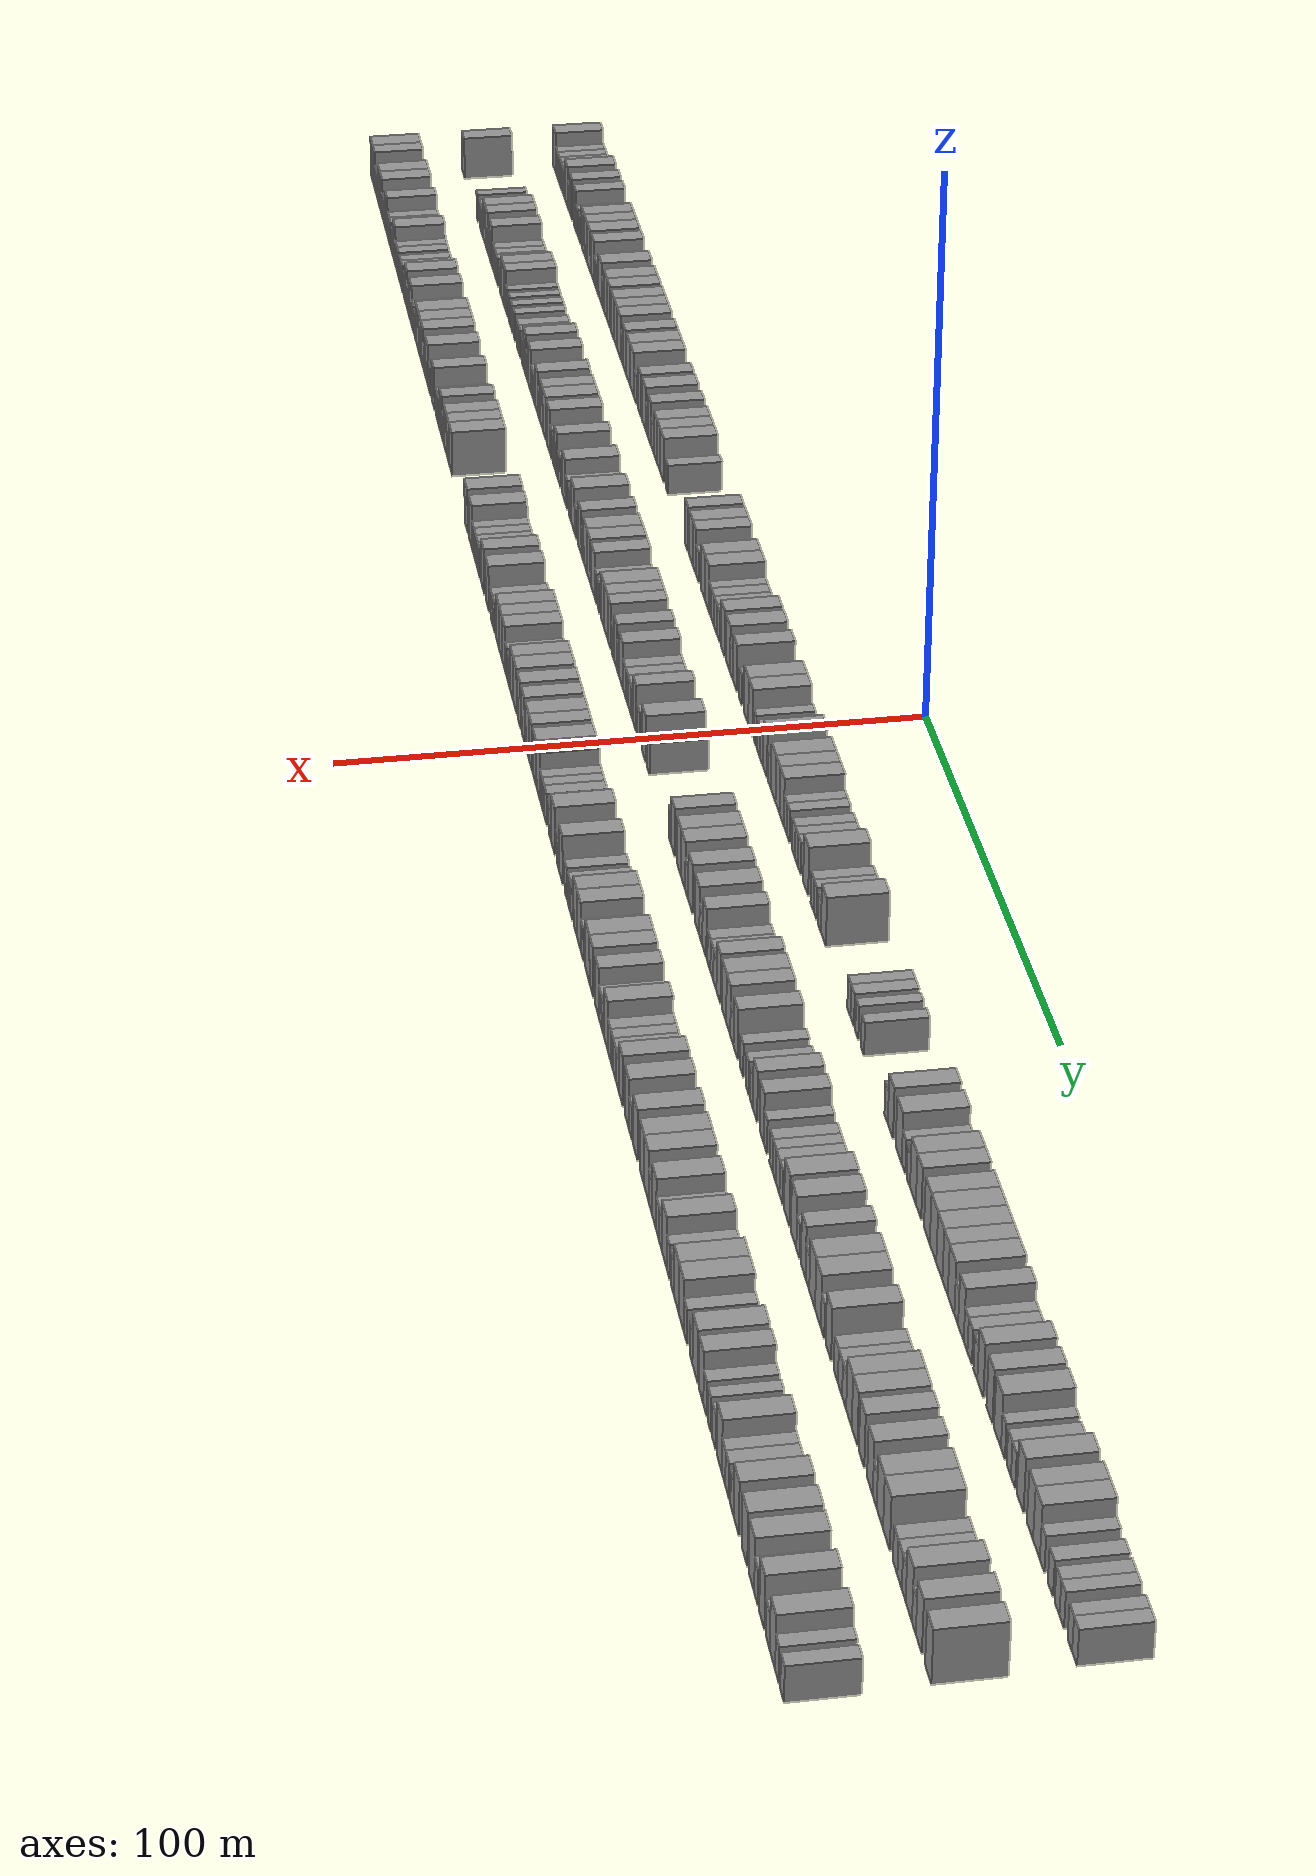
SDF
<sdf version="1.6">
 <world name="default">
  <scene>
   <sky><clouds><speed>12</speed></clouds></sky>
   <ambient>0.4 0.4 0.4 1</ambient>
   <background>0.7 0.7 0.7 1</background>
   <shadows>1</shadows>
  </scene>
  <gravity>0 0 -9.8066</gravity>
  <magnetic_field>6e-06 2.3e-05 -4.2e-05</magnetic_field>
  <physics default="0" name="default_physics" type="ode">
   <ode>
    <solver>
     <type>quick</type>
     <iters>10</iters>
     <sor>1.0</sor>
     <use_dynamic_moi_rescaling>0</use_dynamic_moi_rescaling>
    </solver>
    <constraints>
     <cfm>0</cfm>
     <erp>0.2</erp>
     <contact_max_correcting_vel>100</contact_max_correcting_vel>
     <contact_surface_layer>0.001</contact_surface_layer>
    </constraints>
   </ode>
   <max_step_size>0.004</max_step_size>
   <real_time_factor>1</real_time_factor>
   <real_time_update_rate>250</real_time_update_rate>
  </physics>
  <light name="sun" type="directional">
   <pose>0 0 10 0 0 0</pose>
   <diffuse>0.8 0.8 0.8 1</diffuse>
   <specular>0.2 0.2 0.2 1</specular>
   <attenuation>
    <range>1000</range>
    <constant>0.9</constant>
    <linear>0.01</linear>
    <quadratic>0.001</quadratic>
   </attenuation>
   <direction>-0.5 0.1 -0.9</direction>
  </light>
  <model name="building_1">
   <static>1</static>
   <pose>25.0000 -233.9271 0 0.000000 0.000000 0.000000</pose>
   <link name="link">
    <pose>0 0 4.50 0 0 0</pose>
    <collision name="collision"><geometry><box><size>10.0000 4.1458 9.0000</size></box></geometry></collision>
    <visual name="visual">
     <cast_shadows>0</cast_shadows>
     <geometry><box><size>10.0000 4.1458 9.0000</size></box></geometry>
     <material>
      <script>
       <uri>model://grey_wall/materials/scripts</uri>
       <uri>model://grey_wall/materials/textures</uri>
       <name>vrc/grey_wall</name>
      </script>
     </material>
    </visual>
   </link>
  </model>
  <model name="building_2">
   <static>1</static>
   <pose>25.0000 -230.4867 0 0.000000 0.000000 0.000000</pose>
   <link name="link">
    <pose>0 0 3.00 0 0 0</pose>
    <collision name="collision"><geometry><box><size>10.0000 2.7349 6.0000</size></box></geometry></collision>
    <visual name="visual">
     <cast_shadows>0</cast_shadows>
     <geometry><box><size>10.0000 2.7349 6.0000</size></box></geometry>
     <material>
      <script>
       <uri>model://grey_wall/materials/scripts</uri>
       <uri>model://grey_wall/materials/textures</uri>
       <name>vrc/grey_wall</name>
      </script>
     </material>
    </visual>
   </link>
  </model>
  <model name="building_3">
   <static>1</static>
   <pose>25.0000 -227.7902 0 0.000000 0.000000 0.000000</pose>
   <link name="link">
    <pose>0 0 3.00 0 0 0</pose>
    <collision name="collision"><geometry><box><size>10.0000 2.6582 6.0000</size></box></geometry></collision>
    <visual name="visual">
     <cast_shadows>0</cast_shadows>
     <geometry><box><size>10.0000 2.6582 6.0000</size></box></geometry>
     <material>
      <script>
       <uri>model://grey_wall/materials/scripts</uri>
       <uri>model://grey_wall/materials/textures</uri>
       <name>vrc/grey_wall</name>
      </script>
     </material>
    </visual>
   </link>
  </model>
  <model name="building_4">
   <static>1</static>
   <pose>25.0000 -225.1903 0 0.000000 0.000000 0.000000</pose>
   <link name="link">
    <pose>0 0 3.00 0 0 0</pose>
    <collision name="collision"><geometry><box><size>10.0000 2.5416 6.0000</size></box></geometry></collision>
    <visual name="visual">
     <cast_shadows>0</cast_shadows>
     <geometry><box><size>10.0000 2.5416 6.0000</size></box></geometry>
     <material>
      <script>
       <uri>model://grey_wall/materials/scripts</uri>
       <uri>model://grey_wall/materials/textures</uri>
       <name>vrc/grey_wall</name>
      </script>
     </material>
    </visual>
   </link>
  </model>
  <model name="building_5">
   <static>1</static>
   <pose>25.0000 -222.5512 0 0.000000 0.000000 0.000000</pose>
   <link name="link">
    <pose>0 0 3.00 0 0 0</pose>
    <collision name="collision"><geometry><box><size>10.0000 2.7365 6.0000</size></box></geometry></collision>
    <visual name="visual">
     <cast_shadows>0</cast_shadows>
     <geometry><box><size>10.0000 2.7365 6.0000</size></box></geometry>
     <material>
      <script>
       <uri>model://grey_wall/materials/scripts</uri>
       <uri>model://grey_wall/materials/textures</uri>
       <name>vrc/grey_wall</name>
      </script>
     </material>
    </visual>
   </link>
  </model>
  <model name="building_6">
   <static>1</static>
   <pose>25.0000 -219.8457 0 0.000000 0.000000 0.000000</pose>
   <link name="link">
    <pose>0 0 3.00 0 0 0</pose>
    <collision name="collision"><geometry><box><size>10.0000 2.6745 6.0000</size></box></geometry></collision>
    <visual name="visual">
     <cast_shadows>0</cast_shadows>
     <geometry><box><size>10.0000 2.6745 6.0000</size></box></geometry>
     <material>
      <script>
       <uri>model://grey_wall/materials/scripts</uri>
       <uri>model://grey_wall/materials/textures</uri>
       <name>vrc/grey_wall</name>
      </script>
     </material>
    </visual>
   </link>
  </model>
  <model name="building_7">
   <static>1</static>
   <pose>25.0000 -216.4203 0 0.000000 0.000000 0.000000</pose>
   <link name="link">
    <pose>0 0 4.50 0 0 0</pose>
    <collision name="collision"><geometry><box><size>10.0000 4.1763 9.0000</size></box></geometry></collision>
    <visual name="visual">
     <cast_shadows>0</cast_shadows>
     <geometry><box><size>10.0000 4.1763 9.0000</size></box></geometry>
     <material>
      <script>
       <uri>model://grey_wall/materials/scripts</uri>
       <uri>model://grey_wall/materials/textures</uri>
       <name>vrc/grey_wall</name>
      </script>
     </material>
    </visual>
   </link>
  </model>
  <model name="building_8">
   <static>1</static>
   <pose>25.0000 -213.0158 0 0.000000 0.000000 0.000000</pose>
   <link name="link">
    <pose>0 0 3.00 0 0 0</pose>
    <collision name="collision"><geometry><box><size>10.0000 2.6328 6.0000</size></box></geometry></collision>
    <visual name="visual">
     <cast_shadows>0</cast_shadows>
     <geometry><box><size>10.0000 2.6328 6.0000</size></box></geometry>
     <material>
      <script>
       <uri>model://grey_wall/materials/scripts</uri>
       <uri>model://grey_wall/materials/textures</uri>
       <name>vrc/grey_wall</name>
      </script>
     </material>
    </visual>
   </link>
  </model>
  <model name="building_9">
   <static>1</static>
   <pose>25.0000 -209.8231 0 0.000000 0.000000 0.000000</pose>
   <link name="link">
    <pose>0 0 4.50 0 0 0</pose>
    <collision name="collision"><geometry><box><size>10.0000 3.7524 9.0000</size></box></geometry></collision>
    <visual name="visual">
     <cast_shadows>0</cast_shadows>
     <geometry><box><size>10.0000 3.7524 9.0000</size></box></geometry>
     <material>
      <script>
       <uri>model://grey_wall/materials/scripts</uri>
       <uri>model://grey_wall/materials/textures</uri>
       <name>vrc/grey_wall</name>
      </script>
     </material>
    </visual>
   </link>
  </model>
  <model name="building_10">
   <static>1</static>
   <pose>25.0000 -204.0901 0 0.000000 0.000000 0.000000</pose>
   <link name="link">
    <pose>0 0 4.50 0 0 0</pose>
    <collision name="collision"><geometry><box><size>10.0000 3.7137 9.0000</size></box></geometry></collision>
    <visual name="visual">
     <cast_shadows>0</cast_shadows>
     <geometry><box><size>10.0000 3.7137 9.0000</size></box></geometry>
     <material>
      <script>
       <uri>model://grey_wall/materials/scripts</uri>
       <uri>model://grey_wall/materials/textures</uri>
       <name>vrc/grey_wall</name>
      </script>
     </material>
    </visual>
   </link>
  </model>
  <model name="building_11">
   <static>1</static>
   <pose>25.0000 -200.9545 0 0.000000 0.000000 0.000000</pose>
   <link name="link">
    <pose>0 0 3.00 0 0 0</pose>
    <collision name="collision"><geometry><box><size>10.0000 2.5574 6.0000</size></box></geometry></collision>
    <visual name="visual">
     <cast_shadows>0</cast_shadows>
     <geometry><box><size>10.0000 2.5574 6.0000</size></box></geometry>
     <material>
      <script>
       <uri>model://grey_wall/materials/scripts</uri>
       <uri>model://grey_wall/materials/textures</uri>
       <name>vrc/grey_wall</name>
      </script>
     </material>
    </visual>
   </link>
  </model>
  <model name="building_12">
   <static>1</static>
   <pose>25.0000 -197.3537 0 0.000000 0.000000 0.000000</pose>
   <link name="link">
    <pose>0 0 3.00 0 0 0</pose>
    <collision name="collision"><geometry><box><size>10.0000 2.6442 6.0000</size></box></geometry></collision>
    <visual name="visual">
     <cast_shadows>0</cast_shadows>
     <geometry><box><size>10.0000 2.6442 6.0000</size></box></geometry>
     <material>
      <script>
       <uri>model://grey_wall/materials/scripts</uri>
       <uri>model://grey_wall/materials/textures</uri>
       <name>vrc/grey_wall</name>
      </script>
     </material>
    </visual>
   </link>
  </model>
  <model name="building_13">
   <static>1</static>
   <pose>25.0000 -193.0420 0 0.000000 0.000000 0.000000</pose>
   <link name="link">
    <pose>0 0 4.50 0 0 0</pose>
    <collision name="collision"><geometry><box><size>10.0000 3.9793 9.0000</size></box></geometry></collision>
    <visual name="visual">
     <cast_shadows>0</cast_shadows>
     <geometry><box><size>10.0000 3.9793 9.0000</size></box></geometry>
     <material>
      <script>
       <uri>model://grey_wall/materials/scripts</uri>
       <uri>model://grey_wall/materials/textures</uri>
       <name>vrc/grey_wall</name>
      </script>
     </material>
    </visual>
   </link>
  </model>
  <model name="building_14">
   <static>1</static>
   <pose>25.0000 -189.1228 0 0.000000 0.000000 0.000000</pose>
   <link name="link">
    <pose>0 0 4.50 0 0 0</pose>
    <collision name="collision"><geometry><box><size>10.0000 3.8592 9.0000</size></box></geometry></collision>
    <visual name="visual">
     <cast_shadows>0</cast_shadows>
     <geometry><box><size>10.0000 3.8592 9.0000</size></box></geometry>
     <material>
      <script>
       <uri>model://grey_wall/materials/scripts</uri>
       <uri>model://grey_wall/materials/textures</uri>
       <name>vrc/grey_wall</name>
      </script>
     </material>
    </visual>
   </link>
  </model>
  <model name="building_15">
   <static>1</static>
   <pose>25.0000 -185.0093 0 0.000000 0.000000 0.000000</pose>
   <link name="link">
    <pose>0 0 4.50 0 0 0</pose>
    <collision name="collision"><geometry><box><size>10.0000 4.3678 9.0000</size></box></geometry></collision>
    <visual name="visual">
     <cast_shadows>0</cast_shadows>
     <geometry><box><size>10.0000 4.3678 9.0000</size></box></geometry>
     <material>
      <script>
       <uri>model://grey_wall/materials/scripts</uri>
       <uri>model://grey_wall/materials/textures</uri>
       <name>vrc/grey_wall</name>
      </script>
     </material>
    </visual>
   </link>
  </model>
  <model name="building_16">
   <static>1</static>
   <pose>25.0000 -179.7618 0 0.000000 0.000000 0.000000</pose>
   <link name="link">
    <pose>0 0 4.50 0 0 0</pose>
    <collision name="collision"><geometry><box><size>10.0000 4.1271 9.0000</size></box></geometry></collision>
    <visual name="visual">
     <cast_shadows>0</cast_shadows>
     <geometry><box><size>10.0000 4.1271 9.0000</size></box></geometry>
     <material>
      <script>
       <uri>model://grey_wall/materials/scripts</uri>
       <uri>model://grey_wall/materials/textures</uri>
       <name>vrc/grey_wall</name>
      </script>
     </material>
    </visual>
   </link>
  </model>
  <model name="building_17">
   <static>1</static>
   <pose>25.0000 -176.2631 0 0.000000 0.000000 0.000000</pose>
   <link name="link">
    <pose>0 0 3.00 0 0 0</pose>
    <collision name="collision"><geometry><box><size>10.0000 2.8704 6.0000</size></box></geometry></collision>
    <visual name="visual">
     <cast_shadows>0</cast_shadows>
     <geometry><box><size>10.0000 2.8704 6.0000</size></box></geometry>
     <material>
      <script>
       <uri>model://grey_wall/materials/scripts</uri>
       <uri>model://grey_wall/materials/textures</uri>
       <name>vrc/grey_wall</name>
      </script>
     </material>
    </visual>
   </link>
  </model>
  <model name="building_18">
   <static>1</static>
   <pose>25.0000 -173.5011 0 0.000000 0.000000 0.000000</pose>
   <link name="link">
    <pose>0 0 3.00 0 0 0</pose>
    <collision name="collision"><geometry><box><size>10.0000 2.6536 6.0000</size></box></geometry></collision>
    <visual name="visual">
     <cast_shadows>0</cast_shadows>
     <geometry><box><size>10.0000 2.6536 6.0000</size></box></geometry>
     <material>
      <script>
       <uri>model://grey_wall/materials/scripts</uri>
       <uri>model://grey_wall/materials/textures</uri>
       <name>vrc/grey_wall</name>
      </script>
     </material>
    </visual>
   </link>
  </model>
  <model name="building_19">
   <static>1</static>
   <pose>25.0000 -169.9264 0 0.000000 0.000000 0.000000</pose>
   <link name="link">
    <pose>0 0 4.50 0 0 0</pose>
    <collision name="collision"><geometry><box><size>10.0000 4.4958 9.0000</size></box></geometry></collision>
    <visual name="visual">
     <cast_shadows>0</cast_shadows>
     <geometry><box><size>10.0000 4.4958 9.0000</size></box></geometry>
     <material>
      <script>
       <uri>model://grey_wall/materials/scripts</uri>
       <uri>model://grey_wall/materials/textures</uri>
       <name>vrc/grey_wall</name>
      </script>
     </material>
    </visual>
   </link>
  </model>
  <model name="building_20">
   <static>1</static>
   <pose>25.0000 -166.4420 0 0.000000 0.000000 0.000000</pose>
   <link name="link">
    <pose>0 0 3.00 0 0 0</pose>
    <collision name="collision"><geometry><box><size>10.0000 2.4730 6.0000</size></box></geometry></collision>
    <visual name="visual">
     <cast_shadows>0</cast_shadows>
     <geometry><box><size>10.0000 2.4730 6.0000</size></box></geometry>
     <material>
      <script>
       <uri>model://grey_wall/materials/scripts</uri>
       <uri>model://grey_wall/materials/textures</uri>
       <name>vrc/grey_wall</name>
      </script>
     </material>
    </visual>
   </link>
  </model>
  <model name="building_21">
   <static>1</static>
   <pose>25.0000 -163.0286 0 0.000000 0.000000 0.000000</pose>
   <link name="link">
    <pose>0 0 4.50 0 0 0</pose>
    <collision name="collision"><geometry><box><size>10.0000 4.3538 9.0000</size></box></geometry></collision>
    <visual name="visual">
     <cast_shadows>0</cast_shadows>
     <geometry><box><size>10.0000 4.3538 9.0000</size></box></geometry>
     <material>
      <script>
       <uri>model://grey_wall/materials/scripts</uri>
       <uri>model://grey_wall/materials/textures</uri>
       <name>vrc/grey_wall</name>
      </script>
     </material>
    </visual>
   </link>
  </model>
  <model name="building_22">
   <static>1</static>
   <pose>25.0000 -158.7846 0 0.000000 0.000000 0.000000</pose>
   <link name="link">
    <pose>0 0 4.50 0 0 0</pose>
    <collision name="collision"><geometry><box><size>10.0000 4.1341 9.0000</size></box></geometry></collision>
    <visual name="visual">
     <cast_shadows>0</cast_shadows>
     <geometry><box><size>10.0000 4.1341 9.0000</size></box></geometry>
     <material>
      <script>
       <uri>model://grey_wall/materials/scripts</uri>
       <uri>model://grey_wall/materials/textures</uri>
       <name>vrc/grey_wall</name>
      </script>
     </material>
    </visual>
   </link>
  </model>
  <model name="building_23">
   <static>1</static>
   <pose>25.0000 -153.6770 0 0.000000 0.000000 0.000000</pose>
   <link name="link">
    <pose>0 0 4.50 0 0 0</pose>
    <collision name="collision"><geometry><box><size>10.0000 4.0810 9.0000</size></box></geometry></collision>
    <visual name="visual">
     <cast_shadows>0</cast_shadows>
     <geometry><box><size>10.0000 4.0810 9.0000</size></box></geometry>
     <material>
      <script>
       <uri>model://grey_wall/materials/scripts</uri>
       <uri>model://grey_wall/materials/textures</uri>
       <name>vrc/grey_wall</name>
      </script>
     </material>
    </visual>
   </link>
  </model>
  <model name="building_24">
   <static>1</static>
   <pose>25.0000 -149.7337 0 0.000000 0.000000 0.000000</pose>
   <link name="link">
    <pose>0 0 4.50 0 0 0</pose>
    <collision name="collision"><geometry><box><size>10.0000 3.8056 9.0000</size></box></geometry></collision>
    <visual name="visual">
     <cast_shadows>0</cast_shadows>
     <geometry><box><size>10.0000 3.8056 9.0000</size></box></geometry>
     <material>
      <script>
       <uri>model://grey_wall/materials/scripts</uri>
       <uri>model://grey_wall/materials/textures</uri>
       <name>vrc/grey_wall</name>
      </script>
     </material>
    </visual>
   </link>
  </model>
  <model name="building_25">
   <static>1</static>
   <pose>25.0000 -145.6958 0 0.000000 0.000000 0.000000</pose>
   <link name="link">
    <pose>0 0 4.50 0 0 0</pose>
    <collision name="collision"><geometry><box><size>10.0000 4.2704 9.0000</size></box></geometry></collision>
    <visual name="visual">
     <cast_shadows>0</cast_shadows>
     <geometry><box><size>10.0000 4.2704 9.0000</size></box></geometry>
     <material>
      <script>
       <uri>model://grey_wall/materials/scripts</uri>
       <uri>model://grey_wall/materials/textures</uri>
       <name>vrc/grey_wall</name>
      </script>
     </material>
    </visual>
   </link>
  </model>
  <model name="building_26">
   <static>1</static>
   <pose>25.0000 -142.3037 0 0.000000 0.000000 0.000000</pose>
   <link name="link">
    <pose>0 0 3.00 0 0 0</pose>
    <collision name="collision"><geometry><box><size>10.0000 2.5137 6.0000</size></box></geometry></collision>
    <visual name="visual">
     <cast_shadows>0</cast_shadows>
     <geometry><box><size>10.0000 2.5137 6.0000</size></box></geometry>
     <material>
      <script>
       <uri>model://grey_wall/materials/scripts</uri>
       <uri>model://grey_wall/materials/textures</uri>
       <name>vrc/grey_wall</name>
      </script>
     </material>
    </visual>
   </link>
  </model>
  <model name="building_27">
   <static>1</static>
   <pose>25.0000 -139.0851 0 0.000000 0.000000 0.000000</pose>
   <link name="link">
    <pose>0 0 4.50 0 0 0</pose>
    <collision name="collision"><geometry><box><size>10.0000 3.9237 9.0000</size></box></geometry></collision>
    <visual name="visual">
     <cast_shadows>0</cast_shadows>
     <geometry><box><size>10.0000 3.9237 9.0000</size></box></geometry>
     <material>
      <script>
       <uri>model://grey_wall/materials/scripts</uri>
       <uri>model://grey_wall/materials/textures</uri>
       <name>vrc/grey_wall</name>
      </script>
     </material>
    </visual>
   </link>
  </model>
  <model name="building_28">
   <static>1</static>
   <pose>25.0000 -133.9428 0 0.000000 0.000000 0.000000</pose>
   <link name="link">
    <pose>0 0 4.50 0 0 0</pose>
    <collision name="collision"><geometry><box><size>10.0000 4.3609 9.0000</size></box></geometry></collision>
    <visual name="visual">
     <cast_shadows>0</cast_shadows>
     <geometry><box><size>10.0000 4.3609 9.0000</size></box></geometry>
     <material>
      <script>
       <uri>model://grey_wall/materials/scripts</uri>
       <uri>model://grey_wall/materials/textures</uri>
       <name>vrc/grey_wall</name>
      </script>
     </material>
    </visual>
   </link>
  </model>
  <model name="building_29">
   <static>1</static>
   <pose>25.0000 -129.5690 0 0.000000 0.000000 0.000000</pose>
   <link name="link">
    <pose>0 0 4.50 0 0 0</pose>
    <collision name="collision"><geometry><box><size>10.0000 4.3865 9.0000</size></box></geometry></collision>
    <visual name="visual">
     <cast_shadows>0</cast_shadows>
     <geometry><box><size>10.0000 4.3865 9.0000</size></box></geometry>
     <material>
      <script>
       <uri>model://grey_wall/materials/scripts</uri>
       <uri>model://grey_wall/materials/textures</uri>
       <name>vrc/grey_wall</name>
      </script>
     </material>
    </visual>
   </link>
  </model>
  <model name="building_30">
   <static>1</static>
   <pose>25.0000 -125.0224 0 0.000000 0.000000 0.000000</pose>
   <link name="link">
    <pose>0 0 3.00 0 0 0</pose>
    <collision name="collision"><geometry><box><size>10.0000 2.7068 6.0000</size></box></geometry></collision>
    <visual name="visual">
     <cast_shadows>0</cast_shadows>
     <geometry><box><size>10.0000 2.7068 6.0000</size></box></geometry>
     <material>
      <script>
       <uri>model://grey_wall/materials/scripts</uri>
       <uri>model://grey_wall/materials/textures</uri>
       <name>vrc/grey_wall</name>
      </script>
     </material>
    </visual>
   </link>
  </model>
  <model name="building_31">
   <static>1</static>
   <pose>25.0000 -119.7780 0 0.000000 0.000000 0.000000</pose>
   <link name="link">
    <pose>0 0 4.50 0 0 0</pose>
    <collision name="collision"><geometry><box><size>10.0000 3.7821 9.0000</size></box></geometry></collision>
    <visual name="visual">
     <cast_shadows>0</cast_shadows>
     <geometry><box><size>10.0000 3.7821 9.0000</size></box></geometry>
     <material>
      <script>
       <uri>model://grey_wall/materials/scripts</uri>
       <uri>model://grey_wall/materials/textures</uri>
       <name>vrc/grey_wall</name>
      </script>
     </material>
    </visual>
   </link>
  </model>
  <model name="building_32">
   <static>1</static>
   <pose>25.0000 -114.6469 0 0.000000 0.000000 0.000000</pose>
   <link name="link">
    <pose>0 0 4.50 0 0 0</pose>
    <collision name="collision"><geometry><box><size>10.0000 4.4802 9.0000</size></box></geometry></collision>
    <visual name="visual">
     <cast_shadows>0</cast_shadows>
     <geometry><box><size>10.0000 4.4802 9.0000</size></box></geometry>
     <material>
      <script>
       <uri>model://grey_wall/materials/scripts</uri>
       <uri>model://grey_wall/materials/textures</uri>
       <name>vrc/grey_wall</name>
      </script>
     </material>
    </visual>
   </link>
  </model>
  <model name="building_33">
   <static>1</static>
   <pose>25.0000 -111.1331 0 0.000000 0.000000 0.000000</pose>
   <link name="link">
    <pose>0 0 3.00 0 0 0</pose>
    <collision name="collision"><geometry><box><size>10.0000 2.5472 6.0000</size></box></geometry></collision>
    <visual name="visual">
     <cast_shadows>0</cast_shadows>
     <geometry><box><size>10.0000 2.5472 6.0000</size></box></geometry>
     <material>
      <script>
       <uri>model://grey_wall/materials/scripts</uri>
       <uri>model://grey_wall/materials/textures</uri>
       <name>vrc/grey_wall</name>
      </script>
     </material>
    </visual>
   </link>
  </model>
  <model name="building_34">
   <static>1</static>
   <pose>25.0000 -107.9677 0 0.000000 0.000000 0.000000</pose>
   <link name="link">
    <pose>0 0 4.50 0 0 0</pose>
    <collision name="collision"><geometry><box><size>10.0000 3.7837 9.0000</size></box></geometry></collision>
    <visual name="visual">
     <cast_shadows>0</cast_shadows>
     <geometry><box><size>10.0000 3.7837 9.0000</size></box></geometry>
     <material>
      <script>
       <uri>model://grey_wall/materials/scripts</uri>
       <uri>model://grey_wall/materials/textures</uri>
       <name>vrc/grey_wall</name>
      </script>
     </material>
    </visual>
   </link>
  </model>
  <model name="building_35">
   <static>1</static>
   <pose>25.0000 -104.6621 0 0.000000 0.000000 0.000000</pose>
   <link name="link">
    <pose>0 0 3.00 0 0 0</pose>
    <collision name="collision"><geometry><box><size>10.0000 2.8275 6.0000</size></box></geometry></collision>
    <visual name="visual">
     <cast_shadows>0</cast_shadows>
     <geometry><box><size>10.0000 2.8275 6.0000</size></box></geometry>
     <material>
      <script>
       <uri>model://grey_wall/materials/scripts</uri>
       <uri>model://grey_wall/materials/textures</uri>
       <name>vrc/grey_wall</name>
      </script>
     </material>
    </visual>
   </link>
  </model>
  <model name="building_36">
   <static>1</static>
   <pose>25.0000 -101.2860 0 0.000000 0.000000 0.000000</pose>
   <link name="link">
    <pose>0 0 4.50 0 0 0</pose>
    <collision name="collision"><geometry><box><size>10.0000 3.9246 9.0000</size></box></geometry></collision>
    <visual name="visual">
     <cast_shadows>0</cast_shadows>
     <geometry><box><size>10.0000 3.9246 9.0000</size></box></geometry>
     <material>
      <script>
       <uri>model://grey_wall/materials/scripts</uri>
       <uri>model://grey_wall/materials/textures</uri>
       <name>vrc/grey_wall</name>
      </script>
     </material>
    </visual>
   </link>
  </model>
  <model name="building_37">
   <static>1</static>
   <pose>25.0000 -97.4187 0 0.000000 0.000000 0.000000</pose>
   <link name="link">
    <pose>0 0 4.50 0 0 0</pose>
    <collision name="collision"><geometry><box><size>10.0000 3.8100 9.0000</size></box></geometry></collision>
    <visual name="visual">
     <cast_shadows>0</cast_shadows>
     <geometry><box><size>10.0000 3.8100 9.0000</size></box></geometry>
     <material>
      <script>
       <uri>model://grey_wall/materials/scripts</uri>
       <uri>model://grey_wall/materials/textures</uri>
       <name>vrc/grey_wall</name>
      </script>
     </material>
    </visual>
   </link>
  </model>
  <model name="building_38">
   <static>1</static>
   <pose>25.0000 -93.4403 0 0.000000 0.000000 0.000000</pose>
   <link name="link">
    <pose>0 0 4.50 0 0 0</pose>
    <collision name="collision"><geometry><box><size>10.0000 4.1469 9.0000</size></box></geometry></collision>
    <visual name="visual">
     <cast_shadows>0</cast_shadows>
     <geometry><box><size>10.0000 4.1469 9.0000</size></box></geometry>
     <material>
      <script>
       <uri>model://grey_wall/materials/scripts</uri>
       <uri>model://grey_wall/materials/textures</uri>
       <name>vrc/grey_wall</name>
      </script>
     </material>
    </visual>
   </link>
  </model>
  <model name="building_39">
   <static>1</static>
   <pose>25.0000 -87.8772 0 0.000000 0.000000 0.000000</pose>
   <link name="link">
    <pose>0 0 3.00 0 0 0</pose>
    <collision name="collision"><geometry><box><size>10.0000 2.9793 6.0000</size></box></geometry></collision>
    <visual name="visual">
     <cast_shadows>0</cast_shadows>
     <geometry><box><size>10.0000 2.9793 6.0000</size></box></geometry>
     <material>
      <script>
       <uri>model://grey_wall/materials/scripts</uri>
       <uri>model://grey_wall/materials/textures</uri>
       <name>vrc/grey_wall</name>
      </script>
     </material>
    </visual>
   </link>
  </model>
  <model name="building_40">
   <static>1</static>
   <pose>25.0000 -65.9279 0 0.000000 0.000000 0.000000</pose>
   <link name="link">
    <pose>0 0 4.50 0 0 0</pose>
    <collision name="collision"><geometry><box><size>10.0000 3.6397 9.0000</size></box></geometry></collision>
    <visual name="visual">
     <cast_shadows>0</cast_shadows>
     <geometry><box><size>10.0000 3.6397 9.0000</size></box></geometry>
     <material>
      <script>
       <uri>model://grey_wall/materials/scripts</uri>
       <uri>model://grey_wall/materials/textures</uri>
       <name>vrc/grey_wall</name>
      </script>
     </material>
    </visual>
   </link>
  </model>
  <model name="building_41">
   <static>1</static>
   <pose>25.0000 -61.1489 0 0.000000 0.000000 0.000000</pose>
   <link name="link">
    <pose>0 0 4.50 0 0 0</pose>
    <collision name="collision"><geometry><box><size>10.0000 3.9184 9.0000</size></box></geometry></collision>
    <visual name="visual">
     <cast_shadows>0</cast_shadows>
     <geometry><box><size>10.0000 3.9184 9.0000</size></box></geometry>
     <material>
      <script>
       <uri>model://grey_wall/materials/scripts</uri>
       <uri>model://grey_wall/materials/textures</uri>
       <name>vrc/grey_wall</name>
      </script>
     </material>
    </visual>
   </link>
  </model>
  <model name="building_42">
   <static>1</static>
   <pose>25.0000 -57.3230 0 0.000000 0.000000 0.000000</pose>
   <link name="link">
    <pose>0 0 4.50 0 0 0</pose>
    <collision name="collision"><geometry><box><size>10.0000 3.7334 9.0000</size></box></geometry></collision>
    <visual name="visual">
     <cast_shadows>0</cast_shadows>
     <geometry><box><size>10.0000 3.7334 9.0000</size></box></geometry>
     <material>
      <script>
       <uri>model://grey_wall/materials/scripts</uri>
       <uri>model://grey_wall/materials/textures</uri>
       <name>vrc/grey_wall</name>
      </script>
     </material>
    </visual>
   </link>
  </model>
  <model name="building_43">
   <static>1</static>
   <pose>25.0000 -54.0455 0 0.000000 0.000000 0.000000</pose>
   <link name="link">
    <pose>0 0 3.00 0 0 0</pose>
    <collision name="collision"><geometry><box><size>10.0000 2.8216 6.0000</size></box></geometry></collision>
    <visual name="visual">
     <cast_shadows>0</cast_shadows>
     <geometry><box><size>10.0000 2.8216 6.0000</size></box></geometry>
     <material>
      <script>
       <uri>model://grey_wall/materials/scripts</uri>
       <uri>model://grey_wall/materials/textures</uri>
       <name>vrc/grey_wall</name>
      </script>
     </material>
    </visual>
   </link>
  </model>
  <model name="building_44">
   <static>1</static>
   <pose>25.0000 -48.5789 0 0.000000 0.000000 0.000000</pose>
   <link name="link">
    <pose>0 0 4.50 0 0 0</pose>
    <collision name="collision"><geometry><box><size>10.0000 4.1117 9.0000</size></box></geometry></collision>
    <visual name="visual">
     <cast_shadows>0</cast_shadows>
     <geometry><box><size>10.0000 4.1117 9.0000</size></box></geometry>
     <material>
      <script>
       <uri>model://grey_wall/materials/scripts</uri>
       <uri>model://grey_wall/materials/textures</uri>
       <name>vrc/grey_wall</name>
      </script>
     </material>
    </visual>
   </link>
  </model>
  <model name="building_45">
   <static>1</static>
   <pose>25.0000 -44.3224 0 0.000000 0.000000 0.000000</pose>
   <link name="link">
    <pose>0 0 4.50 0 0 0</pose>
    <collision name="collision"><geometry><box><size>10.0000 4.4012 9.0000</size></box></geometry></collision>
    <visual name="visual">
     <cast_shadows>0</cast_shadows>
     <geometry><box><size>10.0000 4.4012 9.0000</size></box></geometry>
     <material>
      <script>
       <uri>model://grey_wall/materials/scripts</uri>
       <uri>model://grey_wall/materials/textures</uri>
       <name>vrc/grey_wall</name>
      </script>
     </material>
    </visual>
   </link>
  </model>
  <model name="building_46">
   <static>1</static>
   <pose>25.0000 -40.8660 0 0.000000 0.000000 0.000000</pose>
   <link name="link">
    <pose>0 0 3.00 0 0 0</pose>
    <collision name="collision"><geometry><box><size>10.0000 2.5116 6.0000</size></box></geometry></collision>
    <visual name="visual">
     <cast_shadows>0</cast_shadows>
     <geometry><box><size>10.0000 2.5116 6.0000</size></box></geometry>
     <material>
      <script>
       <uri>model://grey_wall/materials/scripts</uri>
       <uri>model://grey_wall/materials/textures</uri>
       <name>vrc/grey_wall</name>
      </script>
     </material>
    </visual>
   </link>
  </model>
  <model name="building_47">
   <static>1</static>
   <pose>25.0000 -38.1492 0 0.000000 0.000000 0.000000</pose>
   <link name="link">
    <pose>0 0 3.00 0 0 0</pose>
    <collision name="collision"><geometry><box><size>10.0000 2.9220 6.0000</size></box></geometry></collision>
    <visual name="visual">
     <cast_shadows>0</cast_shadows>
     <geometry><box><size>10.0000 2.9220 6.0000</size></box></geometry>
     <material>
      <script>
       <uri>model://grey_wall/materials/scripts</uri>
       <uri>model://grey_wall/materials/textures</uri>
       <name>vrc/grey_wall</name>
      </script>
     </material>
    </visual>
   </link>
  </model>
  <model name="building_48">
   <static>1</static>
   <pose>25.0000 -35.2153 0 0.000000 0.000000 0.000000</pose>
   <link name="link">
    <pose>0 0 3.00 0 0 0</pose>
    <collision name="collision"><geometry><box><size>10.0000 2.9459 6.0000</size></box></geometry></collision>
    <visual name="visual">
     <cast_shadows>0</cast_shadows>
     <geometry><box><size>10.0000 2.9459 6.0000</size></box></geometry>
     <material>
      <script>
       <uri>model://grey_wall/materials/scripts</uri>
       <uri>model://grey_wall/materials/textures</uri>
       <name>vrc/grey_wall</name>
      </script>
     </material>
    </visual>
   </link>
  </model>
  <model name="building_49">
   <static>1</static>
   <pose>25.0000 -32.2493 0 0.000000 0.000000 0.000000</pose>
   <link name="link">
    <pose>0 0 3.00 0 0 0</pose>
    <collision name="collision"><geometry><box><size>10.0000 2.9861 6.0000</size></box></geometry></collision>
    <visual name="visual">
     <cast_shadows>0</cast_shadows>
     <geometry><box><size>10.0000 2.9861 6.0000</size></box></geometry>
     <material>
      <script>
       <uri>model://grey_wall/materials/scripts</uri>
       <uri>model://grey_wall/materials/textures</uri>
       <name>vrc/grey_wall</name>
      </script>
     </material>
    </visual>
   </link>
  </model>
  <model name="building_50">
   <static>1</static>
   <pose>25.0000 -27.7480 0 0.000000 0.000000 0.000000</pose>
   <link name="link">
    <pose>0 0 4.50 0 0 0</pose>
    <collision name="collision"><geometry><box><size>10.0000 4.0165 9.0000</size></box></geometry></collision>
    <visual name="visual">
     <cast_shadows>0</cast_shadows>
     <geometry><box><size>10.0000 4.0165 9.0000</size></box></geometry>
     <material>
      <script>
       <uri>model://grey_wall/materials/scripts</uri>
       <uri>model://grey_wall/materials/textures</uri>
       <name>vrc/grey_wall</name>
      </script>
     </material>
    </visual>
   </link>
  </model>
  <model name="building_51">
   <static>1</static>
   <pose>25.0000 -22.5048 0 0.000000 0.000000 0.000000</pose>
   <link name="link">
    <pose>0 0 4.50 0 0 0</pose>
    <collision name="collision"><geometry><box><size>10.0000 4.4698 9.0000</size></box></geometry></collision>
    <visual name="visual">
     <cast_shadows>0</cast_shadows>
     <geometry><box><size>10.0000 4.4698 9.0000</size></box></geometry>
     <material>
      <script>
       <uri>model://grey_wall/materials/scripts</uri>
       <uri>model://grey_wall/materials/textures</uri>
       <name>vrc/grey_wall</name>
      </script>
     </material>
    </visual>
   </link>
  </model>
  <model name="building_52">
   <static>1</static>
   <pose>25.0000 -18.8796 0 0.000000 0.000000 0.000000</pose>
   <link name="link">
    <pose>0 0 3.00 0 0 0</pose>
    <collision name="collision"><geometry><box><size>10.0000 2.7806 6.0000</size></box></geometry></collision>
    <visual name="visual">
     <cast_shadows>0</cast_shadows>
     <geometry><box><size>10.0000 2.7806 6.0000</size></box></geometry>
     <material>
      <script>
       <uri>model://grey_wall/materials/scripts</uri>
       <uri>model://grey_wall/materials/textures</uri>
       <name>vrc/grey_wall</name>
      </script>
     </material>
    </visual>
   </link>
  </model>
  <model name="building_53">
   <static>1</static>
   <pose>25.0000 -15.5178 0 0.000000 0.000000 0.000000</pose>
   <link name="link">
    <pose>0 0 4.50 0 0 0</pose>
    <collision name="collision"><geometry><box><size>10.0000 3.9430 9.0000</size></box></geometry></collision>
    <visual name="visual">
     <cast_shadows>0</cast_shadows>
     <geometry><box><size>10.0000 3.9430 9.0000</size></box></geometry>
     <material>
      <script>
       <uri>model://grey_wall/materials/scripts</uri>
       <uri>model://grey_wall/materials/textures</uri>
       <name>vrc/grey_wall</name>
      </script>
     </material>
    </visual>
   </link>
  </model>
  <model name="building_54">
   <static>1</static>
   <pose>25.0000 -10.1851 0 0.000000 0.000000 0.000000</pose>
   <link name="link">
    <pose>0 0 3.00 0 0 0</pose>
    <collision name="collision"><geometry><box><size>10.0000 2.7223 6.0000</size></box></geometry></collision>
    <visual name="visual">
     <cast_shadows>0</cast_shadows>
     <geometry><box><size>10.0000 2.7223 6.0000</size></box></geometry>
     <material>
      <script>
       <uri>model://grey_wall/materials/scripts</uri>
       <uri>model://grey_wall/materials/textures</uri>
       <name>vrc/grey_wall</name>
      </script>
     </material>
    </visual>
   </link>
  </model>
  <model name="building_55">
   <static>1</static>
   <pose>25.0000 -4.6229 0 0.000000 0.000000 0.000000</pose>
   <link name="link">
    <pose>0 0 4.50 0 0 0</pose>
    <collision name="collision"><geometry><box><size>10.0000 4.4022 9.0000</size></box></geometry></collision>
    <visual name="visual">
     <cast_shadows>0</cast_shadows>
     <geometry><box><size>10.0000 4.4022 9.0000</size></box></geometry>
     <material>
      <script>
       <uri>model://grey_wall/materials/scripts</uri>
       <uri>model://grey_wall/materials/textures</uri>
       <name>vrc/grey_wall</name>
      </script>
     </material>
    </visual>
   </link>
  </model>
  <model name="building_56">
   <static>1</static>
   <pose>25.0000 -0.3468 0 0.000000 0.000000 0.000000</pose>
   <link name="link">
    <pose>0 0 4.50 0 0 0</pose>
    <collision name="collision"><geometry><box><size>10.0000 4.1499 9.0000</size></box></geometry></collision>
    <visual name="visual">
     <cast_shadows>0</cast_shadows>
     <geometry><box><size>10.0000 4.1499 9.0000</size></box></geometry>
     <material>
      <script>
       <uri>model://grey_wall/materials/scripts</uri>
       <uri>model://grey_wall/materials/textures</uri>
       <name>vrc/grey_wall</name>
      </script>
     </material>
    </visual>
   </link>
  </model>
  <model name="building_57">
   <static>1</static>
   <pose>25.0000 3.9664 0 0.000000 0.000000 0.000000</pose>
   <link name="link">
    <pose>0 0 3.00 0 0 0</pose>
    <collision name="collision"><geometry><box><size>10.0000 2.4766 6.0000</size></box></geometry></collision>
    <visual name="visual">
     <cast_shadows>0</cast_shadows>
     <geometry><box><size>10.0000 2.4766 6.0000</size></box></geometry>
     <material>
      <script>
       <uri>model://grey_wall/materials/scripts</uri>
       <uri>model://grey_wall/materials/textures</uri>
       <name>vrc/grey_wall</name>
      </script>
     </material>
    </visual>
   </link>
  </model>
  <model name="building_58">
   <static>1</static>
   <pose>25.0000 7.5182 0 0.000000 0.000000 0.000000</pose>
   <link name="link">
    <pose>0 0 3.00 0 0 0</pose>
    <collision name="collision"><geometry><box><size>10.0000 2.6270 6.0000</size></box></geometry></collision>
    <visual name="visual">
     <cast_shadows>0</cast_shadows>
     <geometry><box><size>10.0000 2.6270 6.0000</size></box></geometry>
     <material>
      <script>
       <uri>model://grey_wall/materials/scripts</uri>
       <uri>model://grey_wall/materials/textures</uri>
       <name>vrc/grey_wall</name>
      </script>
     </material>
    </visual>
   </link>
  </model>
  <model name="building_59">
   <static>1</static>
   <pose>25.0000 10.2033 0 0.000000 0.000000 0.000000</pose>
   <link name="link">
    <pose>0 0 3.00 0 0 0</pose>
    <collision name="collision"><geometry><box><size>10.0000 2.7432 6.0000</size></box></geometry></collision>
    <visual name="visual">
     <cast_shadows>0</cast_shadows>
     <geometry><box><size>10.0000 2.7432 6.0000</size></box></geometry>
     <material>
      <script>
       <uri>model://grey_wall/materials/scripts</uri>
       <uri>model://grey_wall/materials/textures</uri>
       <name>vrc/grey_wall</name>
      </script>
     </material>
    </visual>
   </link>
  </model>
  <model name="building_60">
   <static>1</static>
   <pose>25.0000 13.4718 0 0.000000 0.000000 0.000000</pose>
   <link name="link">
    <pose>0 0 4.50 0 0 0</pose>
    <collision name="collision"><geometry><box><size>10.0000 3.7939 9.0000</size></box></geometry></collision>
    <visual name="visual">
     <cast_shadows>0</cast_shadows>
     <geometry><box><size>10.0000 3.7939 9.0000</size></box></geometry>
     <material>
      <script>
       <uri>model://grey_wall/materials/scripts</uri>
       <uri>model://grey_wall/materials/textures</uri>
       <name>vrc/grey_wall</name>
      </script>
     </material>
    </visual>
   </link>
  </model>
  <model name="building_61">
   <static>1</static>
   <pose>25.0000 17.6209 0 0.000000 0.000000 0.000000</pose>
   <link name="link">
    <pose>0 0 3.00 0 0 0</pose>
    <collision name="collision"><geometry><box><size>10.0000 2.5042 6.0000</size></box></geometry></collision>
    <visual name="visual">
     <cast_shadows>0</cast_shadows>
     <geometry><box><size>10.0000 2.5042 6.0000</size></box></geometry>
     <material>
      <script>
       <uri>model://grey_wall/materials/scripts</uri>
       <uri>model://grey_wall/materials/textures</uri>
       <name>vrc/grey_wall</name>
      </script>
     </material>
    </visual>
   </link>
  </model>
  <model name="building_62">
   <static>1</static>
   <pose>25.0000 21.0425 0 0.000000 0.000000 0.000000</pose>
   <link name="link">
    <pose>0 0 4.50 0 0 0</pose>
    <collision name="collision"><geometry><box><size>10.0000 4.3391 9.0000</size></box></geometry></collision>
    <visual name="visual">
     <cast_shadows>0</cast_shadows>
     <geometry><box><size>10.0000 4.3391 9.0000</size></box></geometry>
     <material>
      <script>
       <uri>model://grey_wall/materials/scripts</uri>
       <uri>model://grey_wall/materials/textures</uri>
       <name>vrc/grey_wall</name>
      </script>
     </material>
    </visual>
   </link>
  </model>
  <model name="building_63">
   <static>1</static>
   <pose>25.0000 25.0427 0 0.000000 0.000000 0.000000</pose>
   <link name="link">
    <pose>0 0 4.50 0 0 0</pose>
    <collision name="collision"><geometry><box><size>10.0000 3.6613 9.0000</size></box></geometry></collision>
    <visual name="visual">
     <cast_shadows>0</cast_shadows>
     <geometry><box><size>10.0000 3.6613 9.0000</size></box></geometry>
     <material>
      <script>
       <uri>model://grey_wall/materials/scripts</uri>
       <uri>model://grey_wall/materials/textures</uri>
       <name>vrc/grey_wall</name>
      </script>
     </material>
    </visual>
   </link>
  </model>
  <model name="building_64">
   <static>1</static>
   <pose>25.0000 28.8501 0 0.000000 0.000000 0.000000</pose>
   <link name="link">
    <pose>0 0 4.50 0 0 0</pose>
    <collision name="collision"><geometry><box><size>10.0000 3.9537 9.0000</size></box></geometry></collision>
    <visual name="visual">
     <cast_shadows>0</cast_shadows>
     <geometry><box><size>10.0000 3.9537 9.0000</size></box></geometry>
     <material>
      <script>
       <uri>model://grey_wall/materials/scripts</uri>
       <uri>model://grey_wall/materials/textures</uri>
       <name>vrc/grey_wall</name>
      </script>
     </material>
    </visual>
   </link>
  </model>
  <model name="building_65">
   <static>1</static>
   <pose>25.0000 32.1144 0 0.000000 0.000000 0.000000</pose>
   <link name="link">
    <pose>0 0 3.00 0 0 0</pose>
    <collision name="collision"><geometry><box><size>10.0000 2.5749 6.0000</size></box></geometry></collision>
    <visual name="visual">
     <cast_shadows>0</cast_shadows>
     <geometry><box><size>10.0000 2.5749 6.0000</size></box></geometry>
     <material>
      <script>
       <uri>model://grey_wall/materials/scripts</uri>
       <uri>model://grey_wall/materials/textures</uri>
       <name>vrc/grey_wall</name>
      </script>
     </material>
    </visual>
   </link>
  </model>
  <model name="building_66">
   <static>1</static>
   <pose>25.0000 34.7134 0 0.000000 0.000000 0.000000</pose>
   <link name="link">
    <pose>0 0 3.00 0 0 0</pose>
    <collision name="collision"><geometry><box><size>10.0000 2.6231 6.0000</size></box></geometry></collision>
    <visual name="visual">
     <cast_shadows>0</cast_shadows>
     <geometry><box><size>10.0000 2.6231 6.0000</size></box></geometry>
     <material>
      <script>
       <uri>model://grey_wall/materials/scripts</uri>
       <uri>model://grey_wall/materials/textures</uri>
       <name>vrc/grey_wall</name>
      </script>
     </material>
    </visual>
   </link>
  </model>
  <model name="building_67">
   <static>1</static>
   <pose>25.0000 39.4012 0 0.000000 0.000000 0.000000</pose>
   <link name="link">
    <pose>0 0 3.00 0 0 0</pose>
    <collision name="collision"><geometry><box><size>10.0000 2.7525 6.0000</size></box></geometry></collision>
    <visual name="visual">
     <cast_shadows>0</cast_shadows>
     <geometry><box><size>10.0000 2.7525 6.0000</size></box></geometry>
     <material>
      <script>
       <uri>model://grey_wall/materials/scripts</uri>
       <uri>model://grey_wall/materials/textures</uri>
       <name>vrc/grey_wall</name>
      </script>
     </material>
    </visual>
   </link>
  </model>
  <model name="building_68">
   <static>1</static>
   <pose>25.0000 42.0086 0 0.000000 0.000000 0.000000</pose>
   <link name="link">
    <pose>0 0 3.00 0 0 0</pose>
    <collision name="collision"><geometry><box><size>10.0000 2.4623 6.0000</size></box></geometry></collision>
    <visual name="visual">
     <cast_shadows>0</cast_shadows>
     <geometry><box><size>10.0000 2.4623 6.0000</size></box></geometry>
     <material>
      <script>
       <uri>model://grey_wall/materials/scripts</uri>
       <uri>model://grey_wall/materials/textures</uri>
       <name>vrc/grey_wall</name>
      </script>
     </material>
    </visual>
   </link>
  </model>
  <model name="building_69">
   <static>1</static>
   <pose>25.0000 44.5900 0 0.000000 0.000000 0.000000</pose>
   <link name="link">
    <pose>0 0 3.00 0 0 0</pose>
    <collision name="collision"><geometry><box><size>10.0000 2.7006 6.0000</size></box></geometry></collision>
    <visual name="visual">
     <cast_shadows>0</cast_shadows>
     <geometry><box><size>10.0000 2.7006 6.0000</size></box></geometry>
     <material>
      <script>
       <uri>model://grey_wall/materials/scripts</uri>
       <uri>model://grey_wall/materials/textures</uri>
       <name>vrc/grey_wall</name>
      </script>
     </material>
    </visual>
   </link>
  </model>
  <model name="building_70">
   <static>1</static>
   <pose>25.0000 50.0988 0 0.000000 0.000000 0.000000</pose>
   <link name="link">
    <pose>0 0 4.50 0 0 0</pose>
    <collision name="collision"><geometry><box><size>10.0000 4.3170 9.0000</size></box></geometry></collision>
    <visual name="visual">
     <cast_shadows>0</cast_shadows>
     <geometry><box><size>10.0000 4.3170 9.0000</size></box></geometry>
     <material>
      <script>
       <uri>model://grey_wall/materials/scripts</uri>
       <uri>model://grey_wall/materials/textures</uri>
       <name>vrc/grey_wall</name>
      </script>
     </material>
    </visual>
   </link>
  </model>
  <model name="building_71">
   <static>1</static>
   <pose>25.0000 55.5835 0 0.000000 0.000000 0.000000</pose>
   <link name="link">
    <pose>0 0 3.00 0 0 0</pose>
    <collision name="collision"><geometry><box><size>10.0000 2.6523 6.0000</size></box></geometry></collision>
    <visual name="visual">
     <cast_shadows>0</cast_shadows>
     <geometry><box><size>10.0000 2.6523 6.0000</size></box></geometry>
     <material>
      <script>
       <uri>model://grey_wall/materials/scripts</uri>
       <uri>model://grey_wall/materials/textures</uri>
       <name>vrc/grey_wall</name>
      </script>
     </material>
    </visual>
   </link>
  </model>
  <model name="building_72">
   <static>1</static>
   <pose>25.0000 58.1845 0 0.000000 0.000000 0.000000</pose>
   <link name="link">
    <pose>0 0 3.00 0 0 0</pose>
    <collision name="collision"><geometry><box><size>10.0000 2.5496 6.0000</size></box></geometry></collision>
    <visual name="visual">
     <cast_shadows>0</cast_shadows>
     <geometry><box><size>10.0000 2.5496 6.0000</size></box></geometry>
     <material>
      <script>
       <uri>model://grey_wall/materials/scripts</uri>
       <uri>model://grey_wall/materials/textures</uri>
       <name>vrc/grey_wall</name>
      </script>
     </material>
    </visual>
   </link>
  </model>
  <model name="building_73">
   <static>1</static>
   <pose>25.0000 61.7652 0 0.000000 0.000000 0.000000</pose>
   <link name="link">
    <pose>0 0 3.00 0 0 0</pose>
    <collision name="collision"><geometry><box><size>10.0000 2.6120 6.0000</size></box></geometry></collision>
    <visual name="visual">
     <cast_shadows>0</cast_shadows>
     <geometry><box><size>10.0000 2.6120 6.0000</size></box></geometry>
     <material>
      <script>
       <uri>model://grey_wall/materials/scripts</uri>
       <uri>model://grey_wall/materials/textures</uri>
       <name>vrc/grey_wall</name>
      </script>
     </material>
    </visual>
   </link>
  </model>
  <model name="building_74">
   <static>1</static>
   <pose>25.0000 65.1840 0 0.000000 0.000000 0.000000</pose>
   <link name="link">
    <pose>0 0 4.50 0 0 0</pose>
    <collision name="collision"><geometry><box><size>10.0000 4.2255 9.0000</size></box></geometry></collision>
    <visual name="visual">
     <cast_shadows>0</cast_shadows>
     <geometry><box><size>10.0000 4.2255 9.0000</size></box></geometry>
     <material>
      <script>
       <uri>model://grey_wall/materials/scripts</uri>
       <uri>model://grey_wall/materials/textures</uri>
       <name>vrc/grey_wall</name>
      </script>
     </material>
    </visual>
   </link>
  </model>
  <model name="building_75">
   <static>1</static>
   <pose>25.0000 86.0218 0 0.000000 0.000000 0.000000</pose>
   <link name="link">
    <pose>0 0 3.00 0 0 0</pose>
    <collision name="collision"><geometry><box><size>10.0000 2.4834 6.0000</size></box></geometry></collision>
    <visual name="visual">
     <cast_shadows>0</cast_shadows>
     <geometry><box><size>10.0000 2.4834 6.0000</size></box></geometry>
     <material>
      <script>
       <uri>model://grey_wall/materials/scripts</uri>
       <uri>model://grey_wall/materials/textures</uri>
       <name>vrc/grey_wall</name>
      </script>
     </material>
    </visual>
   </link>
  </model>
  <model name="building_76">
   <static>1</static>
   <pose>25.0000 88.6927 0 0.000000 0.000000 0.000000</pose>
   <link name="link">
    <pose>0 0 3.00 0 0 0</pose>
    <collision name="collision"><geometry><box><size>10.0000 2.8584 6.0000</size></box></geometry></collision>
    <visual name="visual">
     <cast_shadows>0</cast_shadows>
     <geometry><box><size>10.0000 2.8584 6.0000</size></box></geometry>
     <material>
      <script>
       <uri>model://grey_wall/materials/scripts</uri>
       <uri>model://grey_wall/materials/textures</uri>
       <name>vrc/grey_wall</name>
      </script>
     </material>
    </visual>
   </link>
  </model>
  <model name="building_77">
   <static>1</static>
   <pose>25.0000 92.3241 0 0.000000 0.000000 0.000000</pose>
   <link name="link">
    <pose>0 0 3.00 0 0 0</pose>
    <collision name="collision"><geometry><box><size>10.0000 2.4044 6.0000</size></box></geometry></collision>
    <visual name="visual">
     <cast_shadows>0</cast_shadows>
     <geometry><box><size>10.0000 2.4044 6.0000</size></box></geometry>
     <material>
      <script>
       <uri>model://grey_wall/materials/scripts</uri>
       <uri>model://grey_wall/materials/textures</uri>
       <name>vrc/grey_wall</name>
      </script>
     </material>
    </visual>
   </link>
  </model>
  <model name="building_78">
   <static>1</static>
   <pose>25.0000 96.7889 0 0.000000 0.000000 0.000000</pose>
   <link name="link">
    <pose>0 0 3.00 0 0 0</pose>
    <collision name="collision"><geometry><box><size>10.0000 2.5252 6.0000</size></box></geometry></collision>
    <visual name="visual">
     <cast_shadows>0</cast_shadows>
     <geometry><box><size>10.0000 2.5252 6.0000</size></box></geometry>
     <material>
      <script>
       <uri>model://grey_wall/materials/scripts</uri>
       <uri>model://grey_wall/materials/textures</uri>
       <name>vrc/grey_wall</name>
      </script>
     </material>
    </visual>
   </link>
  </model>
  <model name="building_79">
   <static>1</static>
   <pose>25.0000 114.8546 0 0.000000 0.000000 0.000000</pose>
   <link name="link">
    <pose>0 0 3.00 0 0 0</pose>
    <collision name="collision"><geometry><box><size>10.0000 2.5354 6.0000</size></box></geometry></collision>
    <visual name="visual">
     <cast_shadows>0</cast_shadows>
     <geometry><box><size>10.0000 2.5354 6.0000</size></box></geometry>
     <material>
      <script>
       <uri>model://grey_wall/materials/scripts</uri>
       <uri>model://grey_wall/materials/textures</uri>
       <name>vrc/grey_wall</name>
      </script>
     </material>
    </visual>
   </link>
  </model>
  <model name="building_80">
   <static>1</static>
   <pose>25.0000 118.0476 0 0.000000 0.000000 0.000000</pose>
   <link name="link">
    <pose>0 0 4.50 0 0 0</pose>
    <collision name="collision"><geometry><box><size>10.0000 3.8505 9.0000</size></box></geometry></collision>
    <visual name="visual">
     <cast_shadows>0</cast_shadows>
     <geometry><box><size>10.0000 3.8505 9.0000</size></box></geometry>
     <material>
      <script>
       <uri>model://grey_wall/materials/scripts</uri>
       <uri>model://grey_wall/materials/textures</uri>
       <name>vrc/grey_wall</name>
      </script>
     </material>
    </visual>
   </link>
  </model>
  <model name="building_81">
   <static>1</static>
   <pose>25.0000 124.1542 0 0.000000 0.000000 0.000000</pose>
   <link name="link">
    <pose>0 0 4.50 0 0 0</pose>
    <collision name="collision"><geometry><box><size>10.0000 4.3627 9.0000</size></box></geometry></collision>
    <visual name="visual">
     <cast_shadows>0</cast_shadows>
     <geometry><box><size>10.0000 4.3627 9.0000</size></box></geometry>
     <material>
      <script>
       <uri>model://grey_wall/materials/scripts</uri>
       <uri>model://grey_wall/materials/textures</uri>
       <name>vrc/grey_wall</name>
      </script>
     </material>
    </visual>
   </link>
  </model>
  <model name="building_82">
   <static>1</static>
   <pose>25.0000 127.6540 0 0.000000 0.000000 0.000000</pose>
   <link name="link">
    <pose>0 0 3.00 0 0 0</pose>
    <collision name="collision"><geometry><box><size>10.0000 2.6370 6.0000</size></box></geometry></collision>
    <visual name="visual">
     <cast_shadows>0</cast_shadows>
     <geometry><box><size>10.0000 2.6370 6.0000</size></box></geometry>
     <material>
      <script>
       <uri>model://grey_wall/materials/scripts</uri>
       <uri>model://grey_wall/materials/textures</uri>
       <name>vrc/grey_wall</name>
      </script>
     </material>
    </visual>
   </link>
  </model>
  <model name="building_83">
   <static>1</static>
   <pose>25.0000 131.1833 0 0.000000 0.000000 0.000000</pose>
   <link name="link">
    <pose>0 0 3.00 0 0 0</pose>
    <collision name="collision"><geometry><box><size>10.0000 2.4216 6.0000</size></box></geometry></collision>
    <visual name="visual">
     <cast_shadows>0</cast_shadows>
     <geometry><box><size>10.0000 2.4216 6.0000</size></box></geometry>
     <material>
      <script>
       <uri>model://grey_wall/materials/scripts</uri>
       <uri>model://grey_wall/materials/textures</uri>
       <name>vrc/grey_wall</name>
      </script>
     </material>
    </visual>
   </link>
  </model>
  <model name="building_84">
   <static>1</static>
   <pose>25.0000 134.4582 0 0.000000 0.000000 0.000000</pose>
   <link name="link">
    <pose>0 0 4.50 0 0 0</pose>
    <collision name="collision"><geometry><box><size>10.0000 4.1281 9.0000</size></box></geometry></collision>
    <visual name="visual">
     <cast_shadows>0</cast_shadows>
     <geometry><box><size>10.0000 4.1281 9.0000</size></box></geometry>
     <material>
      <script>
       <uri>model://grey_wall/materials/scripts</uri>
       <uri>model://grey_wall/materials/textures</uri>
       <name>vrc/grey_wall</name>
      </script>
     </material>
    </visual>
   </link>
  </model>
  <model name="building_85">
   <static>1</static>
   <pose>25.0000 138.4215 0 0.000000 0.000000 0.000000</pose>
   <link name="link">
    <pose>0 0 4.50 0 0 0</pose>
    <collision name="collision"><geometry><box><size>10.0000 3.7986 9.0000</size></box></geometry></collision>
    <visual name="visual">
     <cast_shadows>0</cast_shadows>
     <geometry><box><size>10.0000 3.7986 9.0000</size></box></geometry>
     <material>
      <script>
       <uri>model://grey_wall/materials/scripts</uri>
       <uri>model://grey_wall/materials/textures</uri>
       <name>vrc/grey_wall</name>
      </script>
     </material>
    </visual>
   </link>
  </model>
  <model name="building_86">
   <static>1</static>
   <pose>25.0000 144.3194 0 0.000000 0.000000 0.000000</pose>
   <link name="link">
    <pose>0 0 4.50 0 0 0</pose>
    <collision name="collision"><geometry><box><size>10.0000 3.9971 9.0000</size></box></geometry></collision>
    <visual name="visual">
     <cast_shadows>0</cast_shadows>
     <geometry><box><size>10.0000 3.9971 9.0000</size></box></geometry>
     <material>
      <script>
       <uri>model://grey_wall/materials/scripts</uri>
       <uri>model://grey_wall/materials/textures</uri>
       <name>vrc/grey_wall</name>
      </script>
     </material>
    </visual>
   </link>
  </model>
  <model name="building_87">
   <static>1</static>
   <pose>25.0000 148.5653 0 0.000000 0.000000 0.000000</pose>
   <link name="link">
    <pose>0 0 4.50 0 0 0</pose>
    <collision name="collision"><geometry><box><size>10.0000 4.4947 9.0000</size></box></geometry></collision>
    <visual name="visual">
     <cast_shadows>0</cast_shadows>
     <geometry><box><size>10.0000 4.4947 9.0000</size></box></geometry>
     <material>
      <script>
       <uri>model://grey_wall/materials/scripts</uri>
       <uri>model://grey_wall/materials/textures</uri>
       <name>vrc/grey_wall</name>
      </script>
     </material>
    </visual>
   </link>
  </model>
  <model name="building_88">
   <static>1</static>
   <pose>25.0000 152.9174 0 0.000000 0.000000 0.000000</pose>
   <link name="link">
    <pose>0 0 4.50 0 0 0</pose>
    <collision name="collision"><geometry><box><size>10.0000 4.2095 9.0000</size></box></geometry></collision>
    <visual name="visual">
     <cast_shadows>0</cast_shadows>
     <geometry><box><size>10.0000 4.2095 9.0000</size></box></geometry>
     <material>
      <script>
       <uri>model://grey_wall/materials/scripts</uri>
       <uri>model://grey_wall/materials/textures</uri>
       <name>vrc/grey_wall</name>
      </script>
     </material>
    </visual>
   </link>
  </model>
  <model name="building_89">
   <static>1</static>
   <pose>25.0000 156.8447 0 0.000000 0.000000 0.000000</pose>
   <link name="link">
    <pose>0 0 4.50 0 0 0</pose>
    <collision name="collision"><geometry><box><size>10.0000 3.6452 9.0000</size></box></geometry></collision>
    <visual name="visual">
     <cast_shadows>0</cast_shadows>
     <geometry><box><size>10.0000 3.6452 9.0000</size></box></geometry>
     <material>
      <script>
       <uri>model://grey_wall/materials/scripts</uri>
       <uri>model://grey_wall/materials/textures</uri>
       <name>vrc/grey_wall</name>
      </script>
     </material>
    </visual>
   </link>
  </model>
  <model name="building_90">
   <static>1</static>
   <pose>25.0000 160.8700 0 0.000000 0.000000 0.000000</pose>
   <link name="link">
    <pose>0 0 4.50 0 0 0</pose>
    <collision name="collision"><geometry><box><size>10.0000 4.4053 9.0000</size></box></geometry></collision>
    <visual name="visual">
     <cast_shadows>0</cast_shadows>
     <geometry><box><size>10.0000 4.4053 9.0000</size></box></geometry>
     <material>
      <script>
       <uri>model://grey_wall/materials/scripts</uri>
       <uri>model://grey_wall/materials/textures</uri>
       <name>vrc/grey_wall</name>
      </script>
     </material>
    </visual>
   </link>
  </model>
  <model name="building_91">
   <static>1</static>
   <pose>25.0000 164.3211 0 0.000000 0.000000 0.000000</pose>
   <link name="link">
    <pose>0 0 3.00 0 0 0</pose>
    <collision name="collision"><geometry><box><size>10.0000 2.4969 6.0000</size></box></geometry></collision>
    <visual name="visual">
     <cast_shadows>0</cast_shadows>
     <geometry><box><size>10.0000 2.4969 6.0000</size></box></geometry>
     <material>
      <script>
       <uri>model://grey_wall/materials/scripts</uri>
       <uri>model://grey_wall/materials/textures</uri>
       <name>vrc/grey_wall</name>
      </script>
     </material>
    </visual>
   </link>
  </model>
  <model name="building_92">
   <static>1</static>
   <pose>25.0000 167.4333 0 0.000000 0.000000 0.000000</pose>
   <link name="link">
    <pose>0 0 4.50 0 0 0</pose>
    <collision name="collision"><geometry><box><size>10.0000 3.7276 9.0000</size></box></geometry></collision>
    <visual name="visual">
     <cast_shadows>0</cast_shadows>
     <geometry><box><size>10.0000 3.7276 9.0000</size></box></geometry>
     <material>
      <script>
       <uri>model://grey_wall/materials/scripts</uri>
       <uri>model://grey_wall/materials/textures</uri>
       <name>vrc/grey_wall</name>
      </script>
     </material>
    </visual>
   </link>
  </model>
  <model name="building_93">
   <static>1</static>
   <pose>25.0000 170.5028 0 0.000000 0.000000 0.000000</pose>
   <link name="link">
    <pose>0 0 3.00 0 0 0</pose>
    <collision name="collision"><geometry><box><size>10.0000 2.4114 6.0000</size></box></geometry></collision>
    <visual name="visual">
     <cast_shadows>0</cast_shadows>
     <geometry><box><size>10.0000 2.4114 6.0000</size></box></geometry>
     <material>
      <script>
       <uri>model://grey_wall/materials/scripts</uri>
       <uri>model://grey_wall/materials/textures</uri>
       <name>vrc/grey_wall</name>
      </script>
     </material>
    </visual>
   </link>
  </model>
  <model name="building_94">
   <static>1</static>
   <pose>25.0000 173.1614 0 0.000000 0.000000 0.000000</pose>
   <link name="link">
    <pose>0 0 3.00 0 0 0</pose>
    <collision name="collision"><geometry><box><size>10.0000 2.9058 6.0000</size></box></geometry></collision>
    <visual name="visual">
     <cast_shadows>0</cast_shadows>
     <geometry><box><size>10.0000 2.9058 6.0000</size></box></geometry>
     <material>
      <script>
       <uri>model://grey_wall/materials/scripts</uri>
       <uri>model://grey_wall/materials/textures</uri>
       <name>vrc/grey_wall</name>
      </script>
     </material>
    </visual>
   </link>
  </model>
  <model name="building_95">
   <static>1</static>
   <pose>25.0000 176.8598 0 0.000000 0.000000 0.000000</pose>
   <link name="link">
    <pose>0 0 3.00 0 0 0</pose>
    <collision name="collision"><geometry><box><size>10.0000 2.4910 6.0000</size></box></geometry></collision>
    <visual name="visual">
     <cast_shadows>0</cast_shadows>
     <geometry><box><size>10.0000 2.4910 6.0000</size></box></geometry>
     <material>
      <script>
       <uri>model://grey_wall/materials/scripts</uri>
       <uri>model://grey_wall/materials/textures</uri>
       <name>vrc/grey_wall</name>
      </script>
     </material>
    </visual>
   </link>
  </model>
  <model name="building_96">
   <static>1</static>
   <pose>25.0000 180.0171 0 0.000000 0.000000 0.000000</pose>
   <link name="link">
    <pose>0 0 4.50 0 0 0</pose>
    <collision name="collision"><geometry><box><size>10.0000 3.8236 9.0000</size></box></geometry></collision>
    <visual name="visual">
     <cast_shadows>0</cast_shadows>
     <geometry><box><size>10.0000 3.8236 9.0000</size></box></geometry>
     <material>
      <script>
       <uri>model://grey_wall/materials/scripts</uri>
       <uri>model://grey_wall/materials/textures</uri>
       <name>vrc/grey_wall</name>
      </script>
     </material>
    </visual>
   </link>
  </model>
  <model name="building_97">
   <static>1</static>
   <pose>25.0000 185.7977 0 0.000000 0.000000 0.000000</pose>
   <link name="link">
    <pose>0 0 4.50 0 0 0</pose>
    <collision name="collision"><geometry><box><size>10.0000 3.7378 9.0000</size></box></geometry></collision>
    <visual name="visual">
     <cast_shadows>0</cast_shadows>
     <geometry><box><size>10.0000 3.7378 9.0000</size></box></geometry>
     <material>
      <script>
       <uri>model://grey_wall/materials/scripts</uri>
       <uri>model://grey_wall/materials/textures</uri>
       <name>vrc/grey_wall</name>
      </script>
     </material>
    </visual>
   </link>
  </model>
  <model name="building_98">
   <static>1</static>
   <pose>25.0000 190.8588 0 0.000000 0.000000 0.000000</pose>
   <link name="link">
    <pose>0 0 4.50 0 0 0</pose>
    <collision name="collision"><geometry><box><size>10.0000 4.3843 9.0000</size></box></geometry></collision>
    <visual name="visual">
     <cast_shadows>0</cast_shadows>
     <geometry><box><size>10.0000 4.3843 9.0000</size></box></geometry>
     <material>
      <script>
       <uri>model://grey_wall/materials/scripts</uri>
       <uri>model://grey_wall/materials/textures</uri>
       <name>vrc/grey_wall</name>
      </script>
     </material>
    </visual>
   </link>
  </model>
  <model name="building_99">
   <static>1</static>
   <pose>25.0000 194.2553 0 0.000000 0.000000 0.000000</pose>
   <link name="link">
    <pose>0 0 3.00 0 0 0</pose>
    <collision name="collision"><geometry><box><size>10.0000 2.4088 6.0000</size></box></geometry></collision>
    <visual name="visual">
     <cast_shadows>0</cast_shadows>
     <geometry><box><size>10.0000 2.4088 6.0000</size></box></geometry>
     <material>
      <script>
       <uri>model://grey_wall/materials/scripts</uri>
       <uri>model://grey_wall/materials/textures</uri>
       <name>vrc/grey_wall</name>
      </script>
     </material>
    </visual>
   </link>
  </model>
  <model name="building_100">
   <static>1</static>
   <pose>25.0000 197.8041 0 0.000000 0.000000 0.000000</pose>
   <link name="link">
    <pose>0 0 3.00 0 0 0</pose>
    <collision name="collision"><geometry><box><size>10.0000 2.6887 6.0000</size></box></geometry></collision>
    <visual name="visual">
     <cast_shadows>0</cast_shadows>
     <geometry><box><size>10.0000 2.6887 6.0000</size></box></geometry>
     <material>
      <script>
       <uri>model://grey_wall/materials/scripts</uri>
       <uri>model://grey_wall/materials/textures</uri>
       <name>vrc/grey_wall</name>
      </script>
     </material>
    </visual>
   </link>
  </model>
  <model name="building_101">
   <static>1</static>
   <pose>25.0000 200.4228 0 0.000000 0.000000 0.000000</pose>
   <link name="link">
    <pose>0 0 3.00 0 0 0</pose>
    <collision name="collision"><geometry><box><size>10.0000 2.5487 6.0000</size></box></geometry></collision>
    <visual name="visual">
     <cast_shadows>0</cast_shadows>
     <geometry><box><size>10.0000 2.5487 6.0000</size></box></geometry>
     <material>
      <script>
       <uri>model://grey_wall/materials/scripts</uri>
       <uri>model://grey_wall/materials/textures</uri>
       <name>vrc/grey_wall</name>
      </script>
     </material>
    </visual>
   </link>
  </model>
  <model name="building_102">
   <static>1</static>
   <pose>25.0000 204.7182 0 0.000000 0.000000 0.000000</pose>
   <link name="link">
    <pose>0 0 4.50 0 0 0</pose>
    <collision name="collision"><geometry><box><size>10.0000 4.0421 9.0000</size></box></geometry></collision>
    <visual name="visual">
     <cast_shadows>0</cast_shadows>
     <geometry><box><size>10.0000 4.0421 9.0000</size></box></geometry>
     <material>
      <script>
       <uri>model://grey_wall/materials/scripts</uri>
       <uri>model://grey_wall/materials/textures</uri>
       <name>vrc/grey_wall</name>
      </script>
     </material>
    </visual>
   </link>
  </model>
  <model name="building_103">
   <static>1</static>
   <pose>25.0000 210.5705 0 0.000000 0.000000 0.000000</pose>
   <link name="link">
    <pose>0 0 4.50 0 0 0</pose>
    <collision name="collision"><geometry><box><size>10.0000 3.6625 9.0000</size></box></geometry></collision>
    <visual name="visual">
     <cast_shadows>0</cast_shadows>
     <geometry><box><size>10.0000 3.6625 9.0000</size></box></geometry>
     <material>
      <script>
       <uri>model://grey_wall/materials/scripts</uri>
       <uri>model://grey_wall/materials/textures</uri>
       <name>vrc/grey_wall</name>
      </script>
     </material>
    </visual>
   </link>
  </model>
  <model name="building_104">
   <static>1</static>
   <pose>25.0000 214.3984 0 0.000000 0.000000 0.000000</pose>
   <link name="link">
    <pose>0 0 4.50 0 0 0</pose>
    <collision name="collision"><geometry><box><size>10.0000 3.9932 9.0000</size></box></geometry></collision>
    <visual name="visual">
     <cast_shadows>0</cast_shadows>
     <geometry><box><size>10.0000 3.9932 9.0000</size></box></geometry>
     <material>
      <script>
       <uri>model://grey_wall/materials/scripts</uri>
       <uri>model://grey_wall/materials/textures</uri>
       <name>vrc/grey_wall</name>
      </script>
     </material>
    </visual>
   </link>
  </model>
  <model name="building_105">
   <static>1</static>
   <pose>25.0000 217.6991 0 0.000000 0.000000 0.000000</pose>
   <link name="link">
    <pose>0 0 3.00 0 0 0</pose>
    <collision name="collision"><geometry><box><size>10.0000 2.6081 6.0000</size></box></geometry></collision>
    <visual name="visual">
     <cast_shadows>0</cast_shadows>
     <geometry><box><size>10.0000 2.6081 6.0000</size></box></geometry>
     <material>
      <script>
       <uri>model://grey_wall/materials/scripts</uri>
       <uri>model://grey_wall/materials/textures</uri>
       <name>vrc/grey_wall</name>
      </script>
     </material>
    </visual>
   </link>
  </model>
  <model name="building_106">
   <static>1</static>
   <pose>25.0000 222.4741 0 0.000000 0.000000 0.000000</pose>
   <link name="link">
    <pose>0 0 3.00 0 0 0</pose>
    <collision name="collision"><geometry><box><size>10.0000 2.9419 6.0000</size></box></geometry></collision>
    <visual name="visual">
     <cast_shadows>0</cast_shadows>
     <geometry><box><size>10.0000 2.9419 6.0000</size></box></geometry>
     <material>
      <script>
       <uri>model://grey_wall/materials/scripts</uri>
       <uri>model://grey_wall/materials/textures</uri>
       <name>vrc/grey_wall</name>
      </script>
     </material>
    </visual>
   </link>
  </model>
  <model name="building_107">
   <static>1</static>
   <pose>25.0000 226.2903 0 0.000000 0.000000 0.000000</pose>
   <link name="link">
    <pose>0 0 3.00 0 0 0</pose>
    <collision name="collision"><geometry><box><size>10.0000 2.6904 6.0000</size></box></geometry></collision>
    <visual name="visual">
     <cast_shadows>0</cast_shadows>
     <geometry><box><size>10.0000 2.6904 6.0000</size></box></geometry>
     <material>
      <script>
       <uri>model://grey_wall/materials/scripts</uri>
       <uri>model://grey_wall/materials/textures</uri>
       <name>vrc/grey_wall</name>
      </script>
     </material>
    </visual>
   </link>
  </model>
  <model name="building_108">
   <static>1</static>
   <pose>25.0000 228.9185 0 0.000000 0.000000 0.000000</pose>
   <link name="link">
    <pose>0 0 3.00 0 0 0</pose>
    <collision name="collision"><geometry><box><size>10.0000 2.5660 6.0000</size></box></geometry></collision>
    <visual name="visual">
     <cast_shadows>0</cast_shadows>
     <geometry><box><size>10.0000 2.5660 6.0000</size></box></geometry>
     <material>
      <script>
       <uri>model://grey_wall/materials/scripts</uri>
       <uri>model://grey_wall/materials/textures</uri>
       <name>vrc/grey_wall</name>
      </script>
     </material>
    </visual>
   </link>
  </model>
  <model name="building_109">
   <static>1</static>
   <pose>25.0000 233.4652 0 0.000000 0.000000 0.000000</pose>
   <link name="link">
    <pose>0 0 3.00 0 0 0</pose>
    <collision name="collision"><geometry><box><size>10.0000 2.5274 6.0000</size></box></geometry></collision>
    <visual name="visual">
     <cast_shadows>0</cast_shadows>
     <geometry><box><size>10.0000 2.5274 6.0000</size></box></geometry>
     <material>
      <script>
       <uri>model://grey_wall/materials/scripts</uri>
       <uri>model://grey_wall/materials/textures</uri>
       <name>vrc/grey_wall</name>
      </script>
     </material>
    </visual>
   </link>
  </model>
  <model name="building_110">
   <static>1</static>
   <pose>25.0000 236.1146 0 0.000000 0.000000 0.000000</pose>
   <link name="link">
    <pose>0 0 3.00 0 0 0</pose>
    <collision name="collision"><geometry><box><size>10.0000 2.7714 6.0000</size></box></geometry></collision>
    <visual name="visual">
     <cast_shadows>0</cast_shadows>
     <geometry><box><size>10.0000 2.7714 6.0000</size></box></geometry>
     <material>
      <script>
       <uri>model://grey_wall/materials/scripts</uri>
       <uri>model://grey_wall/materials/textures</uri>
       <name>vrc/grey_wall</name>
      </script>
     </material>
    </visual>
   </link>
  </model>
  <model name="building_111">
   <static>1</static>
   <pose>44.0000 -233.9798 0 0.000000 0.000000 0.000000</pose>
   <link name="link">
    <pose>0 0 4.50 0 0 0</pose>
    <collision name="collision"><geometry><box><size>10.0000 4.0403 9.0000</size></box></geometry></collision>
    <visual name="visual">
     <cast_shadows>0</cast_shadows>
     <geometry><box><size>10.0000 4.0403 9.0000</size></box></geometry>
     <material>
      <script>
       <uri>model://grey_wall/materials/scripts</uri>
       <uri>model://grey_wall/materials/textures</uri>
       <name>vrc/grey_wall</name>
      </script>
     </material>
    </visual>
   </link>
  </model>
  <model name="building_112">
   <static>1</static>
   <pose>44.0000 -211.3027 0 0.000000 0.000000 0.000000</pose>
   <link name="link">
    <pose>0 0 3.00 0 0 0</pose>
    <collision name="collision"><geometry><box><size>10.0000 2.4380 6.0000</size></box></geometry></collision>
    <visual name="visual">
     <cast_shadows>0</cast_shadows>
     <geometry><box><size>10.0000 2.4380 6.0000</size></box></geometry>
     <material>
      <script>
       <uri>model://grey_wall/materials/scripts</uri>
       <uri>model://grey_wall/materials/textures</uri>
       <name>vrc/grey_wall</name>
      </script>
     </material>
    </visual>
   </link>
  </model>
  <model name="building_113">
   <static>1</static>
   <pose>44.0000 -206.6321 0 0.000000 0.000000 0.000000</pose>
   <link name="link">
    <pose>0 0 3.00 0 0 0</pose>
    <collision name="collision"><geometry><box><size>10.0000 2.9032 6.0000</size></box></geometry></collision>
    <visual name="visual">
     <cast_shadows>0</cast_shadows>
     <geometry><box><size>10.0000 2.9032 6.0000</size></box></geometry>
     <material>
      <script>
       <uri>model://grey_wall/materials/scripts</uri>
       <uri>model://grey_wall/materials/textures</uri>
       <name>vrc/grey_wall</name>
      </script>
     </material>
    </visual>
   </link>
  </model>
  <model name="building_114">
   <static>1</static>
   <pose>44.0000 -203.6907 0 0.000000 0.000000 0.000000</pose>
   <link name="link">
    <pose>0 0 3.00 0 0 0</pose>
    <collision name="collision"><geometry><box><size>10.0000 2.9795 6.0000</size></box></geometry></collision>
    <visual name="visual">
     <cast_shadows>0</cast_shadows>
     <geometry><box><size>10.0000 2.9795 6.0000</size></box></geometry>
     <material>
      <script>
       <uri>model://grey_wall/materials/scripts</uri>
       <uri>model://grey_wall/materials/textures</uri>
       <name>vrc/grey_wall</name>
      </script>
     </material>
    </visual>
   </link>
  </model>
  <model name="building_115">
   <static>1</static>
   <pose>44.0000 -200.3265 0 0.000000 0.000000 0.000000</pose>
   <link name="link">
    <pose>0 0 4.50 0 0 0</pose>
    <collision name="collision"><geometry><box><size>10.0000 3.7490 9.0000</size></box></geometry></collision>
    <visual name="visual">
     <cast_shadows>0</cast_shadows>
     <geometry><box><size>10.0000 3.7490 9.0000</size></box></geometry>
     <material>
      <script>
       <uri>model://grey_wall/materials/scripts</uri>
       <uri>model://grey_wall/materials/textures</uri>
       <name>vrc/grey_wall</name>
      </script>
     </material>
    </visual>
   </link>
  </model>
  <model name="building_116">
   <static>1</static>
   <pose>44.0000 -196.5729 0 0.000000 0.000000 0.000000</pose>
   <link name="link">
    <pose>0 0 4.50 0 0 0</pose>
    <collision name="collision"><geometry><box><size>10.0000 3.7583 9.0000</size></box></geometry></collision>
    <visual name="visual">
     <cast_shadows>0</cast_shadows>
     <geometry><box><size>10.0000 3.7583 9.0000</size></box></geometry>
     <material>
      <script>
       <uri>model://grey_wall/materials/scripts</uri>
       <uri>model://grey_wall/materials/textures</uri>
       <name>vrc/grey_wall</name>
      </script>
     </material>
    </visual>
   </link>
  </model>
  <model name="building_117">
   <static>1</static>
   <pose>44.0000 -193.3460 0 0.000000 0.000000 0.000000</pose>
   <link name="link">
    <pose>0 0 3.00 0 0 0</pose>
    <collision name="collision"><geometry><box><size>10.0000 2.6954 6.0000</size></box></geometry></collision>
    <visual name="visual">
     <cast_shadows>0</cast_shadows>
     <geometry><box><size>10.0000 2.6954 6.0000</size></box></geometry>
     <material>
      <script>
       <uri>model://grey_wall/materials/scripts</uri>
       <uri>model://grey_wall/materials/textures</uri>
       <name>vrc/grey_wall</name>
      </script>
     </material>
    </visual>
   </link>
  </model>
  <model name="building_118">
   <static>1</static>
   <pose>44.0000 -190.0087 0 0.000000 0.000000 0.000000</pose>
   <link name="link">
    <pose>0 0 4.50 0 0 0</pose>
    <collision name="collision"><geometry><box><size>10.0000 3.9793 9.0000</size></box></geometry></collision>
    <visual name="visual">
     <cast_shadows>0</cast_shadows>
     <geometry><box><size>10.0000 3.9793 9.0000</size></box></geometry>
     <material>
      <script>
       <uri>model://grey_wall/materials/scripts</uri>
       <uri>model://grey_wall/materials/textures</uri>
       <name>vrc/grey_wall</name>
      </script>
     </material>
    </visual>
   </link>
  </model>
  <model name="building_119">
   <static>1</static>
   <pose>44.0000 -185.6162 0 0.000000 0.000000 0.000000</pose>
   <link name="link">
    <pose>0 0 3.00 0 0 0</pose>
    <collision name="collision"><geometry><box><size>10.0000 2.8057 6.0000</size></box></geometry></collision>
    <visual name="visual">
     <cast_shadows>0</cast_shadows>
     <geometry><box><size>10.0000 2.8057 6.0000</size></box></geometry>
     <material>
      <script>
       <uri>model://grey_wall/materials/scripts</uri>
       <uri>model://grey_wall/materials/textures</uri>
       <name>vrc/grey_wall</name>
      </script>
     </material>
    </visual>
   </link>
  </model>
  <model name="building_120">
   <static>1</static>
   <pose>44.0000 -182.9791 0 0.000000 0.000000 0.000000</pose>
   <link name="link">
    <pose>0 0 3.00 0 0 0</pose>
    <collision name="collision"><geometry><box><size>10.0000 2.4686 6.0000</size></box></geometry></collision>
    <visual name="visual">
     <cast_shadows>0</cast_shadows>
     <geometry><box><size>10.0000 2.4686 6.0000</size></box></geometry>
     <material>
      <script>
       <uri>model://grey_wall/materials/scripts</uri>
       <uri>model://grey_wall/materials/textures</uri>
       <name>vrc/grey_wall</name>
      </script>
     </material>
    </visual>
   </link>
  </model>
  <model name="building_121">
   <static>1</static>
   <pose>44.0000 -180.4061 0 0.000000 0.000000 0.000000</pose>
   <link name="link">
    <pose>0 0 3.00 0 0 0</pose>
    <collision name="collision"><geometry><box><size>10.0000 2.6775 6.0000</size></box></geometry></collision>
    <visual name="visual">
     <cast_shadows>0</cast_shadows>
     <geometry><box><size>10.0000 2.6775 6.0000</size></box></geometry>
     <material>
      <script>
       <uri>model://grey_wall/materials/scripts</uri>
       <uri>model://grey_wall/materials/textures</uri>
       <name>vrc/grey_wall</name>
      </script>
     </material>
    </visual>
   </link>
  </model>
  <model name="building_122">
   <static>1</static>
   <pose>44.0000 -175.7516 0 0.000000 0.000000 0.000000</pose>
   <link name="link">
    <pose>0 0 3.00 0 0 0</pose>
    <collision name="collision"><geometry><box><size>10.0000 2.6314 6.0000</size></box></geometry></collision>
    <visual name="visual">
     <cast_shadows>0</cast_shadows>
     <geometry><box><size>10.0000 2.6314 6.0000</size></box></geometry>
     <material>
      <script>
       <uri>model://grey_wall/materials/scripts</uri>
       <uri>model://grey_wall/materials/textures</uri>
       <name>vrc/grey_wall</name>
      </script>
     </material>
    </visual>
   </link>
  </model>
  <model name="building_123">
   <static>1</static>
   <pose>44.0000 -172.5513 0 0.000000 0.000000 0.000000</pose>
   <link name="link">
    <pose>0 0 4.50 0 0 0</pose>
    <collision name="collision"><geometry><box><size>10.0000 3.7692 9.0000</size></box></geometry></collision>
    <visual name="visual">
     <cast_shadows>0</cast_shadows>
     <geometry><box><size>10.0000 3.7692 9.0000</size></box></geometry>
     <material>
      <script>
       <uri>model://grey_wall/materials/scripts</uri>
       <uri>model://grey_wall/materials/textures</uri>
       <name>vrc/grey_wall</name>
      </script>
     </material>
    </visual>
   </link>
  </model>
  <model name="building_124">
   <static>1</static>
   <pose>44.0000 -168.8654 0 0.000000 0.000000 0.000000</pose>
   <link name="link">
    <pose>0 0 4.50 0 0 0</pose>
    <collision name="collision"><geometry><box><size>10.0000 3.6025 9.0000</size></box></geometry></collision>
    <visual name="visual">
     <cast_shadows>0</cast_shadows>
     <geometry><box><size>10.0000 3.6025 9.0000</size></box></geometry>
     <material>
      <script>
       <uri>model://grey_wall/materials/scripts</uri>
       <uri>model://grey_wall/materials/textures</uri>
       <name>vrc/grey_wall</name>
      </script>
     </material>
    </visual>
   </link>
  </model>
  <model name="building_125">
   <static>1</static>
   <pose>44.0000 -165.8522 0 0.000000 0.000000 0.000000</pose>
   <link name="link">
    <pose>0 0 3.00 0 0 0</pose>
    <collision name="collision"><geometry><box><size>10.0000 2.4238 6.0000</size></box></geometry></collision>
    <visual name="visual">
     <cast_shadows>0</cast_shadows>
     <geometry><box><size>10.0000 2.4238 6.0000</size></box></geometry>
     <material>
      <script>
       <uri>model://grey_wall/materials/scripts</uri>
       <uri>model://grey_wall/materials/textures</uri>
       <name>vrc/grey_wall</name>
      </script>
     </material>
    </visual>
   </link>
  </model>
  <model name="building_126">
   <static>1</static>
   <pose>44.0000 -162.4322 0 0.000000 0.000000 0.000000</pose>
   <link name="link">
    <pose>0 0 3.00 0 0 0</pose>
    <collision name="collision"><geometry><box><size>10.0000 2.4162 6.0000</size></box></geometry></collision>
    <visual name="visual">
     <cast_shadows>0</cast_shadows>
     <geometry><box><size>10.0000 2.4162 6.0000</size></box></geometry>
     <material>
      <script>
       <uri>model://grey_wall/materials/scripts</uri>
       <uri>model://grey_wall/materials/textures</uri>
       <name>vrc/grey_wall</name>
      </script>
     </material>
    </visual>
   </link>
  </model>
  <model name="building_127">
   <static>1</static>
   <pose>44.0000 -158.9167 0 0.000000 0.000000 0.000000</pose>
   <link name="link">
    <pose>0 0 3.00 0 0 0</pose>
    <collision name="collision"><geometry><box><size>10.0000 2.6147 6.0000</size></box></geometry></collision>
    <visual name="visual">
     <cast_shadows>0</cast_shadows>
     <geometry><box><size>10.0000 2.6147 6.0000</size></box></geometry>
     <material>
      <script>
       <uri>model://grey_wall/materials/scripts</uri>
       <uri>model://grey_wall/materials/textures</uri>
       <name>vrc/grey_wall</name>
      </script>
     </material>
    </visual>
   </link>
  </model>
  <model name="building_128">
   <static>1</static>
   <pose>44.0000 -155.2310 0 0.000000 0.000000 0.000000</pose>
   <link name="link">
    <pose>0 0 3.00 0 0 0</pose>
    <collision name="collision"><geometry><box><size>10.0000 2.7567 6.0000</size></box></geometry></collision>
    <visual name="visual">
     <cast_shadows>0</cast_shadows>
     <geometry><box><size>10.0000 2.7567 6.0000</size></box></geometry>
     <material>
      <script>
       <uri>model://grey_wall/materials/scripts</uri>
       <uri>model://grey_wall/materials/textures</uri>
       <name>vrc/grey_wall</name>
      </script>
     </material>
    </visual>
   </link>
  </model>
  <model name="building_129">
   <static>1</static>
   <pose>44.0000 -150.3755 0 0.000000 0.000000 0.000000</pose>
   <link name="link">
    <pose>0 0 3.00 0 0 0</pose>
    <collision name="collision"><geometry><box><size>10.0000 2.9545 6.0000</size></box></geometry></collision>
    <visual name="visual">
     <cast_shadows>0</cast_shadows>
     <geometry><box><size>10.0000 2.9545 6.0000</size></box></geometry>
     <material>
      <script>
       <uri>model://grey_wall/materials/scripts</uri>
       <uri>model://grey_wall/materials/textures</uri>
       <name>vrc/grey_wall</name>
      </script>
     </material>
    </visual>
   </link>
  </model>
  <model name="building_130">
   <static>1</static>
   <pose>44.0000 -147.6671 0 0.000000 0.000000 0.000000</pose>
   <link name="link">
    <pose>0 0 3.00 0 0 0</pose>
    <collision name="collision"><geometry><box><size>10.0000 2.4622 6.0000</size></box></geometry></collision>
    <visual name="visual">
     <cast_shadows>0</cast_shadows>
     <geometry><box><size>10.0000 2.4622 6.0000</size></box></geometry>
     <material>
      <script>
       <uri>model://grey_wall/materials/scripts</uri>
       <uri>model://grey_wall/materials/textures</uri>
       <name>vrc/grey_wall</name>
      </script>
     </material>
    </visual>
   </link>
  </model>
  <model name="building_131">
   <static>1</static>
   <pose>44.0000 -143.1614 0 0.000000 0.000000 0.000000</pose>
   <link name="link">
    <pose>0 0 3.00 0 0 0</pose>
    <collision name="collision"><geometry><box><size>10.0000 2.5491 6.0000</size></box></geometry></collision>
    <visual name="visual">
     <cast_shadows>0</cast_shadows>
     <geometry><box><size>10.0000 2.5491 6.0000</size></box></geometry>
     <material>
      <script>
       <uri>model://grey_wall/materials/scripts</uri>
       <uri>model://grey_wall/materials/textures</uri>
       <name>vrc/grey_wall</name>
      </script>
     </material>
    </visual>
   </link>
  </model>
  <model name="building_132">
   <static>1</static>
   <pose>44.0000 -139.9793 0 0.000000 0.000000 0.000000</pose>
   <link name="link">
    <pose>0 0 4.50 0 0 0</pose>
    <collision name="collision"><geometry><box><size>10.0000 3.8150 9.0000</size></box></geometry></collision>
    <visual name="visual">
     <cast_shadows>0</cast_shadows>
     <geometry><box><size>10.0000 3.8150 9.0000</size></box></geometry>
     <material>
      <script>
       <uri>model://grey_wall/materials/scripts</uri>
       <uri>model://grey_wall/materials/textures</uri>
       <name>vrc/grey_wall</name>
      </script>
     </material>
    </visual>
   </link>
  </model>
  <model name="building_133">
   <static>1</static>
   <pose>44.0000 -136.8449 0 0.000000 0.000000 0.000000</pose>
   <link name="link">
    <pose>0 0 3.00 0 0 0</pose>
    <collision name="collision"><geometry><box><size>10.0000 2.4539 6.0000</size></box></geometry></collision>
    <visual name="visual">
     <cast_shadows>0</cast_shadows>
     <geometry><box><size>10.0000 2.4539 6.0000</size></box></geometry>
     <material>
      <script>
       <uri>model://grey_wall/materials/scripts</uri>
       <uri>model://grey_wall/materials/textures</uri>
       <name>vrc/grey_wall</name>
      </script>
     </material>
    </visual>
   </link>
  </model>
  <model name="building_134">
   <static>1</static>
   <pose>44.0000 -133.5798 0 0.000000 0.000000 0.000000</pose>
   <link name="link">
    <pose>0 0 4.50 0 0 0</pose>
    <collision name="collision"><geometry><box><size>10.0000 4.0763 9.0000</size></box></geometry></collision>
    <visual name="visual">
     <cast_shadows>0</cast_shadows>
     <geometry><box><size>10.0000 4.0763 9.0000</size></box></geometry>
     <material>
      <script>
       <uri>model://grey_wall/materials/scripts</uri>
       <uri>model://grey_wall/materials/textures</uri>
       <name>vrc/grey_wall</name>
      </script>
     </material>
    </visual>
   </link>
  </model>
  <model name="building_135">
   <static>1</static>
   <pose>44.0000 -130.0907 0 0.000000 0.000000 0.000000</pose>
   <link name="link">
    <pose>0 0 3.00 0 0 0</pose>
    <collision name="collision"><geometry><box><size>10.0000 2.9019 6.0000</size></box></geometry></collision>
    <visual name="visual">
     <cast_shadows>0</cast_shadows>
     <geometry><box><size>10.0000 2.9019 6.0000</size></box></geometry>
     <material>
      <script>
       <uri>model://grey_wall/materials/scripts</uri>
       <uri>model://grey_wall/materials/textures</uri>
       <name>vrc/grey_wall</name>
      </script>
     </material>
    </visual>
   </link>
  </model>
  <model name="building_136">
   <static>1</static>
   <pose>44.0000 -127.3612 0 0.000000 0.000000 0.000000</pose>
   <link name="link">
    <pose>0 0 3.00 0 0 0</pose>
    <collision name="collision"><geometry><box><size>10.0000 2.5571 6.0000</size></box></geometry></collision>
    <visual name="visual">
     <cast_shadows>0</cast_shadows>
     <geometry><box><size>10.0000 2.5571 6.0000</size></box></geometry>
     <material>
      <script>
       <uri>model://grey_wall/materials/scripts</uri>
       <uri>model://grey_wall/materials/textures</uri>
       <name>vrc/grey_wall</name>
      </script>
     </material>
    </visual>
   </link>
  </model>
  <model name="building_137">
   <static>1</static>
   <pose>44.0000 -124.0908 0 0.000000 0.000000 0.000000</pose>
   <link name="link">
    <pose>0 0 4.50 0 0 0</pose>
    <collision name="collision"><geometry><box><size>10.0000 3.9837 9.0000</size></box></geometry></collision>
    <visual name="visual">
     <cast_shadows>0</cast_shadows>
     <geometry><box><size>10.0000 3.9837 9.0000</size></box></geometry>
     <material>
      <script>
       <uri>model://grey_wall/materials/scripts</uri>
       <uri>model://grey_wall/materials/textures</uri>
       <name>vrc/grey_wall</name>
      </script>
     </material>
    </visual>
   </link>
  </model>
  <model name="building_138">
   <static>1</static>
   <pose>44.0000 -120.8170 0 0.000000 0.000000 0.000000</pose>
   <link name="link">
    <pose>0 0 3.00 0 0 0</pose>
    <collision name="collision"><geometry><box><size>10.0000 2.5640 6.0000</size></box></geometry></collision>
    <visual name="visual">
     <cast_shadows>0</cast_shadows>
     <geometry><box><size>10.0000 2.5640 6.0000</size></box></geometry>
     <material>
      <script>
       <uri>model://grey_wall/materials/scripts</uri>
       <uri>model://grey_wall/materials/textures</uri>
       <name>vrc/grey_wall</name>
      </script>
     </material>
    </visual>
   </link>
  </model>
  <model name="building_139">
   <static>1</static>
   <pose>44.0000 -117.6672 0 0.000000 0.000000 0.000000</pose>
   <link name="link">
    <pose>0 0 4.50 0 0 0</pose>
    <collision name="collision"><geometry><box><size>10.0000 3.7357 9.0000</size></box></geometry></collision>
    <visual name="visual">
     <cast_shadows>0</cast_shadows>
     <geometry><box><size>10.0000 3.7357 9.0000</size></box></geometry>
     <material>
      <script>
       <uri>model://grey_wall/materials/scripts</uri>
       <uri>model://grey_wall/materials/textures</uri>
       <name>vrc/grey_wall</name>
      </script>
     </material>
    </visual>
   </link>
  </model>
  <model name="building_140">
   <static>1</static>
   <pose>44.0000 -113.5545 0 0.000000 0.000000 0.000000</pose>
   <link name="link">
    <pose>0 0 4.50 0 0 0</pose>
    <collision name="collision"><geometry><box><size>10.0000 4.4896 9.0000</size></box></geometry></collision>
    <visual name="visual">
     <cast_shadows>0</cast_shadows>
     <geometry><box><size>10.0000 4.4896 9.0000</size></box></geometry>
     <material>
      <script>
       <uri>model://grey_wall/materials/scripts</uri>
       <uri>model://grey_wall/materials/textures</uri>
       <name>vrc/grey_wall</name>
      </script>
     </material>
    </visual>
   </link>
  </model>
  <model name="building_141">
   <static>1</static>
   <pose>44.0000 -108.1902 0 0.000000 0.000000 0.000000</pose>
   <link name="link">
    <pose>0 0 4.50 0 0 0</pose>
    <collision name="collision"><geometry><box><size>10.0000 4.2391 9.0000</size></box></geometry></collision>
    <visual name="visual">
     <cast_shadows>0</cast_shadows>
     <geometry><box><size>10.0000 4.2391 9.0000</size></box></geometry>
     <material>
      <script>
       <uri>model://grey_wall/materials/scripts</uri>
       <uri>model://grey_wall/materials/textures</uri>
       <name>vrc/grey_wall</name>
      </script>
     </material>
    </visual>
   </link>
  </model>
  <model name="building_142">
   <static>1</static>
   <pose>44.0000 -104.7806 0 0.000000 0.000000 0.000000</pose>
   <link name="link">
    <pose>0 0 3.00 0 0 0</pose>
    <collision name="collision"><geometry><box><size>10.0000 2.5801 6.0000</size></box></geometry></collision>
    <visual name="visual">
     <cast_shadows>0</cast_shadows>
     <geometry><box><size>10.0000 2.5801 6.0000</size></box></geometry>
     <material>
      <script>
       <uri>model://grey_wall/materials/scripts</uri>
       <uri>model://grey_wall/materials/textures</uri>
       <name>vrc/grey_wall</name>
      </script>
     </material>
    </visual>
   </link>
  </model>
  <model name="building_143">
   <static>1</static>
   <pose>44.0000 -101.1876 0 0.000000 0.000000 0.000000</pose>
   <link name="link">
    <pose>0 0 3.00 0 0 0</pose>
    <collision name="collision"><geometry><box><size>10.0000 2.6058 6.0000</size></box></geometry></collision>
    <visual name="visual">
     <cast_shadows>0</cast_shadows>
     <geometry><box><size>10.0000 2.6058 6.0000</size></box></geometry>
     <material>
      <script>
       <uri>model://grey_wall/materials/scripts</uri>
       <uri>model://grey_wall/materials/textures</uri>
       <name>vrc/grey_wall</name>
      </script>
     </material>
    </visual>
   </link>
  </model>
  <model name="building_144">
   <static>1</static>
   <pose>44.0000 -98.0294 0 0.000000 0.000000 0.000000</pose>
   <link name="link">
    <pose>0 0 4.50 0 0 0</pose>
    <collision name="collision"><geometry><box><size>10.0000 3.7107 9.0000</size></box></geometry></collision>
    <visual name="visual">
     <cast_shadows>0</cast_shadows>
     <geometry><box><size>10.0000 3.7107 9.0000</size></box></geometry>
     <material>
      <script>
       <uri>model://grey_wall/materials/scripts</uri>
       <uri>model://grey_wall/materials/textures</uri>
       <name>vrc/grey_wall</name>
      </script>
     </material>
    </visual>
   </link>
  </model>
  <model name="building_145">
   <static>1</static>
   <pose>44.0000 -93.6845 0 0.000000 0.000000 0.000000</pose>
   <link name="link">
    <pose>0 0 3.00 0 0 0</pose>
    <collision name="collision"><geometry><box><size>10.0000 2.9790 6.0000</size></box></geometry></collision>
    <visual name="visual">
     <cast_shadows>0</cast_shadows>
     <geometry><box><size>10.0000 2.9790 6.0000</size></box></geometry>
     <material>
      <script>
       <uri>model://grey_wall/materials/scripts</uri>
       <uri>model://grey_wall/materials/textures</uri>
       <name>vrc/grey_wall</name>
      </script>
     </material>
    </visual>
   </link>
  </model>
  <model name="building_146">
   <static>1</static>
   <pose>44.0000 -88.0186 0 0.000000 0.000000 0.000000</pose>
   <link name="link">
    <pose>0 0 4.50 0 0 0</pose>
    <collision name="collision"><geometry><box><size>10.0000 4.3529 9.0000</size></box></geometry></collision>
    <visual name="visual">
     <cast_shadows>0</cast_shadows>
     <geometry><box><size>10.0000 4.3529 9.0000</size></box></geometry>
     <material>
      <script>
       <uri>model://grey_wall/materials/scripts</uri>
       <uri>model://grey_wall/materials/textures</uri>
       <name>vrc/grey_wall</name>
      </script>
     </material>
    </visual>
   </link>
  </model>
  <model name="building_147">
   <static>1</static>
   <pose>44.0000 -84.5992 0 0.000000 0.000000 0.000000</pose>
   <link name="link">
    <pose>0 0 3.00 0 0 0</pose>
    <collision name="collision"><geometry><box><size>10.0000 2.4859 6.0000</size></box></geometry></collision>
    <visual name="visual">
     <cast_shadows>0</cast_shadows>
     <geometry><box><size>10.0000 2.4859 6.0000</size></box></geometry>
     <material>
      <script>
       <uri>model://grey_wall/materials/scripts</uri>
       <uri>model://grey_wall/materials/textures</uri>
       <name>vrc/grey_wall</name>
      </script>
     </material>
    </visual>
   </link>
  </model>
  <model name="building_148">
   <static>1</static>
   <pose>44.0000 -80.1126 0 0.000000 0.000000 0.000000</pose>
   <link name="link">
    <pose>0 0 3.00 0 0 0</pose>
    <collision name="collision"><geometry><box><size>10.0000 2.4874 6.0000</size></box></geometry></collision>
    <visual name="visual">
     <cast_shadows>0</cast_shadows>
     <geometry><box><size>10.0000 2.4874 6.0000</size></box></geometry>
     <material>
      <script>
       <uri>model://grey_wall/materials/scripts</uri>
       <uri>model://grey_wall/materials/textures</uri>
       <name>vrc/grey_wall</name>
      </script>
     </material>
    </visual>
   </link>
  </model>
  <model name="building_149">
   <static>1</static>
   <pose>44.0000 -76.6233 0 0.000000 0.000000 0.000000</pose>
   <link name="link">
    <pose>0 0 4.50 0 0 0</pose>
    <collision name="collision"><geometry><box><size>10.0000 4.4911 9.0000</size></box></geometry></collision>
    <visual name="visual">
     <cast_shadows>0</cast_shadows>
     <geometry><box><size>10.0000 4.4911 9.0000</size></box></geometry>
     <material>
      <script>
       <uri>model://grey_wall/materials/scripts</uri>
       <uri>model://grey_wall/materials/textures</uri>
       <name>vrc/grey_wall</name>
      </script>
     </material>
    </visual>
   </link>
  </model>
  <model name="building_150">
   <static>1</static>
   <pose>44.0000 -73.0195 0 0.000000 0.000000 0.000000</pose>
   <link name="link">
    <pose>0 0 3.00 0 0 0</pose>
    <collision name="collision"><geometry><box><size>10.0000 2.7165 6.0000</size></box></geometry></collision>
    <visual name="visual">
     <cast_shadows>0</cast_shadows>
     <geometry><box><size>10.0000 2.7165 6.0000</size></box></geometry>
     <material>
      <script>
       <uri>model://grey_wall/materials/scripts</uri>
       <uri>model://grey_wall/materials/textures</uri>
       <name>vrc/grey_wall</name>
      </script>
     </material>
    </visual>
   </link>
  </model>
  <model name="building_151">
   <static>1</static>
   <pose>44.0000 -67.7541 0 0.000000 0.000000 0.000000</pose>
   <link name="link">
    <pose>0 0 4.50 0 0 0</pose>
    <collision name="collision"><geometry><box><size>10.0000 3.8144 9.0000</size></box></geometry></collision>
    <visual name="visual">
     <cast_shadows>0</cast_shadows>
     <geometry><box><size>10.0000 3.8144 9.0000</size></box></geometry>
     <material>
      <script>
       <uri>model://grey_wall/materials/scripts</uri>
       <uri>model://grey_wall/materials/textures</uri>
       <name>vrc/grey_wall</name>
      </script>
     </material>
    </visual>
   </link>
  </model>
  <model name="building_152">
   <static>1</static>
   <pose>44.0000 -64.6120 0 0.000000 0.000000 0.000000</pose>
   <link name="link">
    <pose>0 0 3.00 0 0 0</pose>
    <collision name="collision"><geometry><box><size>10.0000 2.4697 6.0000</size></box></geometry></collision>
    <visual name="visual">
     <cast_shadows>0</cast_shadows>
     <geometry><box><size>10.0000 2.4697 6.0000</size></box></geometry>
     <material>
      <script>
       <uri>model://grey_wall/materials/scripts</uri>
       <uri>model://grey_wall/materials/textures</uri>
       <name>vrc/grey_wall</name>
      </script>
     </material>
    </visual>
   </link>
  </model>
  <model name="building_153">
   <static>1</static>
   <pose>44.0000 -61.2345 0 0.000000 0.000000 0.000000</pose>
   <link name="link">
    <pose>0 0 4.50 0 0 0</pose>
    <collision name="collision"><geometry><box><size>10.0000 4.2854 9.0000</size></box></geometry></collision>
    <visual name="visual">
     <cast_shadows>0</cast_shadows>
     <geometry><box><size>10.0000 4.2854 9.0000</size></box></geometry>
     <material>
      <script>
       <uri>model://grey_wall/materials/scripts</uri>
       <uri>model://grey_wall/materials/textures</uri>
       <name>vrc/grey_wall</name>
      </script>
     </material>
    </visual>
   </link>
  </model>
  <model name="building_154">
   <static>1</static>
   <pose>44.0000 -57.0039 0 0.000000 0.000000 0.000000</pose>
   <link name="link">
    <pose>0 0 4.50 0 0 0</pose>
    <collision name="collision"><geometry><box><size>10.0000 4.1759 9.0000</size></box></geometry></collision>
    <visual name="visual">
     <cast_shadows>0</cast_shadows>
     <geometry><box><size>10.0000 4.1759 9.0000</size></box></geometry>
     <material>
      <script>
       <uri>model://grey_wall/materials/scripts</uri>
       <uri>model://grey_wall/materials/textures</uri>
       <name>vrc/grey_wall</name>
      </script>
     </material>
    </visual>
   </link>
  </model>
  <model name="building_155">
   <static>1</static>
   <pose>44.0000 -51.9308 0 0.000000 0.000000 0.000000</pose>
   <link name="link">
    <pose>0 0 4.50 0 0 0</pose>
    <collision name="collision"><geometry><box><size>10.0000 3.9702 9.0000</size></box></geometry></collision>
    <visual name="visual">
     <cast_shadows>0</cast_shadows>
     <geometry><box><size>10.0000 3.9702 9.0000</size></box></geometry>
     <material>
      <script>
       <uri>model://grey_wall/materials/scripts</uri>
       <uri>model://grey_wall/materials/textures</uri>
       <name>vrc/grey_wall</name>
      </script>
     </material>
    </visual>
   </link>
  </model>
  <model name="building_156">
   <static>1</static>
   <pose>44.0000 -48.7282 0 0.000000 0.000000 0.000000</pose>
   <link name="link">
    <pose>0 0 3.00 0 0 0</pose>
    <collision name="collision"><geometry><box><size>10.0000 2.4351 6.0000</size></box></geometry></collision>
    <visual name="visual">
     <cast_shadows>0</cast_shadows>
     <geometry><box><size>10.0000 2.4351 6.0000</size></box></geometry>
     <material>
      <script>
       <uri>model://grey_wall/materials/scripts</uri>
       <uri>model://grey_wall/materials/textures</uri>
       <name>vrc/grey_wall</name>
      </script>
     </material>
    </visual>
   </link>
  </model>
  <model name="building_157">
   <static>1</static>
   <pose>44.0000 -45.2233 0 0.000000 0.000000 0.000000</pose>
   <link name="link">
    <pose>0 0 3.00 0 0 0</pose>
    <collision name="collision"><geometry><box><size>10.0000 2.5749 6.0000</size></box></geometry></collision>
    <visual name="visual">
     <cast_shadows>0</cast_shadows>
     <geometry><box><size>10.0000 2.5749 6.0000</size></box></geometry>
     <material>
      <script>
       <uri>model://grey_wall/materials/scripts</uri>
       <uri>model://grey_wall/materials/textures</uri>
       <name>vrc/grey_wall</name>
      </script>
     </material>
    </visual>
   </link>
  </model>
  <model name="building_158">
   <static>1</static>
   <pose>44.0000 -40.7082 0 0.000000 0.000000 0.000000</pose>
   <link name="link">
    <pose>0 0 4.50 0 0 0</pose>
    <collision name="collision"><geometry><box><size>10.0000 4.4553 9.0000</size></box></geometry></collision>
    <visual name="visual">
     <cast_shadows>0</cast_shadows>
     <geometry><box><size>10.0000 4.4553 9.0000</size></box></geometry>
     <material>
      <script>
       <uri>model://grey_wall/materials/scripts</uri>
       <uri>model://grey_wall/materials/textures</uri>
       <name>vrc/grey_wall</name>
      </script>
     </material>
    </visual>
   </link>
  </model>
  <model name="building_159">
   <static>1</static>
   <pose>44.0000 -36.6401 0 0.000000 0.000000 0.000000</pose>
   <link name="link">
    <pose>0 0 4.50 0 0 0</pose>
    <collision name="collision"><geometry><box><size>10.0000 3.6810 9.0000</size></box></geometry></collision>
    <visual name="visual">
     <cast_shadows>0</cast_shadows>
     <geometry><box><size>10.0000 3.6810 9.0000</size></box></geometry>
     <material>
      <script>
       <uri>model://grey_wall/materials/scripts</uri>
       <uri>model://grey_wall/materials/textures</uri>
       <name>vrc/grey_wall</name>
      </script>
     </material>
    </visual>
   </link>
  </model>
  <model name="building_160">
   <static>1</static>
   <pose>44.0000 -32.9985 0 0.000000 0.000000 0.000000</pose>
   <link name="link">
    <pose>0 0 4.50 0 0 0</pose>
    <collision name="collision"><geometry><box><size>10.0000 3.6022 9.0000</size></box></geometry></collision>
    <visual name="visual">
     <cast_shadows>0</cast_shadows>
     <geometry><box><size>10.0000 3.6022 9.0000</size></box></geometry>
     <material>
      <script>
       <uri>model://grey_wall/materials/scripts</uri>
       <uri>model://grey_wall/materials/textures</uri>
       <name>vrc/grey_wall</name>
      </script>
     </material>
    </visual>
   </link>
  </model>
  <model name="building_161">
   <static>1</static>
   <pose>44.0000 -28.9535 0 0.000000 0.000000 0.000000</pose>
   <link name="link">
    <pose>0 0 3.00 0 0 0</pose>
    <collision name="collision"><geometry><box><size>10.0000 2.4878 6.0000</size></box></geometry></collision>
    <visual name="visual">
     <cast_shadows>0</cast_shadows>
     <geometry><box><size>10.0000 2.4878 6.0000</size></box></geometry>
     <material>
      <script>
       <uri>model://grey_wall/materials/scripts</uri>
       <uri>model://grey_wall/materials/textures</uri>
       <name>vrc/grey_wall</name>
      </script>
     </material>
    </visual>
   </link>
  </model>
  <model name="building_162">
   <static>1</static>
   <pose>44.0000 -25.7793 0 0.000000 0.000000 0.000000</pose>
   <link name="link">
    <pose>0 0 4.50 0 0 0</pose>
    <collision name="collision"><geometry><box><size>10.0000 3.8607 9.0000</size></box></geometry></collision>
    <visual name="visual">
     <cast_shadows>0</cast_shadows>
     <geometry><box><size>10.0000 3.8607 9.0000</size></box></geometry>
     <material>
      <script>
       <uri>model://grey_wall/materials/scripts</uri>
       <uri>model://grey_wall/materials/textures</uri>
       <name>vrc/grey_wall</name>
      </script>
     </material>
    </visual>
   </link>
  </model>
  <model name="building_163">
   <static>1</static>
   <pose>44.0000 -22.5672 0 0.000000 0.000000 0.000000</pose>
   <link name="link">
    <pose>0 0 3.00 0 0 0</pose>
    <collision name="collision"><geometry><box><size>10.0000 2.5634 6.0000</size></box></geometry></collision>
    <visual name="visual">
     <cast_shadows>0</cast_shadows>
     <geometry><box><size>10.0000 2.5634 6.0000</size></box></geometry>
     <material>
      <script>
       <uri>model://grey_wall/materials/scripts</uri>
       <uri>model://grey_wall/materials/textures</uri>
       <name>vrc/grey_wall</name>
      </script>
     </material>
    </visual>
   </link>
  </model>
  <model name="building_164">
   <static>1</static>
   <pose>44.0000 -19.3072 0 0.000000 0.000000 0.000000</pose>
   <link name="link">
    <pose>0 0 4.50 0 0 0</pose>
    <collision name="collision"><geometry><box><size>10.0000 3.9565 9.0000</size></box></geometry></collision>
    <visual name="visual">
     <cast_shadows>0</cast_shadows>
     <geometry><box><size>10.0000 3.9565 9.0000</size></box></geometry>
     <material>
      <script>
       <uri>model://grey_wall/materials/scripts</uri>
       <uri>model://grey_wall/materials/textures</uri>
       <name>vrc/grey_wall</name>
      </script>
     </material>
    </visual>
   </link>
  </model>
  <model name="building_165">
   <static>1</static>
   <pose>44.0000 -15.8691 0 0.000000 0.000000 0.000000</pose>
   <link name="link">
    <pose>0 0 3.00 0 0 0</pose>
    <collision name="collision"><geometry><box><size>10.0000 2.9197 6.0000</size></box></geometry></collision>
    <visual name="visual">
     <cast_shadows>0</cast_shadows>
     <geometry><box><size>10.0000 2.9197 6.0000</size></box></geometry>
     <material>
      <script>
       <uri>model://grey_wall/materials/scripts</uri>
       <uri>model://grey_wall/materials/textures</uri>
       <name>vrc/grey_wall</name>
      </script>
     </material>
    </visual>
   </link>
  </model>
  <model name="building_166">
   <static>1</static>
   <pose>44.0000 -13.0458 0 0.000000 0.000000 0.000000</pose>
   <link name="link">
    <pose>0 0 3.00 0 0 0</pose>
    <collision name="collision"><geometry><box><size>10.0000 2.7271 6.0000</size></box></geometry></collision>
    <visual name="visual">
     <cast_shadows>0</cast_shadows>
     <geometry><box><size>10.0000 2.7271 6.0000</size></box></geometry>
     <material>
      <script>
       <uri>model://grey_wall/materials/scripts</uri>
       <uri>model://grey_wall/materials/textures</uri>
       <name>vrc/grey_wall</name>
      </script>
     </material>
    </visual>
   </link>
  </model>
  <model name="building_167">
   <static>1</static>
   <pose>44.0000 -10.2778 0 0.000000 0.000000 0.000000</pose>
   <link name="link">
    <pose>0 0 3.00 0 0 0</pose>
    <collision name="collision"><geometry><box><size>10.0000 2.8089 6.0000</size></box></geometry></collision>
    <visual name="visual">
     <cast_shadows>0</cast_shadows>
     <geometry><box><size>10.0000 2.8089 6.0000</size></box></geometry>
     <material>
      <script>
       <uri>model://grey_wall/materials/scripts</uri>
       <uri>model://grey_wall/materials/textures</uri>
       <name>vrc/grey_wall</name>
      </script>
     </material>
    </visual>
   </link>
  </model>
  <model name="building_168">
   <static>1</static>
   <pose>44.0000 -7.6267 0 0.000000 0.000000 0.000000</pose>
   <link name="link">
    <pose>0 0 3.00 0 0 0</pose>
    <collision name="collision"><geometry><box><size>10.0000 2.4932 6.0000</size></box></geometry></collision>
    <visual name="visual">
     <cast_shadows>0</cast_shadows>
     <geometry><box><size>10.0000 2.4932 6.0000</size></box></geometry>
     <material>
      <script>
       <uri>model://grey_wall/materials/scripts</uri>
       <uri>model://grey_wall/materials/textures</uri>
       <name>vrc/grey_wall</name>
      </script>
     </material>
    </visual>
   </link>
  </model>
  <model name="building_169">
   <static>1</static>
   <pose>44.0000 -4.5736 0 0.000000 0.000000 0.000000</pose>
   <link name="link">
    <pose>0 0 4.50 0 0 0</pose>
    <collision name="collision"><geometry><box><size>10.0000 3.6130 9.0000</size></box></geometry></collision>
    <visual name="visual">
     <cast_shadows>0</cast_shadows>
     <geometry><box><size>10.0000 3.6130 9.0000</size></box></geometry>
     <material>
      <script>
       <uri>model://grey_wall/materials/scripts</uri>
       <uri>model://grey_wall/materials/textures</uri>
       <name>vrc/grey_wall</name>
      </script>
     </material>
    </visual>
   </link>
  </model>
  <model name="building_170">
   <static>1</static>
   <pose>44.0000 -0.2909 0 0.000000 0.000000 0.000000</pose>
   <link name="link">
    <pose>0 0 3.00 0 0 0</pose>
    <collision name="collision"><geometry><box><size>10.0000 2.9525 6.0000</size></box></geometry></collision>
    <visual name="visual">
     <cast_shadows>0</cast_shadows>
     <geometry><box><size>10.0000 2.9525 6.0000</size></box></geometry>
     <material>
      <script>
       <uri>model://grey_wall/materials/scripts</uri>
       <uri>model://grey_wall/materials/textures</uri>
       <name>vrc/grey_wall</name>
      </script>
     </material>
    </visual>
   </link>
  </model>
  <model name="building_171">
   <static>1</static>
   <pose>44.0000 5.3849 0 0.000000 0.000000 0.000000</pose>
   <link name="link">
    <pose>0 0 4.50 0 0 0</pose>
    <collision name="collision"><geometry><box><size>10.0000 4.3991 9.0000</size></box></geometry></collision>
    <visual name="visual">
     <cast_shadows>0</cast_shadows>
     <geometry><box><size>10.0000 4.3991 9.0000</size></box></geometry>
     <material>
      <script>
       <uri>model://grey_wall/materials/scripts</uri>
       <uri>model://grey_wall/materials/textures</uri>
       <name>vrc/grey_wall</name>
      </script>
     </material>
    </visual>
   </link>
  </model>
  <model name="building_172">
   <static>1</static>
   <pose>44.0000 10.0025 0 0.000000 0.000000 0.000000</pose>
   <link name="link">
    <pose>0 0 3.00 0 0 0</pose>
    <collision name="collision"><geometry><box><size>10.0000 2.8360 6.0000</size></box></geometry></collision>
    <visual name="visual">
     <cast_shadows>0</cast_shadows>
     <geometry><box><size>10.0000 2.8360 6.0000</size></box></geometry>
     <material>
      <script>
       <uri>model://grey_wall/materials/scripts</uri>
       <uri>model://grey_wall/materials/textures</uri>
       <name>vrc/grey_wall</name>
      </script>
     </material>
    </visual>
   </link>
  </model>
  <model name="building_173">
   <static>1</static>
   <pose>44.0000 32.3934 0 0.000000 0.000000 0.000000</pose>
   <link name="link">
    <pose>0 0 3.00 0 0 0</pose>
    <collision name="collision"><geometry><box><size>10.0000 2.6486 6.0000</size></box></geometry></collision>
    <visual name="visual">
     <cast_shadows>0</cast_shadows>
     <geometry><box><size>10.0000 2.6486 6.0000</size></box></geometry>
     <material>
      <script>
       <uri>model://grey_wall/materials/scripts</uri>
       <uri>model://grey_wall/materials/textures</uri>
       <name>vrc/grey_wall</name>
      </script>
     </material>
    </visual>
   </link>
  </model>
  <model name="building_174">
   <static>1</static>
   <pose>44.0000 35.5699 0 0.000000 0.000000 0.000000</pose>
   <link name="link">
    <pose>0 0 4.50 0 0 0</pose>
    <collision name="collision"><geometry><box><size>10.0000 3.7043 9.0000</size></box></geometry></collision>
    <visual name="visual">
     <cast_shadows>0</cast_shadows>
     <geometry><box><size>10.0000 3.7043 9.0000</size></box></geometry>
     <material>
      <script>
       <uri>model://grey_wall/materials/scripts</uri>
       <uri>model://grey_wall/materials/textures</uri>
       <name>vrc/grey_wall</name>
      </script>
     </material>
    </visual>
   </link>
  </model>
  <model name="building_175">
   <static>1</static>
   <pose>44.0000 41.4793 0 0.000000 0.000000 0.000000</pose>
   <link name="link">
    <pose>0 0 4.50 0 0 0</pose>
    <collision name="collision"><geometry><box><size>10.0000 4.1145 9.0000</size></box></geometry></collision>
    <visual name="visual">
     <cast_shadows>0</cast_shadows>
     <geometry><box><size>10.0000 4.1145 9.0000</size></box></geometry>
     <material>
      <script>
       <uri>model://grey_wall/materials/scripts</uri>
       <uri>model://grey_wall/materials/textures</uri>
       <name>vrc/grey_wall</name>
      </script>
     </material>
    </visual>
   </link>
  </model>
  <model name="building_176">
   <static>1</static>
   <pose>44.0000 45.5878 0 0.000000 0.000000 0.000000</pose>
   <link name="link">
    <pose>0 0 4.50 0 0 0</pose>
    <collision name="collision"><geometry><box><size>10.0000 4.1025 9.0000</size></box></geometry></collision>
    <visual name="visual">
     <cast_shadows>0</cast_shadows>
     <geometry><box><size>10.0000 4.1025 9.0000</size></box></geometry>
     <material>
      <script>
       <uri>model://grey_wall/materials/scripts</uri>
       <uri>model://grey_wall/materials/textures</uri>
       <name>vrc/grey_wall</name>
      </script>
     </material>
    </visual>
   </link>
  </model>
  <model name="building_177">
   <static>1</static>
   <pose>44.0000 49.0592 0 0.000000 0.000000 0.000000</pose>
   <link name="link">
    <pose>0 0 3.00 0 0 0</pose>
    <collision name="collision"><geometry><box><size>10.0000 2.8403 6.0000</size></box></geometry></collision>
    <visual name="visual">
     <cast_shadows>0</cast_shadows>
     <geometry><box><size>10.0000 2.8403 6.0000</size></box></geometry>
     <material>
      <script>
       <uri>model://grey_wall/materials/scripts</uri>
       <uri>model://grey_wall/materials/textures</uri>
       <name>vrc/grey_wall</name>
      </script>
     </material>
    </visual>
   </link>
  </model>
  <model name="building_178">
   <static>1</static>
   <pose>44.0000 52.5532 0 0.000000 0.000000 0.000000</pose>
   <link name="link">
    <pose>0 0 4.50 0 0 0</pose>
    <collision name="collision"><geometry><box><size>10.0000 4.1477 9.0000</size></box></geometry></collision>
    <visual name="visual">
     <cast_shadows>0</cast_shadows>
     <geometry><box><size>10.0000 4.1477 9.0000</size></box></geometry>
     <material>
      <script>
       <uri>model://grey_wall/materials/scripts</uri>
       <uri>model://grey_wall/materials/textures</uri>
       <name>vrc/grey_wall</name>
      </script>
     </material>
    </visual>
   </link>
  </model>
  <model name="building_179">
   <static>1</static>
   <pose>44.0000 58.8761 0 0.000000 0.000000 0.000000</pose>
   <link name="link">
    <pose>0 0 4.50 0 0 0</pose>
    <collision name="collision"><geometry><box><size>10.0000 4.4980 9.0000</size></box></geometry></collision>
    <visual name="visual">
     <cast_shadows>0</cast_shadows>
     <geometry><box><size>10.0000 4.4980 9.0000</size></box></geometry>
     <material>
      <script>
       <uri>model://grey_wall/materials/scripts</uri>
       <uri>model://grey_wall/materials/textures</uri>
       <name>vrc/grey_wall</name>
      </script>
     </material>
    </visual>
   </link>
  </model>
  <model name="building_180">
   <static>1</static>
   <pose>44.0000 62.5191 0 0.000000 0.000000 0.000000</pose>
   <link name="link">
    <pose>0 0 3.00 0 0 0</pose>
    <collision name="collision"><geometry><box><size>10.0000 2.7881 6.0000</size></box></geometry></collision>
    <visual name="visual">
     <cast_shadows>0</cast_shadows>
     <geometry><box><size>10.0000 2.7881 6.0000</size></box></geometry>
     <material>
      <script>
       <uri>model://grey_wall/materials/scripts</uri>
       <uri>model://grey_wall/materials/textures</uri>
       <name>vrc/grey_wall</name>
      </script>
     </material>
    </visual>
   </link>
  </model>
  <model name="building_181">
   <static>1</static>
   <pose>44.0000 65.7856 0 0.000000 0.000000 0.000000</pose>
   <link name="link">
    <pose>0 0 4.50 0 0 0</pose>
    <collision name="collision"><geometry><box><size>10.0000 3.7450 9.0000</size></box></geometry></collision>
    <visual name="visual">
     <cast_shadows>0</cast_shadows>
     <geometry><box><size>10.0000 3.7450 9.0000</size></box></geometry>
     <material>
      <script>
       <uri>model://grey_wall/materials/scripts</uri>
       <uri>model://grey_wall/materials/textures</uri>
       <name>vrc/grey_wall</name>
      </script>
     </material>
    </visual>
   </link>
  </model>
  <model name="building_182">
   <static>1</static>
   <pose>44.0000 70.0593 0 0.000000 0.000000 0.000000</pose>
   <link name="link">
    <pose>0 0 3.00 0 0 0</pose>
    <collision name="collision"><geometry><box><size>10.0000 2.8023 6.0000</size></box></geometry></collision>
    <visual name="visual">
     <cast_shadows>0</cast_shadows>
     <geometry><box><size>10.0000 2.8023 6.0000</size></box></geometry>
     <material>
      <script>
       <uri>model://grey_wall/materials/scripts</uri>
       <uri>model://grey_wall/materials/textures</uri>
       <name>vrc/grey_wall</name>
      </script>
     </material>
    </visual>
   </link>
  </model>
  <model name="building_183">
   <static>1</static>
   <pose>44.0000 72.8020 0 0.000000 0.000000 0.000000</pose>
   <link name="link">
    <pose>0 0 3.00 0 0 0</pose>
    <collision name="collision"><geometry><box><size>10.0000 2.6830 6.0000</size></box></geometry></collision>
    <visual name="visual">
     <cast_shadows>0</cast_shadows>
     <geometry><box><size>10.0000 2.6830 6.0000</size></box></geometry>
     <material>
      <script>
       <uri>model://grey_wall/materials/scripts</uri>
       <uri>model://grey_wall/materials/textures</uri>
       <name>vrc/grey_wall</name>
      </script>
     </material>
    </visual>
   </link>
  </model>
  <model name="building_184">
   <static>1</static>
   <pose>44.0000 75.5749 0 0.000000 0.000000 0.000000</pose>
   <link name="link">
    <pose>0 0 3.00 0 0 0</pose>
    <collision name="collision"><geometry><box><size>10.0000 2.8629 6.0000</size></box></geometry></collision>
    <visual name="visual">
     <cast_shadows>0</cast_shadows>
     <geometry><box><size>10.0000 2.8629 6.0000</size></box></geometry>
     <material>
      <script>
       <uri>model://grey_wall/materials/scripts</uri>
       <uri>model://grey_wall/materials/textures</uri>
       <name>vrc/grey_wall</name>
      </script>
     </material>
    </visual>
   </link>
  </model>
  <model name="building_185">
   <static>1</static>
   <pose>44.0000 78.8162 0 0.000000 0.000000 0.000000</pose>
   <link name="link">
    <pose>0 0 4.50 0 0 0</pose>
    <collision name="collision"><geometry><box><size>10.0000 3.6196 9.0000</size></box></geometry></collision>
    <visual name="visual">
     <cast_shadows>0</cast_shadows>
     <geometry><box><size>10.0000 3.6196 9.0000</size></box></geometry>
     <material>
      <script>
       <uri>model://grey_wall/materials/scripts</uri>
       <uri>model://grey_wall/materials/textures</uri>
       <name>vrc/grey_wall</name>
      </script>
     </material>
    </visual>
   </link>
  </model>
  <model name="building_186">
   <static>1</static>
   <pose>44.0000 83.7290 0 0.000000 0.000000 0.000000</pose>
   <link name="link">
    <pose>0 0 4.50 0 0 0</pose>
    <collision name="collision"><geometry><box><size>10.0000 4.2061 9.0000</size></box></geometry></collision>
    <visual name="visual">
     <cast_shadows>0</cast_shadows>
     <geometry><box><size>10.0000 4.2061 9.0000</size></box></geometry>
     <material>
      <script>
       <uri>model://grey_wall/materials/scripts</uri>
       <uri>model://grey_wall/materials/textures</uri>
       <name>vrc/grey_wall</name>
      </script>
     </material>
    </visual>
   </link>
  </model>
  <model name="building_187">
   <static>1</static>
   <pose>44.0000 87.6617 0 0.000000 0.000000 0.000000</pose>
   <link name="link">
    <pose>0 0 4.50 0 0 0</pose>
    <collision name="collision"><geometry><box><size>10.0000 3.6593 9.0000</size></box></geometry></collision>
    <visual name="visual">
     <cast_shadows>0</cast_shadows>
     <geometry><box><size>10.0000 3.6593 9.0000</size></box></geometry>
     <material>
      <script>
       <uri>model://grey_wall/materials/scripts</uri>
       <uri>model://grey_wall/materials/textures</uri>
       <name>vrc/grey_wall</name>
      </script>
     </material>
    </visual>
   </link>
  </model>
  <model name="building_188">
   <static>1</static>
   <pose>44.0000 90.9011 0 0.000000 0.000000 0.000000</pose>
   <link name="link">
    <pose>0 0 3.00 0 0 0</pose>
    <collision name="collision"><geometry><box><size>10.0000 2.8195 6.0000</size></box></geometry></collision>
    <visual name="visual">
     <cast_shadows>0</cast_shadows>
     <geometry><box><size>10.0000 2.8195 6.0000</size></box></geometry>
     <material>
      <script>
       <uri>model://grey_wall/materials/scripts</uri>
       <uri>model://grey_wall/materials/textures</uri>
       <name>vrc/grey_wall</name>
      </script>
     </material>
    </visual>
   </link>
  </model>
  <model name="building_189">
   <static>1</static>
   <pose>44.0000 94.1889 0 0.000000 0.000000 0.000000</pose>
   <link name="link">
    <pose>0 0 4.50 0 0 0</pose>
    <collision name="collision"><geometry><box><size>10.0000 3.7561 9.0000</size></box></geometry></collision>
    <visual name="visual">
     <cast_shadows>0</cast_shadows>
     <geometry><box><size>10.0000 3.7561 9.0000</size></box></geometry>
     <material>
      <script>
       <uri>model://grey_wall/materials/scripts</uri>
       <uri>model://grey_wall/materials/textures</uri>
       <name>vrc/grey_wall</name>
      </script>
     </material>
    </visual>
   </link>
  </model>
  <model name="building_190">
   <static>1</static>
   <pose>44.0000 99.4490 0 0.000000 0.000000 0.000000</pose>
   <link name="link">
    <pose>0 0 3.00 0 0 0</pose>
    <collision name="collision"><geometry><box><size>10.0000 2.7641 6.0000</size></box></geometry></collision>
    <visual name="visual">
     <cast_shadows>0</cast_shadows>
     <geometry><box><size>10.0000 2.7641 6.0000</size></box></geometry>
     <material>
      <script>
       <uri>model://grey_wall/materials/scripts</uri>
       <uri>model://grey_wall/materials/textures</uri>
       <name>vrc/grey_wall</name>
      </script>
     </material>
    </visual>
   </link>
  </model>
  <model name="building_191">
   <static>1</static>
   <pose>44.0000 104.2594 0 0.000000 0.000000 0.000000</pose>
   <link name="link">
    <pose>0 0 3.00 0 0 0</pose>
    <collision name="collision"><geometry><box><size>10.0000 2.8566 6.0000</size></box></geometry></collision>
    <visual name="visual">
     <cast_shadows>0</cast_shadows>
     <geometry><box><size>10.0000 2.8566 6.0000</size></box></geometry>
     <material>
      <script>
       <uri>model://grey_wall/materials/scripts</uri>
       <uri>model://grey_wall/materials/textures</uri>
       <name>vrc/grey_wall</name>
      </script>
     </material>
    </visual>
   </link>
  </model>
  <model name="building_192">
   <static>1</static>
   <pose>44.0000 107.8938 0 0.000000 0.000000 0.000000</pose>
   <link name="link">
    <pose>0 0 3.00 0 0 0</pose>
    <collision name="collision"><geometry><box><size>10.0000 2.4122 6.0000</size></box></geometry></collision>
    <visual name="visual">
     <cast_shadows>0</cast_shadows>
     <geometry><box><size>10.0000 2.4122 6.0000</size></box></geometry>
     <material>
      <script>
       <uri>model://grey_wall/materials/scripts</uri>
       <uri>model://grey_wall/materials/textures</uri>
       <name>vrc/grey_wall</name>
      </script>
     </material>
    </visual>
   </link>
  </model>
  <model name="building_193">
   <static>1</static>
   <pose>44.0000 110.9068 0 0.000000 0.000000 0.000000</pose>
   <link name="link">
    <pose>0 0 4.50 0 0 0</pose>
    <collision name="collision"><geometry><box><size>10.0000 3.6139 9.0000</size></box></geometry></collision>
    <visual name="visual">
     <cast_shadows>0</cast_shadows>
     <geometry><box><size>10.0000 3.6139 9.0000</size></box></geometry>
     <material>
      <script>
       <uri>model://grey_wall/materials/scripts</uri>
       <uri>model://grey_wall/materials/textures</uri>
       <name>vrc/grey_wall</name>
      </script>
     </material>
    </visual>
   </link>
  </model>
  <model name="building_194">
   <static>1</static>
   <pose>44.0000 116.5399 0 0.000000 0.000000 0.000000</pose>
   <link name="link">
    <pose>0 0 4.50 0 0 0</pose>
    <collision name="collision"><geometry><box><size>10.0000 3.6522 9.0000</size></box></geometry></collision>
    <visual name="visual">
     <cast_shadows>0</cast_shadows>
     <geometry><box><size>10.0000 3.6522 9.0000</size></box></geometry>
     <material>
      <script>
       <uri>model://grey_wall/materials/scripts</uri>
       <uri>model://grey_wall/materials/textures</uri>
       <name>vrc/grey_wall</name>
      </script>
     </material>
    </visual>
   </link>
  </model>
  <model name="building_195">
   <static>1</static>
   <pose>44.0000 119.6720 0 0.000000 0.000000 0.000000</pose>
   <link name="link">
    <pose>0 0 3.00 0 0 0</pose>
    <collision name="collision"><geometry><box><size>10.0000 2.6119 6.0000</size></box></geometry></collision>
    <visual name="visual">
     <cast_shadows>0</cast_shadows>
     <geometry><box><size>10.0000 2.6119 6.0000</size></box></geometry>
     <material>
      <script>
       <uri>model://grey_wall/materials/scripts</uri>
       <uri>model://grey_wall/materials/textures</uri>
       <name>vrc/grey_wall</name>
      </script>
     </material>
    </visual>
   </link>
  </model>
  <model name="building_196">
   <static>1</static>
   <pose>44.0000 124.3446 0 0.000000 0.000000 0.000000</pose>
   <link name="link">
    <pose>0 0 3.00 0 0 0</pose>
    <collision name="collision"><geometry><box><size>10.0000 2.7333 6.0000</size></box></geometry></collision>
    <visual name="visual">
     <cast_shadows>0</cast_shadows>
     <geometry><box><size>10.0000 2.7333 6.0000</size></box></geometry>
     <material>
      <script>
       <uri>model://grey_wall/materials/scripts</uri>
       <uri>model://grey_wall/materials/textures</uri>
       <name>vrc/grey_wall</name>
      </script>
     </material>
    </visual>
   </link>
  </model>
  <model name="building_197">
   <static>1</static>
   <pose>44.0000 126.9331 0 0.000000 0.000000 0.000000</pose>
   <link name="link">
    <pose>0 0 3.00 0 0 0</pose>
    <collision name="collision"><geometry><box><size>10.0000 2.4438 6.0000</size></box></geometry></collision>
    <visual name="visual">
     <cast_shadows>0</cast_shadows>
     <geometry><box><size>10.0000 2.4438 6.0000</size></box></geometry>
     <material>
      <script>
       <uri>model://grey_wall/materials/scripts</uri>
       <uri>model://grey_wall/materials/textures</uri>
       <name>vrc/grey_wall</name>
      </script>
     </material>
    </visual>
   </link>
  </model>
  <model name="building_198">
   <static>1</static>
   <pose>44.0000 129.6224 0 0.000000 0.000000 0.000000</pose>
   <link name="link">
    <pose>0 0 3.00 0 0 0</pose>
    <collision name="collision"><geometry><box><size>10.0000 2.9348 6.0000</size></box></geometry></collision>
    <visual name="visual">
     <cast_shadows>0</cast_shadows>
     <geometry><box><size>10.0000 2.9348 6.0000</size></box></geometry>
     <material>
      <script>
       <uri>model://grey_wall/materials/scripts</uri>
       <uri>model://grey_wall/materials/textures</uri>
       <name>vrc/grey_wall</name>
      </script>
     </material>
    </visual>
   </link>
  </model>
  <model name="building_199">
   <static>1</static>
   <pose>44.0000 132.4322 0 0.000000 0.000000 0.000000</pose>
   <link name="link">
    <pose>0 0 3.00 0 0 0</pose>
    <collision name="collision"><geometry><box><size>10.0000 2.6848 6.0000</size></box></geometry></collision>
    <visual name="visual">
     <cast_shadows>0</cast_shadows>
     <geometry><box><size>10.0000 2.6848 6.0000</size></box></geometry>
     <material>
      <script>
       <uri>model://grey_wall/materials/scripts</uri>
       <uri>model://grey_wall/materials/textures</uri>
       <name>vrc/grey_wall</name>
      </script>
     </material>
    </visual>
   </link>
  </model>
  <model name="building_200">
   <static>1</static>
   <pose>44.0000 136.9793 0 0.000000 0.000000 0.000000</pose>
   <link name="link">
    <pose>0 0 4.50 0 0 0</pose>
    <collision name="collision"><geometry><box><size>10.0000 4.4093 9.0000</size></box></geometry></collision>
    <visual name="visual">
     <cast_shadows>0</cast_shadows>
     <geometry><box><size>10.0000 4.4093 9.0000</size></box></geometry>
     <material>
      <script>
       <uri>model://grey_wall/materials/scripts</uri>
       <uri>model://grey_wall/materials/textures</uri>
       <name>vrc/grey_wall</name>
      </script>
     </material>
    </visual>
   </link>
  </model>
  <model name="building_201">
   <static>1</static>
   <pose>44.0000 142.3476 0 0.000000 0.000000 0.000000</pose>
   <link name="link">
    <pose>0 0 4.50 0 0 0</pose>
    <collision name="collision"><geometry><box><size>10.0000 4.3271 9.0000</size></box></geometry></collision>
    <visual name="visual">
     <cast_shadows>0</cast_shadows>
     <geometry><box><size>10.0000 4.3271 9.0000</size></box></geometry>
     <material>
      <script>
       <uri>model://grey_wall/materials/scripts</uri>
       <uri>model://grey_wall/materials/textures</uri>
       <name>vrc/grey_wall</name>
      </script>
     </material>
    </visual>
   </link>
  </model>
  <model name="building_202">
   <static>1</static>
   <pose>44.0000 145.7685 0 0.000000 0.000000 0.000000</pose>
   <link name="link">
    <pose>0 0 3.00 0 0 0</pose>
    <collision name="collision"><geometry><box><size>10.0000 2.5148 6.0000</size></box></geometry></collision>
    <visual name="visual">
     <cast_shadows>0</cast_shadows>
     <geometry><box><size>10.0000 2.5148 6.0000</size></box></geometry>
     <material>
      <script>
       <uri>model://grey_wall/materials/scripts</uri>
       <uri>model://grey_wall/materials/textures</uri>
       <name>vrc/grey_wall</name>
      </script>
     </material>
    </visual>
   </link>
  </model>
  <model name="building_203">
   <static>1</static>
   <pose>44.0000 149.8460 0 0.000000 0.000000 0.000000</pose>
   <link name="link">
    <pose>0 0 4.50 0 0 0</pose>
    <collision name="collision"><geometry><box><size>10.0000 3.6402 9.0000</size></box></geometry></collision>
    <visual name="visual">
     <cast_shadows>0</cast_shadows>
     <geometry><box><size>10.0000 3.6402 9.0000</size></box></geometry>
     <material>
      <script>
       <uri>model://grey_wall/materials/scripts</uri>
       <uri>model://grey_wall/materials/textures</uri>
       <name>vrc/grey_wall</name>
      </script>
     </material>
    </visual>
   </link>
  </model>
  <model name="building_204">
   <static>1</static>
   <pose>44.0000 153.0806 0 0.000000 0.000000 0.000000</pose>
   <link name="link">
    <pose>0 0 3.00 0 0 0</pose>
    <collision name="collision"><geometry><box><size>10.0000 2.8291 6.0000</size></box></geometry></collision>
    <visual name="visual">
     <cast_shadows>0</cast_shadows>
     <geometry><box><size>10.0000 2.8291 6.0000</size></box></geometry>
     <material>
      <script>
       <uri>model://grey_wall/materials/scripts</uri>
       <uri>model://grey_wall/materials/textures</uri>
       <name>vrc/grey_wall</name>
      </script>
     </material>
    </visual>
   </link>
  </model>
  <model name="building_205">
   <static>1</static>
   <pose>44.0000 156.6990 0 0.000000 0.000000 0.000000</pose>
   <link name="link">
    <pose>0 0 4.50 0 0 0</pose>
    <collision name="collision"><geometry><box><size>10.0000 4.4077 9.0000</size></box></geometry></collision>
    <visual name="visual">
     <cast_shadows>0</cast_shadows>
     <geometry><box><size>10.0000 4.4077 9.0000</size></box></geometry>
     <material>
      <script>
       <uri>model://grey_wall/materials/scripts</uri>
       <uri>model://grey_wall/materials/textures</uri>
       <name>vrc/grey_wall</name>
      </script>
     </material>
    </visual>
   </link>
  </model>
  <model name="building_206">
   <static>1</static>
   <pose>44.0000 161.0784 0 0.000000 0.000000 0.000000</pose>
   <link name="link">
    <pose>0 0 4.50 0 0 0</pose>
    <collision name="collision"><geometry><box><size>10.0000 4.3512 9.0000</size></box></geometry></collision>
    <visual name="visual">
     <cast_shadows>0</cast_shadows>
     <geometry><box><size>10.0000 4.3512 9.0000</size></box></geometry>
     <material>
      <script>
       <uri>model://grey_wall/materials/scripts</uri>
       <uri>model://grey_wall/materials/textures</uri>
       <name>vrc/grey_wall</name>
      </script>
     </material>
    </visual>
   </link>
  </model>
  <model name="building_207">
   <static>1</static>
   <pose>44.0000 164.5010 0 0.000000 0.000000 0.000000</pose>
   <link name="link">
    <pose>0 0 3.00 0 0 0</pose>
    <collision name="collision"><geometry><box><size>10.0000 2.4940 6.0000</size></box></geometry></collision>
    <visual name="visual">
     <cast_shadows>0</cast_shadows>
     <geometry><box><size>10.0000 2.4940 6.0000</size></box></geometry>
     <material>
      <script>
       <uri>model://grey_wall/materials/scripts</uri>
       <uri>model://grey_wall/materials/textures</uri>
       <name>vrc/grey_wall</name>
      </script>
     </material>
    </visual>
   </link>
  </model>
  <model name="building_208">
   <static>1</static>
   <pose>44.0000 168.7801 0 0.000000 0.000000 0.000000</pose>
   <link name="link">
    <pose>0 0 4.50 0 0 0</pose>
    <collision name="collision"><geometry><box><size>10.0000 4.0643 9.0000</size></box></geometry></collision>
    <visual name="visual">
     <cast_shadows>0</cast_shadows>
     <geometry><box><size>10.0000 4.0643 9.0000</size></box></geometry>
     <material>
      <script>
       <uri>model://grey_wall/materials/scripts</uri>
       <uri>model://grey_wall/materials/textures</uri>
       <name>vrc/grey_wall</name>
      </script>
     </material>
    </visual>
   </link>
  </model>
  <model name="building_209">
   <static>1</static>
   <pose>44.0000 174.3055 0 0.000000 0.000000 0.000000</pose>
   <link name="link">
    <pose>0 0 3.00 0 0 0</pose>
    <collision name="collision"><geometry><box><size>10.0000 2.9864 6.0000</size></box></geometry></collision>
    <visual name="visual">
     <cast_shadows>0</cast_shadows>
     <geometry><box><size>10.0000 2.9864 6.0000</size></box></geometry>
     <material>
      <script>
       <uri>model://grey_wall/materials/scripts</uri>
       <uri>model://grey_wall/materials/textures</uri>
       <name>vrc/grey_wall</name>
      </script>
     </material>
    </visual>
   </link>
  </model>
  <model name="building_210">
   <static>1</static>
   <pose>44.0000 177.2898 0 0.000000 0.000000 0.000000</pose>
   <link name="link">
    <pose>0 0 3.00 0 0 0</pose>
    <collision name="collision"><geometry><box><size>10.0000 2.9822 6.0000</size></box></geometry></collision>
    <visual name="visual">
     <cast_shadows>0</cast_shadows>
     <geometry><box><size>10.0000 2.9822 6.0000</size></box></geometry>
     <material>
      <script>
       <uri>model://grey_wall/materials/scripts</uri>
       <uri>model://grey_wall/materials/textures</uri>
       <name>vrc/grey_wall</name>
      </script>
     </material>
    </visual>
   </link>
  </model>
  <model name="building_211">
   <static>1</static>
   <pose>44.0000 180.2552 0 0.000000 0.000000 0.000000</pose>
   <link name="link">
    <pose>0 0 3.00 0 0 0</pose>
    <collision name="collision"><geometry><box><size>10.0000 2.9485 6.0000</size></box></geometry></collision>
    <visual name="visual">
     <cast_shadows>0</cast_shadows>
     <geometry><box><size>10.0000 2.9485 6.0000</size></box></geometry>
     <material>
      <script>
       <uri>model://grey_wall/materials/scripts</uri>
       <uri>model://grey_wall/materials/textures</uri>
       <name>vrc/grey_wall</name>
      </script>
     </material>
    </visual>
   </link>
  </model>
  <model name="building_212">
   <static>1</static>
   <pose>44.0000 183.6826 0 0.000000 0.000000 0.000000</pose>
   <link name="link">
    <pose>0 0 4.50 0 0 0</pose>
    <collision name="collision"><geometry><box><size>10.0000 3.9062 9.0000</size></box></geometry></collision>
    <visual name="visual">
     <cast_shadows>0</cast_shadows>
     <geometry><box><size>10.0000 3.9062 9.0000</size></box></geometry>
     <material>
      <script>
       <uri>model://grey_wall/materials/scripts</uri>
       <uri>model://grey_wall/materials/textures</uri>
       <name>vrc/grey_wall</name>
      </script>
     </material>
    </visual>
   </link>
  </model>
  <model name="building_213">
   <static>1</static>
   <pose>44.0000 187.6325 0 0.000000 0.000000 0.000000</pose>
   <link name="link">
    <pose>0 0 4.50 0 0 0</pose>
    <collision name="collision"><geometry><box><size>10.0000 3.9936 9.0000</size></box></geometry></collision>
    <visual name="visual">
     <cast_shadows>0</cast_shadows>
     <geometry><box><size>10.0000 3.9936 9.0000</size></box></geometry>
     <material>
      <script>
       <uri>model://grey_wall/materials/scripts</uri>
       <uri>model://grey_wall/materials/textures</uri>
       <name>vrc/grey_wall</name>
      </script>
     </material>
    </visual>
   </link>
  </model>
  <model name="building_214">
   <static>1</static>
   <pose>44.0000 192.4968 0 0.000000 0.000000 0.000000</pose>
   <link name="link">
    <pose>0 0 4.50 0 0 0</pose>
    <collision name="collision"><geometry><box><size>10.0000 3.7351 9.0000</size></box></geometry></collision>
    <visual name="visual">
     <cast_shadows>0</cast_shadows>
     <geometry><box><size>10.0000 3.7351 9.0000</size></box></geometry>
     <material>
      <script>
       <uri>model://grey_wall/materials/scripts</uri>
       <uri>model://grey_wall/materials/textures</uri>
       <name>vrc/grey_wall</name>
      </script>
     </material>
    </visual>
   </link>
  </model>
  <model name="building_215">
   <static>1</static>
   <pose>44.0000 198.2891 0 0.000000 0.000000 0.000000</pose>
   <link name="link">
    <pose>0 0 4.50 0 0 0</pose>
    <collision name="collision"><geometry><box><size>10.0000 3.8494 9.0000</size></box></geometry></collision>
    <visual name="visual">
     <cast_shadows>0</cast_shadows>
     <geometry><box><size>10.0000 3.8494 9.0000</size></box></geometry>
     <material>
      <script>
       <uri>model://grey_wall/materials/scripts</uri>
       <uri>model://grey_wall/materials/textures</uri>
       <name>vrc/grey_wall</name>
      </script>
     </material>
    </visual>
   </link>
  </model>
  <model name="building_216">
   <static>1</static>
   <pose>44.0000 201.5359 0 0.000000 0.000000 0.000000</pose>
   <link name="link">
    <pose>0 0 3.00 0 0 0</pose>
    <collision name="collision"><geometry><box><size>10.0000 2.6443 6.0000</size></box></geometry></collision>
    <visual name="visual">
     <cast_shadows>0</cast_shadows>
     <geometry><box><size>10.0000 2.6443 6.0000</size></box></geometry>
     <material>
      <script>
       <uri>model://grey_wall/materials/scripts</uri>
       <uri>model://grey_wall/materials/textures</uri>
       <name>vrc/grey_wall</name>
      </script>
     </material>
    </visual>
   </link>
  </model>
  <model name="building_217">
   <static>1</static>
   <pose>44.0000 205.0176 0 0.000000 0.000000 0.000000</pose>
   <link name="link">
    <pose>0 0 4.50 0 0 0</pose>
    <collision name="collision"><geometry><box><size>10.0000 4.3190 9.0000</size></box></geometry></collision>
    <visual name="visual">
     <cast_shadows>0</cast_shadows>
     <geometry><box><size>10.0000 4.3190 9.0000</size></box></geometry>
     <material>
      <script>
       <uri>model://grey_wall/materials/scripts</uri>
       <uri>model://grey_wall/materials/textures</uri>
       <name>vrc/grey_wall</name>
      </script>
     </material>
    </visual>
   </link>
  </model>
  <model name="building_218">
   <static>1</static>
   <pose>44.0000 209.4158 0 0.000000 0.000000 0.000000</pose>
   <link name="link">
    <pose>0 0 4.50 0 0 0</pose>
    <collision name="collision"><geometry><box><size>10.0000 4.4775 9.0000</size></box></geometry></collision>
    <visual name="visual">
     <cast_shadows>0</cast_shadows>
     <geometry><box><size>10.0000 4.4775 9.0000</size></box></geometry>
     <material>
      <script>
       <uri>model://grey_wall/materials/scripts</uri>
       <uri>model://grey_wall/materials/textures</uri>
       <name>vrc/grey_wall</name>
      </script>
     </material>
    </visual>
   </link>
  </model>
  <model name="building_219">
   <static>1</static>
   <pose>44.0000 215.1165 0 0.000000 0.000000 0.000000</pose>
   <link name="link">
    <pose>0 0 3.00 0 0 0</pose>
    <collision name="collision"><geometry><box><size>10.0000 2.9238 6.0000</size></box></geometry></collision>
    <visual name="visual">
     <cast_shadows>0</cast_shadows>
     <geometry><box><size>10.0000 2.9238 6.0000</size></box></geometry>
     <material>
      <script>
       <uri>model://grey_wall/materials/scripts</uri>
       <uri>model://grey_wall/materials/textures</uri>
       <name>vrc/grey_wall</name>
      </script>
     </material>
    </visual>
   </link>
  </model>
  <model name="building_220">
   <static>1</static>
   <pose>44.0000 218.0227 0 0.000000 0.000000 0.000000</pose>
   <link name="link">
    <pose>0 0 3.00 0 0 0</pose>
    <collision name="collision"><geometry><box><size>10.0000 2.8886 6.0000</size></box></geometry></collision>
    <visual name="visual">
     <cast_shadows>0</cast_shadows>
     <geometry><box><size>10.0000 2.8886 6.0000</size></box></geometry>
     <material>
      <script>
       <uri>model://grey_wall/materials/scripts</uri>
       <uri>model://grey_wall/materials/textures</uri>
       <name>vrc/grey_wall</name>
      </script>
     </material>
    </visual>
   </link>
  </model>
  <model name="building_221">
   <static>1</static>
   <pose>44.0000 220.7112 0 0.000000 0.000000 0.000000</pose>
   <link name="link">
    <pose>0 0 3.00 0 0 0</pose>
    <collision name="collision"><geometry><box><size>10.0000 2.4885 6.0000</size></box></geometry></collision>
    <visual name="visual">
     <cast_shadows>0</cast_shadows>
     <geometry><box><size>10.0000 2.4885 6.0000</size></box></geometry>
     <material>
      <script>
       <uri>model://grey_wall/materials/scripts</uri>
       <uri>model://grey_wall/materials/textures</uri>
       <name>vrc/grey_wall</name>
      </script>
     </material>
    </visual>
   </link>
  </model>
  <model name="building_222">
   <static>1</static>
   <pose>44.0000 223.9634 0 0.000000 0.000000 0.000000</pose>
   <link name="link">
    <pose>0 0 4.50 0 0 0</pose>
    <collision name="collision"><geometry><box><size>10.0000 4.0158 9.0000</size></box></geometry></collision>
    <visual name="visual">
     <cast_shadows>0</cast_shadows>
     <geometry><box><size>10.0000 4.0158 9.0000</size></box></geometry>
     <material>
      <script>
       <uri>model://grey_wall/materials/scripts</uri>
       <uri>model://grey_wall/materials/textures</uri>
       <name>vrc/grey_wall</name>
      </script>
     </material>
    </visual>
   </link>
  </model>
  <model name="building_223">
   <static>1</static>
   <pose>44.0000 227.1885 0 0.000000 0.000000 0.000000</pose>
   <link name="link">
    <pose>0 0 3.00 0 0 0</pose>
    <collision name="collision"><geometry><box><size>10.0000 2.4344 6.0000</size></box></geometry></collision>
    <visual name="visual">
     <cast_shadows>0</cast_shadows>
     <geometry><box><size>10.0000 2.4344 6.0000</size></box></geometry>
     <material>
      <script>
       <uri>model://grey_wall/materials/scripts</uri>
       <uri>model://grey_wall/materials/textures</uri>
       <name>vrc/grey_wall</name>
      </script>
     </material>
    </visual>
   </link>
  </model>
  <model name="building_224">
   <static>1</static>
   <pose>44.0000 230.3154 0 0.000000 0.000000 0.000000</pose>
   <link name="link">
    <pose>0 0 4.50 0 0 0</pose>
    <collision name="collision"><geometry><box><size>10.0000 3.8194 9.0000</size></box></geometry></collision>
    <visual name="visual">
     <cast_shadows>0</cast_shadows>
     <geometry><box><size>10.0000 3.8194 9.0000</size></box></geometry>
     <material>
      <script>
       <uri>model://grey_wall/materials/scripts</uri>
       <uri>model://grey_wall/materials/textures</uri>
       <name>vrc/grey_wall</name>
      </script>
     </material>
    </visual>
   </link>
  </model>
  <model name="building_225">
   <static>1</static>
   <pose>44.0000 236.1610 0 0.000000 0.000000 0.000000</pose>
   <link name="link">
    <pose>0 0 4.50 0 0 0</pose>
    <collision name="collision"><geometry><box><size>10.0000 3.8718 9.0000</size></box></geometry></collision>
    <visual name="visual">
     <cast_shadows>0</cast_shadows>
     <geometry><box><size>10.0000 3.8718 9.0000</size></box></geometry>
     <material>
      <script>
       <uri>model://grey_wall/materials/scripts</uri>
       <uri>model://grey_wall/materials/textures</uri>
       <name>vrc/grey_wall</name>
      </script>
     </material>
    </visual>
   </link>
  </model>
  <model name="building_226">
   <static>1</static>
   <pose>63.0000 -233.7910 0 0.000000 0.000000 0.000000</pose>
   <link name="link">
    <pose>0 0 4.50 0 0 0</pose>
    <collision name="collision"><geometry><box><size>10.0000 4.4181 9.0000</size></box></geometry></collision>
    <visual name="visual">
     <cast_shadows>0</cast_shadows>
     <geometry><box><size>10.0000 4.4181 9.0000</size></box></geometry>
     <material>
      <script>
       <uri>model://grey_wall/materials/scripts</uri>
       <uri>model://grey_wall/materials/textures</uri>
       <name>vrc/grey_wall</name>
      </script>
     </material>
    </visual>
   </link>
  </model>
  <model name="building_227">
   <static>1</static>
   <pose>63.0000 -229.7013 0 0.000000 0.000000 0.000000</pose>
   <link name="link">
    <pose>0 0 4.50 0 0 0</pose>
    <collision name="collision"><geometry><box><size>10.0000 3.7614 9.0000</size></box></geometry></collision>
    <visual name="visual">
     <cast_shadows>0</cast_shadows>
     <geometry><box><size>10.0000 3.7614 9.0000</size></box></geometry>
     <material>
      <script>
       <uri>model://grey_wall/materials/scripts</uri>
       <uri>model://grey_wall/materials/textures</uri>
       <name>vrc/grey_wall</name>
      </script>
     </material>
    </visual>
   </link>
  </model>
  <model name="building_228">
   <static>1</static>
   <pose>63.0000 -226.5562 0 0.000000 0.000000 0.000000</pose>
   <link name="link">
    <pose>0 0 3.00 0 0 0</pose>
    <collision name="collision"><geometry><box><size>10.0000 2.5287 6.0000</size></box></geometry></collision>
    <visual name="visual">
     <cast_shadows>0</cast_shadows>
     <geometry><box><size>10.0000 2.5287 6.0000</size></box></geometry>
     <material>
      <script>
       <uri>model://grey_wall/materials/scripts</uri>
       <uri>model://grey_wall/materials/textures</uri>
       <name>vrc/grey_wall</name>
      </script>
     </material>
    </visual>
   </link>
  </model>
  <model name="building_229">
   <static>1</static>
   <pose>63.0000 -223.8639 0 0.000000 0.000000 0.000000</pose>
   <link name="link">
    <pose>0 0 3.00 0 0 0</pose>
    <collision name="collision"><geometry><box><size>10.0000 2.8559 6.0000</size></box></geometry></collision>
    <visual name="visual">
     <cast_shadows>0</cast_shadows>
     <geometry><box><size>10.0000 2.8559 6.0000</size></box></geometry>
     <material>
      <script>
       <uri>model://grey_wall/materials/scripts</uri>
       <uri>model://grey_wall/materials/textures</uri>
       <name>vrc/grey_wall</name>
      </script>
     </material>
    </visual>
   </link>
  </model>
  <model name="building_230">
   <static>1</static>
   <pose>63.0000 -220.3221 0 0.000000 0.000000 0.000000</pose>
   <link name="link">
    <pose>0 0 4.50 0 0 0</pose>
    <collision name="collision"><geometry><box><size>10.0000 4.2278 9.0000</size></box></geometry></collision>
    <visual name="visual">
     <cast_shadows>0</cast_shadows>
     <geometry><box><size>10.0000 4.2278 9.0000</size></box></geometry>
     <material>
      <script>
       <uri>model://grey_wall/materials/scripts</uri>
       <uri>model://grey_wall/materials/textures</uri>
       <name>vrc/grey_wall</name>
      </script>
     </material>
    </visual>
   </link>
  </model>
  <model name="building_231">
   <static>1</static>
   <pose>63.0000 -216.0808 0 0.000000 0.000000 0.000000</pose>
   <link name="link">
    <pose>0 0 4.50 0 0 0</pose>
    <collision name="collision"><geometry><box><size>10.0000 4.2549 9.0000</size></box></geometry></collision>
    <visual name="visual">
     <cast_shadows>0</cast_shadows>
     <geometry><box><size>10.0000 4.2549 9.0000</size></box></geometry>
     <material>
      <script>
       <uri>model://grey_wall/materials/scripts</uri>
       <uri>model://grey_wall/materials/textures</uri>
       <name>vrc/grey_wall</name>
      </script>
     </material>
    </visual>
   </link>
  </model>
  <model name="building_232">
   <static>1</static>
   <pose>63.0000 -212.7108 0 0.000000 0.000000 0.000000</pose>
   <link name="link">
    <pose>0 0 3.00 0 0 0</pose>
    <collision name="collision"><geometry><box><size>10.0000 2.4851 6.0000</size></box></geometry></collision>
    <visual name="visual">
     <cast_shadows>0</cast_shadows>
     <geometry><box><size>10.0000 2.4851 6.0000</size></box></geometry>
     <material>
      <script>
       <uri>model://grey_wall/materials/scripts</uri>
       <uri>model://grey_wall/materials/textures</uri>
       <name>vrc/grey_wall</name>
      </script>
     </material>
    </visual>
   </link>
  </model>
  <model name="building_233">
   <static>1</static>
   <pose>63.0000 -210.0691 0 0.000000 0.000000 0.000000</pose>
   <link name="link">
    <pose>0 0 3.00 0 0 0</pose>
    <collision name="collision"><geometry><box><size>10.0000 2.7984 6.0000</size></box></geometry></collision>
    <visual name="visual">
     <cast_shadows>0</cast_shadows>
     <geometry><box><size>10.0000 2.7984 6.0000</size></box></geometry>
     <material>
      <script>
       <uri>model://grey_wall/materials/scripts</uri>
       <uri>model://grey_wall/materials/textures</uri>
       <name>vrc/grey_wall</name>
      </script>
     </material>
    </visual>
   </link>
  </model>
  <model name="building_234">
   <static>1</static>
   <pose>63.0000 -206.7749 0 0.000000 0.000000 0.000000</pose>
   <link name="link">
    <pose>0 0 4.50 0 0 0</pose>
    <collision name="collision"><geometry><box><size>10.0000 3.7898 9.0000</size></box></geometry></collision>
    <visual name="visual">
     <cast_shadows>0</cast_shadows>
     <geometry><box><size>10.0000 3.7898 9.0000</size></box></geometry>
     <material>
      <script>
       <uri>model://grey_wall/materials/scripts</uri>
       <uri>model://grey_wall/materials/textures</uri>
       <name>vrc/grey_wall</name>
      </script>
     </material>
    </visual>
   </link>
  </model>
  <model name="building_235">
   <static>1</static>
   <pose>63.0000 -203.4928 0 0.000000 0.000000 0.000000</pose>
   <link name="link">
    <pose>0 0 3.00 0 0 0</pose>
    <collision name="collision"><geometry><box><size>10.0000 2.7745 6.0000</size></box></geometry></collision>
    <visual name="visual">
     <cast_shadows>0</cast_shadows>
     <geometry><box><size>10.0000 2.7745 6.0000</size></box></geometry>
     <material>
      <script>
       <uri>model://grey_wall/materials/scripts</uri>
       <uri>model://grey_wall/materials/textures</uri>
       <name>vrc/grey_wall</name>
      </script>
     </material>
    </visual>
   </link>
  </model>
  <model name="building_236">
   <static>1</static>
   <pose>63.0000 -200.7451 0 0.000000 0.000000 0.000000</pose>
   <link name="link">
    <pose>0 0 3.00 0 0 0</pose>
    <collision name="collision"><geometry><box><size>10.0000 2.7208 6.0000</size></box></geometry></collision>
    <visual name="visual">
     <cast_shadows>0</cast_shadows>
     <geometry><box><size>10.0000 2.7208 6.0000</size></box></geometry>
     <material>
      <script>
       <uri>model://grey_wall/materials/scripts</uri>
       <uri>model://grey_wall/materials/textures</uri>
       <name>vrc/grey_wall</name>
      </script>
     </material>
    </visual>
   </link>
  </model>
  <model name="building_237">
   <static>1</static>
   <pose>63.0000 -196.1221 0 0.000000 0.000000 0.000000</pose>
   <link name="link">
    <pose>0 0 3.00 0 0 0</pose>
    <collision name="collision"><geometry><box><size>10.0000 2.5253 6.0000</size></box></geometry></collision>
    <visual name="visual">
     <cast_shadows>0</cast_shadows>
     <geometry><box><size>10.0000 2.5253 6.0000</size></box></geometry>
     <material>
      <script>
       <uri>model://grey_wall/materials/scripts</uri>
       <uri>model://grey_wall/materials/textures</uri>
       <name>vrc/grey_wall</name>
      </script>
     </material>
    </visual>
   </link>
  </model>
  <model name="building_238">
   <static>1</static>
   <pose>63.0000 -192.7614 0 0.000000 0.000000 0.000000</pose>
   <link name="link">
    <pose>0 0 4.50 0 0 0</pose>
    <collision name="collision"><geometry><box><size>10.0000 4.1959 9.0000</size></box></geometry></collision>
    <visual name="visual">
     <cast_shadows>0</cast_shadows>
     <geometry><box><size>10.0000 4.1959 9.0000</size></box></geometry>
     <material>
      <script>
       <uri>model://grey_wall/materials/scripts</uri>
       <uri>model://grey_wall/materials/textures</uri>
       <name>vrc/grey_wall</name>
      </script>
     </material>
    </visual>
   </link>
  </model>
  <model name="building_239">
   <static>1</static>
   <pose>63.0000 -189.3387 0 0.000000 0.000000 0.000000</pose>
   <link name="link">
    <pose>0 0 3.00 0 0 0</pose>
    <collision name="collision"><geometry><box><size>10.0000 2.6496 6.0000</size></box></geometry></collision>
    <visual name="visual">
     <cast_shadows>0</cast_shadows>
     <geometry><box><size>10.0000 2.6496 6.0000</size></box></geometry>
     <material>
      <script>
       <uri>model://grey_wall/materials/scripts</uri>
       <uri>model://grey_wall/materials/textures</uri>
       <name>vrc/grey_wall</name>
      </script>
     </material>
    </visual>
   </link>
  </model>
  <model name="building_240">
   <static>1</static>
   <pose>63.0000 -186.5387 0 0.000000 0.000000 0.000000</pose>
   <link name="link">
    <pose>0 0 3.00 0 0 0</pose>
    <collision name="collision"><geometry><box><size>10.0000 2.9504 6.0000</size></box></geometry></collision>
    <visual name="visual">
     <cast_shadows>0</cast_shadows>
     <geometry><box><size>10.0000 2.9504 6.0000</size></box></geometry>
     <material>
      <script>
       <uri>model://grey_wall/materials/scripts</uri>
       <uri>model://grey_wall/materials/textures</uri>
       <name>vrc/grey_wall</name>
      </script>
     </material>
    </visual>
   </link>
  </model>
  <model name="building_241">
   <static>1</static>
   <pose>63.0000 -182.7668 0 0.000000 0.000000 0.000000</pose>
   <link name="link">
    <pose>0 0 3.00 0 0 0</pose>
    <collision name="collision"><geometry><box><size>10.0000 2.5934 6.0000</size></box></geometry></collision>
    <visual name="visual">
     <cast_shadows>0</cast_shadows>
     <geometry><box><size>10.0000 2.5934 6.0000</size></box></geometry>
     <material>
      <script>
       <uri>model://grey_wall/materials/scripts</uri>
       <uri>model://grey_wall/materials/textures</uri>
       <name>vrc/grey_wall</name>
      </script>
     </material>
    </visual>
   </link>
  </model>
  <model name="building_242">
   <static>1</static>
   <pose>63.0000 -180.0996 0 0.000000 0.000000 0.000000</pose>
   <link name="link">
    <pose>0 0 3.00 0 0 0</pose>
    <collision name="collision"><geometry><box><size>10.0000 2.7410 6.0000</size></box></geometry></collision>
    <visual name="visual">
     <cast_shadows>0</cast_shadows>
     <geometry><box><size>10.0000 2.7410 6.0000</size></box></geometry>
     <material>
      <script>
       <uri>model://grey_wall/materials/scripts</uri>
       <uri>model://grey_wall/materials/textures</uri>
       <name>vrc/grey_wall</name>
      </script>
     </material>
    </visual>
   </link>
  </model>
  <model name="building_243">
   <static>1</static>
   <pose>63.0000 -175.3584 0 0.000000 0.000000 0.000000</pose>
   <link name="link">
    <pose>0 0 3.00 0 0 0</pose>
    <collision name="collision"><geometry><box><size>10.0000 2.7413 6.0000</size></box></geometry></collision>
    <visual name="visual">
     <cast_shadows>0</cast_shadows>
     <geometry><box><size>10.0000 2.7413 6.0000</size></box></geometry>
     <material>
      <script>
       <uri>model://grey_wall/materials/scripts</uri>
       <uri>model://grey_wall/materials/textures</uri>
       <name>vrc/grey_wall</name>
      </script>
     </material>
    </visual>
   </link>
  </model>
  <model name="building_244">
   <static>1</static>
   <pose>63.0000 -171.9318 0 0.000000 0.000000 0.000000</pose>
   <link name="link">
    <pose>0 0 4.50 0 0 0</pose>
    <collision name="collision"><geometry><box><size>10.0000 4.1120 9.0000</size></box></geometry></collision>
    <visual name="visual">
     <cast_shadows>0</cast_shadows>
     <geometry><box><size>10.0000 4.1120 9.0000</size></box></geometry>
     <material>
      <script>
       <uri>model://grey_wall/materials/scripts</uri>
       <uri>model://grey_wall/materials/textures</uri>
       <name>vrc/grey_wall</name>
      </script>
     </material>
    </visual>
   </link>
  </model>
  <model name="building_245">
   <static>1</static>
   <pose>63.0000 -168.5814 0 0.000000 0.000000 0.000000</pose>
   <link name="link">
    <pose>0 0 3.00 0 0 0</pose>
    <collision name="collision"><geometry><box><size>10.0000 2.5889 6.0000</size></box></geometry></collision>
    <visual name="visual">
     <cast_shadows>0</cast_shadows>
     <geometry><box><size>10.0000 2.5889 6.0000</size></box></geometry>
     <material>
      <script>
       <uri>model://grey_wall/materials/scripts</uri>
       <uri>model://grey_wall/materials/textures</uri>
       <name>vrc/grey_wall</name>
      </script>
     </material>
    </visual>
   </link>
  </model>
  <model name="building_246">
   <static>1</static>
   <pose>63.0000 -165.1602 0 0.000000 0.000000 0.000000</pose>
   <link name="link">
    <pose>0 0 4.50 0 0 0</pose>
    <collision name="collision"><geometry><box><size>10.0000 4.2535 9.0000</size></box></geometry></collision>
    <visual name="visual">
     <cast_shadows>0</cast_shadows>
     <geometry><box><size>10.0000 4.2535 9.0000</size></box></geometry>
     <material>
      <script>
       <uri>model://grey_wall/materials/scripts</uri>
       <uri>model://grey_wall/materials/textures</uri>
       <name>vrc/grey_wall</name>
      </script>
     </material>
    </visual>
   </link>
  </model>
  <model name="building_247">
   <static>1</static>
   <pose>63.0000 -161.5724 0 0.000000 0.000000 0.000000</pose>
   <link name="link">
    <pose>0 0 3.00 0 0 0</pose>
    <collision name="collision"><geometry><box><size>10.0000 2.9221 6.0000</size></box></geometry></collision>
    <visual name="visual">
     <cast_shadows>0</cast_shadows>
     <geometry><box><size>10.0000 2.9221 6.0000</size></box></geometry>
     <material>
      <script>
       <uri>model://grey_wall/materials/scripts</uri>
       <uri>model://grey_wall/materials/textures</uri>
       <name>vrc/grey_wall</name>
      </script>
     </material>
    </visual>
   </link>
  </model>
  <model name="building_248">
   <static>1</static>
   <pose>63.0000 -157.7363 0 0.000000 0.000000 0.000000</pose>
   <link name="link">
    <pose>0 0 3.00 0 0 0</pose>
    <collision name="collision"><geometry><box><size>10.0000 2.7502 6.0000</size></box></geometry></collision>
    <visual name="visual">
     <cast_shadows>0</cast_shadows>
     <geometry><box><size>10.0000 2.7502 6.0000</size></box></geometry>
     <material>
      <script>
       <uri>model://grey_wall/materials/scripts</uri>
       <uri>model://grey_wall/materials/textures</uri>
       <name>vrc/grey_wall</name>
      </script>
     </material>
    </visual>
   </link>
  </model>
  <model name="building_249">
   <static>1</static>
   <pose>63.0000 -154.1404 0 0.000000 0.000000 0.000000</pose>
   <link name="link">
    <pose>0 0 4.50 0 0 0</pose>
    <collision name="collision"><geometry><box><size>10.0000 4.4417 9.0000</size></box></geometry></collision>
    <visual name="visual">
     <cast_shadows>0</cast_shadows>
     <geometry><box><size>10.0000 4.4417 9.0000</size></box></geometry>
     <material>
      <script>
       <uri>model://grey_wall/materials/scripts</uri>
       <uri>model://grey_wall/materials/textures</uri>
       <name>vrc/grey_wall</name>
      </script>
     </material>
    </visual>
   </link>
  </model>
  <model name="building_250">
   <static>1</static>
   <pose>63.0000 -149.8556 0 0.000000 0.000000 0.000000</pose>
   <link name="link">
    <pose>0 0 4.50 0 0 0</pose>
    <collision name="collision"><geometry><box><size>10.0000 4.1279 9.0000</size></box></geometry></collision>
    <visual name="visual">
     <cast_shadows>0</cast_shadows>
     <geometry><box><size>10.0000 4.1279 9.0000</size></box></geometry>
     <material>
      <script>
       <uri>model://grey_wall/materials/scripts</uri>
       <uri>model://grey_wall/materials/textures</uri>
       <name>vrc/grey_wall</name>
      </script>
     </material>
    </visual>
   </link>
  </model>
  <model name="building_251">
   <static>1</static>
   <pose>63.0000 -145.7028 0 0.000000 0.000000 0.000000</pose>
   <link name="link">
    <pose>0 0 4.50 0 0 0</pose>
    <collision name="collision"><geometry><box><size>10.0000 4.1776 9.0000</size></box></geometry></collision>
    <visual name="visual">
     <cast_shadows>0</cast_shadows>
     <geometry><box><size>10.0000 4.1776 9.0000</size></box></geometry>
     <material>
      <script>
       <uri>model://grey_wall/materials/scripts</uri>
       <uri>model://grey_wall/materials/textures</uri>
       <name>vrc/grey_wall</name>
      </script>
     </material>
    </visual>
   </link>
  </model>
  <model name="building_252">
   <static>1</static>
   <pose>63.0000 -142.2986 0 0.000000 0.000000 0.000000</pose>
   <link name="link">
    <pose>0 0 3.00 0 0 0</pose>
    <collision name="collision"><geometry><box><size>10.0000 2.6307 6.0000</size></box></geometry></collision>
    <visual name="visual">
     <cast_shadows>0</cast_shadows>
     <geometry><box><size>10.0000 2.6307 6.0000</size></box></geometry>
     <material>
      <script>
       <uri>model://grey_wall/materials/scripts</uri>
       <uri>model://grey_wall/materials/textures</uri>
       <name>vrc/grey_wall</name>
      </script>
     </material>
    </visual>
   </link>
  </model>
  <model name="building_253">
   <static>1</static>
   <pose>63.0000 -138.7787 0 0.000000 0.000000 0.000000</pose>
   <link name="link">
    <pose>0 0 4.50 0 0 0</pose>
    <collision name="collision"><geometry><box><size>10.0000 4.4091 9.0000</size></box></geometry></collision>
    <visual name="visual">
     <cast_shadows>0</cast_shadows>
     <geometry><box><size>10.0000 4.4091 9.0000</size></box></geometry>
     <material>
      <script>
       <uri>model://grey_wall/materials/scripts</uri>
       <uri>model://grey_wall/materials/textures</uri>
       <name>vrc/grey_wall</name>
      </script>
     </material>
    </visual>
   </link>
  </model>
  <model name="building_254">
   <static>1</static>
   <pose>63.0000 -134.1303 0 0.000000 0.000000 0.000000</pose>
   <link name="link">
    <pose>0 0 3.00 0 0 0</pose>
    <collision name="collision"><geometry><box><size>10.0000 2.8878 6.0000</size></box></geometry></collision>
    <visual name="visual">
     <cast_shadows>0</cast_shadows>
     <geometry><box><size>10.0000 2.8878 6.0000</size></box></geometry>
     <material>
      <script>
       <uri>model://grey_wall/materials/scripts</uri>
       <uri>model://grey_wall/materials/textures</uri>
       <name>vrc/grey_wall</name>
      </script>
     </material>
    </visual>
   </link>
  </model>
  <model name="building_255">
   <static>1</static>
   <pose>63.0000 -128.7264 0 0.000000 0.000000 0.000000</pose>
   <link name="link">
    <pose>0 0 4.50 0 0 0</pose>
    <collision name="collision"><geometry><box><size>10.0000 3.9199 9.0000</size></box></geometry></collision>
    <visual name="visual">
     <cast_shadows>0</cast_shadows>
     <geometry><box><size>10.0000 3.9199 9.0000</size></box></geometry>
     <material>
      <script>
       <uri>model://grey_wall/materials/scripts</uri>
       <uri>model://grey_wall/materials/textures</uri>
       <name>vrc/grey_wall</name>
      </script>
     </material>
    </visual>
   </link>
  </model>
  <model name="building_256">
   <static>1</static>
   <pose>63.0000 -123.4748 0 0.000000 0.000000 0.000000</pose>
   <link name="link">
    <pose>0 0 3.00 0 0 0</pose>
    <collision name="collision"><geometry><box><size>10.0000 2.5833 6.0000</size></box></geometry></collision>
    <visual name="visual">
     <cast_shadows>0</cast_shadows>
     <geometry><box><size>10.0000 2.5833 6.0000</size></box></geometry>
     <material>
      <script>
       <uri>model://grey_wall/materials/scripts</uri>
       <uri>model://grey_wall/materials/textures</uri>
       <name>vrc/grey_wall</name>
      </script>
     </material>
    </visual>
   </link>
  </model>
  <model name="building_257">
   <static>1</static>
   <pose>63.0000 -120.7104 0 0.000000 0.000000 0.000000</pose>
   <link name="link">
    <pose>0 0 3.00 0 0 0</pose>
    <collision name="collision"><geometry><box><size>10.0000 2.9455 6.0000</size></box></geometry></collision>
    <visual name="visual">
     <cast_shadows>0</cast_shadows>
     <geometry><box><size>10.0000 2.9455 6.0000</size></box></geometry>
     <material>
      <script>
       <uri>model://grey_wall/materials/scripts</uri>
       <uri>model://grey_wall/materials/textures</uri>
       <name>vrc/grey_wall</name>
      </script>
     </material>
    </visual>
   </link>
  </model>
  <model name="building_258">
   <static>1</static>
   <pose>63.0000 -116.3925 0 0.000000 0.000000 0.000000</pose>
   <link name="link">
    <pose>0 0 4.50 0 0 0</pose>
    <collision name="collision"><geometry><box><size>10.0000 3.6903 9.0000</size></box></geometry></collision>
    <visual name="visual">
     <cast_shadows>0</cast_shadows>
     <geometry><box><size>10.0000 3.6903 9.0000</size></box></geometry>
     <material>
      <script>
       <uri>model://grey_wall/materials/scripts</uri>
       <uri>model://grey_wall/materials/textures</uri>
       <name>vrc/grey_wall</name>
      </script>
     </material>
    </visual>
   </link>
  </model>
  <model name="building_259">
   <static>1</static>
   <pose>63.0000 -113.1808 0 0.000000 0.000000 0.000000</pose>
   <link name="link">
    <pose>0 0 3.00 0 0 0</pose>
    <collision name="collision"><geometry><box><size>10.0000 2.7330 6.0000</size></box></geometry></collision>
    <visual name="visual">
     <cast_shadows>0</cast_shadows>
     <geometry><box><size>10.0000 2.7330 6.0000</size></box></geometry>
     <material>
      <script>
       <uri>model://grey_wall/materials/scripts</uri>
       <uri>model://grey_wall/materials/textures</uri>
       <name>vrc/grey_wall</name>
      </script>
     </material>
    </visual>
   </link>
  </model>
  <model name="building_260">
   <static>1</static>
   <pose>63.0000 -109.8878 0 0.000000 0.000000 0.000000</pose>
   <link name="link">
    <pose>0 0 4.50 0 0 0</pose>
    <collision name="collision"><geometry><box><size>10.0000 3.8530 9.0000</size></box></geometry></collision>
    <visual name="visual">
     <cast_shadows>0</cast_shadows>
     <geometry><box><size>10.0000 3.8530 9.0000</size></box></geometry>
     <material>
      <script>
       <uri>model://grey_wall/materials/scripts</uri>
       <uri>model://grey_wall/materials/textures</uri>
       <name>vrc/grey_wall</name>
      </script>
     </material>
    </visual>
   </link>
  </model>
  <model name="building_261">
   <static>1</static>
   <pose>63.0000 -106.0667 0 0.000000 0.000000 0.000000</pose>
   <link name="link">
    <pose>0 0 4.50 0 0 0</pose>
    <collision name="collision"><geometry><box><size>10.0000 3.7892 9.0000</size></box></geometry></collision>
    <visual name="visual">
     <cast_shadows>0</cast_shadows>
     <geometry><box><size>10.0000 3.7892 9.0000</size></box></geometry>
     <material>
      <script>
       <uri>model://grey_wall/materials/scripts</uri>
       <uri>model://grey_wall/materials/textures</uri>
       <name>vrc/grey_wall</name>
      </script>
     </material>
    </visual>
   </link>
  </model>
  <model name="building_262">
   <static>1</static>
   <pose>63.0000 -101.9731 0 0.000000 0.000000 0.000000</pose>
   <link name="link">
    <pose>0 0 4.50 0 0 0</pose>
    <collision name="collision"><geometry><box><size>10.0000 4.3981 9.0000</size></box></geometry></collision>
    <visual name="visual">
     <cast_shadows>0</cast_shadows>
     <geometry><box><size>10.0000 4.3981 9.0000</size></box></geometry>
     <material>
      <script>
       <uri>model://grey_wall/materials/scripts</uri>
       <uri>model://grey_wall/materials/textures</uri>
       <name>vrc/grey_wall</name>
      </script>
     </material>
    </visual>
   </link>
  </model>
  <model name="building_263">
   <static>1</static>
   <pose>63.0000 -79.2080 0 0.000000 0.000000 0.000000</pose>
   <link name="link">
    <pose>0 0 4.50 0 0 0</pose>
    <collision name="collision"><geometry><box><size>10.0000 4.3774 9.0000</size></box></geometry></collision>
    <visual name="visual">
     <cast_shadows>0</cast_shadows>
     <geometry><box><size>10.0000 4.3774 9.0000</size></box></geometry>
     <material>
      <script>
       <uri>model://grey_wall/materials/scripts</uri>
       <uri>model://grey_wall/materials/textures</uri>
       <name>vrc/grey_wall</name>
      </script>
     </material>
    </visual>
   </link>
  </model>
  <model name="building_264">
   <static>1</static>
   <pose>63.0000 -72.8167 0 0.000000 0.000000 0.000000</pose>
   <link name="link">
    <pose>0 0 4.50 0 0 0</pose>
    <collision name="collision"><geometry><box><size>10.0000 4.4052 9.0000</size></box></geometry></collision>
    <visual name="visual">
     <cast_shadows>0</cast_shadows>
     <geometry><box><size>10.0000 4.4052 9.0000</size></box></geometry>
     <material>
      <script>
       <uri>model://grey_wall/materials/scripts</uri>
       <uri>model://grey_wall/materials/textures</uri>
       <name>vrc/grey_wall</name>
      </script>
     </material>
    </visual>
   </link>
  </model>
  <model name="building_265">
   <static>1</static>
   <pose>63.0000 -69.3374 0 0.000000 0.000000 0.000000</pose>
   <link name="link">
    <pose>0 0 3.00 0 0 0</pose>
    <collision name="collision"><geometry><box><size>10.0000 2.5534 6.0000</size></box></geometry></collision>
    <visual name="visual">
     <cast_shadows>0</cast_shadows>
     <geometry><box><size>10.0000 2.5534 6.0000</size></box></geometry>
     <material>
      <script>
       <uri>model://grey_wall/materials/scripts</uri>
       <uri>model://grey_wall/materials/textures</uri>
       <name>vrc/grey_wall</name>
      </script>
     </material>
    </visual>
   </link>
  </model>
  <model name="building_266">
   <static>1</static>
   <pose>63.0000 -66.7073 0 0.000000 0.000000 0.000000</pose>
   <link name="link">
    <pose>0 0 3.00 0 0 0</pose>
    <collision name="collision"><geometry><box><size>10.0000 2.7067 6.0000</size></box></geometry></collision>
    <visual name="visual">
     <cast_shadows>0</cast_shadows>
     <geometry><box><size>10.0000 2.7067 6.0000</size></box></geometry>
     <material>
      <script>
       <uri>model://grey_wall/materials/scripts</uri>
       <uri>model://grey_wall/materials/textures</uri>
       <name>vrc/grey_wall</name>
      </script>
     </material>
    </visual>
   </link>
  </model>
  <model name="building_267">
   <static>1</static>
   <pose>63.0000 -64.0331 0 0.000000 0.000000 0.000000</pose>
   <link name="link">
    <pose>0 0 3.00 0 0 0</pose>
    <collision name="collision"><geometry><box><size>10.0000 2.6418 6.0000</size></box></geometry></collision>
    <visual name="visual">
     <cast_shadows>0</cast_shadows>
     <geometry><box><size>10.0000 2.6418 6.0000</size></box></geometry>
     <material>
      <script>
       <uri>model://grey_wall/materials/scripts</uri>
       <uri>model://grey_wall/materials/textures</uri>
       <name>vrc/grey_wall</name>
      </script>
     </material>
    </visual>
   </link>
  </model>
  <model name="building_268">
   <static>1</static>
   <pose>63.0000 -61.4038 0 0.000000 0.000000 0.000000</pose>
   <link name="link">
    <pose>0 0 3.00 0 0 0</pose>
    <collision name="collision"><geometry><box><size>10.0000 2.6167 6.0000</size></box></geometry></collision>
    <visual name="visual">
     <cast_shadows>0</cast_shadows>
     <geometry><box><size>10.0000 2.6167 6.0000</size></box></geometry>
     <material>
      <script>
       <uri>model://grey_wall/materials/scripts</uri>
       <uri>model://grey_wall/materials/textures</uri>
       <name>vrc/grey_wall</name>
      </script>
     </material>
    </visual>
   </link>
  </model>
  <model name="building_269">
   <static>1</static>
   <pose>63.0000 -56.1227 0 0.000000 0.000000 0.000000</pose>
   <link name="link">
    <pose>0 0 4.50 0 0 0</pose>
    <collision name="collision"><geometry><box><size>10.0000 3.9456 9.0000</size></box></geometry></collision>
    <visual name="visual">
     <cast_shadows>0</cast_shadows>
     <geometry><box><size>10.0000 3.9456 9.0000</size></box></geometry>
     <material>
      <script>
       <uri>model://grey_wall/materials/scripts</uri>
       <uri>model://grey_wall/materials/textures</uri>
       <name>vrc/grey_wall</name>
      </script>
     </material>
    </visual>
   </link>
  </model>
  <model name="building_270">
   <static>1</static>
   <pose>63.0000 -49.9630 0 0.000000 0.000000 0.000000</pose>
   <link name="link">
    <pose>0 0 4.50 0 0 0</pose>
    <collision name="collision"><geometry><box><size>10.0000 4.3738 9.0000</size></box></geometry></collision>
    <visual name="visual">
     <cast_shadows>0</cast_shadows>
     <geometry><box><size>10.0000 4.3738 9.0000</size></box></geometry>
     <material>
      <script>
       <uri>model://grey_wall/materials/scripts</uri>
       <uri>model://grey_wall/materials/textures</uri>
       <name>vrc/grey_wall</name>
      </script>
     </material>
    </visual>
   </link>
  </model>
  <model name="building_271">
   <static>1</static>
   <pose>63.0000 -44.3009 0 0.000000 0.000000 0.000000</pose>
   <link name="link">
    <pose>0 0 3.00 0 0 0</pose>
    <collision name="collision"><geometry><box><size>10.0000 2.9504 6.0000</size></box></geometry></collision>
    <visual name="visual">
     <cast_shadows>0</cast_shadows>
     <geometry><box><size>10.0000 2.9504 6.0000</size></box></geometry>
     <material>
      <script>
       <uri>model://grey_wall/materials/scripts</uri>
       <uri>model://grey_wall/materials/textures</uri>
       <name>vrc/grey_wall</name>
      </script>
     </material>
    </visual>
   </link>
  </model>
  <model name="building_272">
   <static>1</static>
   <pose>63.0000 -41.3636 0 0.000000 0.000000 0.000000</pose>
   <link name="link">
    <pose>0 0 3.00 0 0 0</pose>
    <collision name="collision"><geometry><box><size>10.0000 2.9243 6.0000</size></box></geometry></collision>
    <visual name="visual">
     <cast_shadows>0</cast_shadows>
     <geometry><box><size>10.0000 2.9243 6.0000</size></box></geometry>
     <material>
      <script>
       <uri>model://grey_wall/materials/scripts</uri>
       <uri>model://grey_wall/materials/textures</uri>
       <name>vrc/grey_wall</name>
      </script>
     </material>
    </visual>
   </link>
  </model>
  <model name="building_273">
   <static>1</static>
   <pose>63.0000 -35.9196 0 0.000000 0.000000 0.000000</pose>
   <link name="link">
    <pose>0 0 4.50 0 0 0</pose>
    <collision name="collision"><geometry><box><size>10.0000 3.9636 9.0000</size></box></geometry></collision>
    <visual name="visual">
     <cast_shadows>0</cast_shadows>
     <geometry><box><size>10.0000 3.9636 9.0000</size></box></geometry>
     <material>
      <script>
       <uri>model://grey_wall/materials/scripts</uri>
       <uri>model://grey_wall/materials/textures</uri>
       <name>vrc/grey_wall</name>
      </script>
     </material>
    </visual>
   </link>
  </model>
  <model name="building_274">
   <static>1</static>
   <pose>63.0000 -32.0493 0 0.000000 0.000000 0.000000</pose>
   <link name="link">
    <pose>0 0 4.50 0 0 0</pose>
    <collision name="collision"><geometry><box><size>10.0000 3.7772 9.0000</size></box></geometry></collision>
    <visual name="visual">
     <cast_shadows>0</cast_shadows>
     <geometry><box><size>10.0000 3.7772 9.0000</size></box></geometry>
     <material>
      <script>
       <uri>model://grey_wall/materials/scripts</uri>
       <uri>model://grey_wall/materials/textures</uri>
       <name>vrc/grey_wall</name>
      </script>
     </material>
    </visual>
   </link>
  </model>
  <model name="building_275">
   <static>1</static>
   <pose>63.0000 -28.0996 0 0.000000 0.000000 0.000000</pose>
   <link name="link">
    <pose>0 0 4.50 0 0 0</pose>
    <collision name="collision"><geometry><box><size>10.0000 4.1220 9.0000</size></box></geometry></collision>
    <visual name="visual">
     <cast_shadows>0</cast_shadows>
     <geometry><box><size>10.0000 4.1220 9.0000</size></box></geometry>
     <material>
      <script>
       <uri>model://grey_wall/materials/scripts</uri>
       <uri>model://grey_wall/materials/textures</uri>
       <name>vrc/grey_wall</name>
      </script>
     </material>
    </visual>
   </link>
  </model>
  <model name="building_276">
   <static>1</static>
   <pose>63.0000 -24.7920 0 0.000000 0.000000 0.000000</pose>
   <link name="link">
    <pose>0 0 3.00 0 0 0</pose>
    <collision name="collision"><geometry><box><size>10.0000 2.4933 6.0000</size></box></geometry></collision>
    <visual name="visual">
     <cast_shadows>0</cast_shadows>
     <geometry><box><size>10.0000 2.4933 6.0000</size></box></geometry>
     <material>
      <script>
       <uri>model://grey_wall/materials/scripts</uri>
       <uri>model://grey_wall/materials/textures</uri>
       <name>vrc/grey_wall</name>
      </script>
     </material>
    </visual>
   </link>
  </model>
  <model name="building_277">
   <static>1</static>
   <pose>63.0000 -21.1151 0 0.000000 0.000000 0.000000</pose>
   <link name="link">
    <pose>0 0 3.00 0 0 0</pose>
    <collision name="collision"><geometry><box><size>10.0000 2.8604 6.0000</size></box></geometry></collision>
    <visual name="visual">
     <cast_shadows>0</cast_shadows>
     <geometry><box><size>10.0000 2.8604 6.0000</size></box></geometry>
     <material>
      <script>
       <uri>model://grey_wall/materials/scripts</uri>
       <uri>model://grey_wall/materials/textures</uri>
       <name>vrc/grey_wall</name>
      </script>
     </material>
    </visual>
   </link>
  </model>
  <model name="building_278">
   <static>1</static>
   <pose>63.0000 -17.7704 0 0.000000 0.000000 0.000000</pose>
   <link name="link">
    <pose>0 0 4.50 0 0 0</pose>
    <collision name="collision"><geometry><box><size>10.0000 3.8291 9.0000</size></box></geometry></collision>
    <visual name="visual">
     <cast_shadows>0</cast_shadows>
     <geometry><box><size>10.0000 3.8291 9.0000</size></box></geometry>
     <material>
      <script>
       <uri>model://grey_wall/materials/scripts</uri>
       <uri>model://grey_wall/materials/textures</uri>
       <name>vrc/grey_wall</name>
      </script>
     </material>
    </visual>
   </link>
  </model>
  <model name="building_279">
   <static>1</static>
   <pose>63.0000 -13.6573 0 0.000000 0.000000 0.000000</pose>
   <link name="link">
    <pose>0 0 4.50 0 0 0</pose>
    <collision name="collision"><geometry><box><size>10.0000 4.3971 9.0000</size></box></geometry></collision>
    <visual name="visual">
     <cast_shadows>0</cast_shadows>
     <geometry><box><size>10.0000 4.3971 9.0000</size></box></geometry>
     <material>
      <script>
       <uri>model://grey_wall/materials/scripts</uri>
       <uri>model://grey_wall/materials/textures</uri>
       <name>vrc/grey_wall</name>
      </script>
     </material>
    </visual>
   </link>
  </model>
  <model name="building_280">
   <static>1</static>
   <pose>63.0000 -8.5059 0 0.000000 0.000000 0.000000</pose>
   <link name="link">
    <pose>0 0 4.50 0 0 0</pose>
    <collision name="collision"><geometry><box><size>10.0000 3.9056 9.0000</size></box></geometry></collision>
    <visual name="visual">
     <cast_shadows>0</cast_shadows>
     <geometry><box><size>10.0000 3.9056 9.0000</size></box></geometry>
     <material>
      <script>
       <uri>model://grey_wall/materials/scripts</uri>
       <uri>model://grey_wall/materials/textures</uri>
       <name>vrc/grey_wall</name>
      </script>
     </material>
    </visual>
   </link>
  </model>
  <model name="building_281">
   <static>1</static>
   <pose>63.0000 -3.5567 0 0.000000 0.000000 0.000000</pose>
   <link name="link">
    <pose>0 0 4.50 0 0 0</pose>
    <collision name="collision"><geometry><box><size>10.0000 3.9929 9.0000</size></box></geometry></collision>
    <visual name="visual">
     <cast_shadows>0</cast_shadows>
     <geometry><box><size>10.0000 3.9929 9.0000</size></box></geometry>
     <material>
      <script>
       <uri>model://grey_wall/materials/scripts</uri>
       <uri>model://grey_wall/materials/textures</uri>
       <name>vrc/grey_wall</name>
      </script>
     </material>
    </visual>
   </link>
  </model>
  <model name="building_282">
   <static>1</static>
   <pose>63.0000 1.5825 0 0.000000 0.000000 0.000000</pose>
   <link name="link">
    <pose>0 0 4.50 0 0 0</pose>
    <collision name="collision"><geometry><box><size>10.0000 4.2855 9.0000</size></box></geometry></collision>
    <visual name="visual">
     <cast_shadows>0</cast_shadows>
     <geometry><box><size>10.0000 4.2855 9.0000</size></box></geometry>
     <material>
      <script>
       <uri>model://grey_wall/materials/scripts</uri>
       <uri>model://grey_wall/materials/textures</uri>
       <name>vrc/grey_wall</name>
      </script>
     </material>
    </visual>
   </link>
  </model>
  <model name="building_283">
   <static>1</static>
   <pose>63.0000 5.5296 0 0.000000 0.000000 0.000000</pose>
   <link name="link">
    <pose>0 0 4.50 0 0 0</pose>
    <collision name="collision"><geometry><box><size>10.0000 3.6086 9.0000</size></box></geometry></collision>
    <visual name="visual">
     <cast_shadows>0</cast_shadows>
     <geometry><box><size>10.0000 3.6086 9.0000</size></box></geometry>
     <material>
      <script>
       <uri>model://grey_wall/materials/scripts</uri>
       <uri>model://grey_wall/materials/textures</uri>
       <name>vrc/grey_wall</name>
      </script>
     </material>
    </visual>
   </link>
  </model>
  <model name="building_284">
   <static>1</static>
   <pose>63.0000 10.4511 0 0.000000 0.000000 0.000000</pose>
   <link name="link">
    <pose>0 0 4.50 0 0 0</pose>
    <collision name="collision"><geometry><box><size>10.0000 4.2343 9.0000</size></box></geometry></collision>
    <visual name="visual">
     <cast_shadows>0</cast_shadows>
     <geometry><box><size>10.0000 4.2343 9.0000</size></box></geometry>
     <material>
      <script>
       <uri>model://grey_wall/materials/scripts</uri>
       <uri>model://grey_wall/materials/textures</uri>
       <name>vrc/grey_wall</name>
      </script>
     </material>
    </visual>
   </link>
  </model>
  <model name="building_285">
   <static>1</static>
   <pose>63.0000 14.6779 0 0.000000 0.000000 0.000000</pose>
   <link name="link">
    <pose>0 0 4.50 0 0 0</pose>
    <collision name="collision"><geometry><box><size>10.0000 4.2193 9.0000</size></box></geometry></collision>
    <visual name="visual">
     <cast_shadows>0</cast_shadows>
     <geometry><box><size>10.0000 4.2193 9.0000</size></box></geometry>
     <material>
      <script>
       <uri>model://grey_wall/materials/scripts</uri>
       <uri>model://grey_wall/materials/textures</uri>
       <name>vrc/grey_wall</name>
      </script>
     </material>
    </visual>
   </link>
  </model>
  <model name="building_286">
   <static>1</static>
   <pose>63.0000 18.0796 0 0.000000 0.000000 0.000000</pose>
   <link name="link">
    <pose>0 0 3.00 0 0 0</pose>
    <collision name="collision"><geometry><box><size>10.0000 2.5841 6.0000</size></box></geometry></collision>
    <visual name="visual">
     <cast_shadows>0</cast_shadows>
     <geometry><box><size>10.0000 2.5841 6.0000</size></box></geometry>
     <material>
      <script>
       <uri>model://grey_wall/materials/scripts</uri>
       <uri>model://grey_wall/materials/textures</uri>
       <name>vrc/grey_wall</name>
      </script>
     </material>
    </visual>
   </link>
  </model>
  <model name="building_287">
   <static>1</static>
   <pose>63.0000 20.6042 0 0.000000 0.000000 0.000000</pose>
   <link name="link">
    <pose>0 0 3.00 0 0 0</pose>
    <collision name="collision"><geometry><box><size>10.0000 2.4650 6.0000</size></box></geometry></collision>
    <visual name="visual">
     <cast_shadows>0</cast_shadows>
     <geometry><box><size>10.0000 2.4650 6.0000</size></box></geometry>
     <material>
      <script>
       <uri>model://grey_wall/materials/scripts</uri>
       <uri>model://grey_wall/materials/textures</uri>
       <name>vrc/grey_wall</name>
      </script>
     </material>
    </visual>
   </link>
  </model>
  <model name="building_288">
   <static>1</static>
   <pose>63.0000 23.2620 0 0.000000 0.000000 0.000000</pose>
   <link name="link">
    <pose>0 0 3.00 0 0 0</pose>
    <collision name="collision"><geometry><box><size>10.0000 2.8506 6.0000</size></box></geometry></collision>
    <visual name="visual">
     <cast_shadows>0</cast_shadows>
     <geometry><box><size>10.0000 2.8506 6.0000</size></box></geometry>
     <material>
      <script>
       <uri>model://grey_wall/materials/scripts</uri>
       <uri>model://grey_wall/materials/textures</uri>
       <name>vrc/grey_wall</name>
      </script>
     </material>
    </visual>
   </link>
  </model>
  <model name="building_289">
   <static>1</static>
   <pose>63.0000 28.1749 0 0.000000 0.000000 0.000000</pose>
   <link name="link">
    <pose>0 0 3.00 0 0 0</pose>
    <collision name="collision"><geometry><box><size>10.0000 2.9751 6.0000</size></box></geometry></collision>
    <visual name="visual">
     <cast_shadows>0</cast_shadows>
     <geometry><box><size>10.0000 2.9751 6.0000</size></box></geometry>
     <material>
      <script>
       <uri>model://grey_wall/materials/scripts</uri>
       <uri>model://grey_wall/materials/textures</uri>
       <name>vrc/grey_wall</name>
      </script>
     </material>
    </visual>
   </link>
  </model>
  <model name="building_290">
   <static>1</static>
   <pose>63.0000 31.8278 0 0.000000 0.000000 0.000000</pose>
   <link name="link">
    <pose>0 0 4.50 0 0 0</pose>
    <collision name="collision"><geometry><box><size>10.0000 4.3307 9.0000</size></box></geometry></collision>
    <visual name="visual">
     <cast_shadows>0</cast_shadows>
     <geometry><box><size>10.0000 4.3307 9.0000</size></box></geometry>
     <material>
      <script>
       <uri>model://grey_wall/materials/scripts</uri>
       <uri>model://grey_wall/materials/textures</uri>
       <name>vrc/grey_wall</name>
      </script>
     </material>
    </visual>
   </link>
  </model>
  <model name="building_291">
   <static>1</static>
   <pose>63.0000 37.4377 0 0.000000 0.000000 0.000000</pose>
   <link name="link">
    <pose>0 0 3.00 0 0 0</pose>
    <collision name="collision"><geometry><box><size>10.0000 2.8891 6.0000</size></box></geometry></collision>
    <visual name="visual">
     <cast_shadows>0</cast_shadows>
     <geometry><box><size>10.0000 2.8891 6.0000</size></box></geometry>
     <material>
      <script>
       <uri>model://grey_wall/materials/scripts</uri>
       <uri>model://grey_wall/materials/textures</uri>
       <name>vrc/grey_wall</name>
      </script>
     </material>
    </visual>
   </link>
  </model>
  <model name="building_292">
   <static>1</static>
   <pose>63.0000 40.8796 0 0.000000 0.000000 0.000000</pose>
   <link name="link">
    <pose>0 0 4.50 0 0 0</pose>
    <collision name="collision"><geometry><box><size>10.0000 3.9948 9.0000</size></box></geometry></collision>
    <visual name="visual">
     <cast_shadows>0</cast_shadows>
     <geometry><box><size>10.0000 3.9948 9.0000</size></box></geometry>
     <material>
      <script>
       <uri>model://grey_wall/materials/scripts</uri>
       <uri>model://grey_wall/materials/textures</uri>
       <name>vrc/grey_wall</name>
      </script>
     </material>
    </visual>
   </link>
  </model>
  <model name="building_293">
   <static>1</static>
   <pose>63.0000 46.2976 0 0.000000 0.000000 0.000000</pose>
   <link name="link">
    <pose>0 0 3.00 0 0 0</pose>
    <collision name="collision"><geometry><box><size>10.0000 2.8413 6.0000</size></box></geometry></collision>
    <visual name="visual">
     <cast_shadows>0</cast_shadows>
     <geometry><box><size>10.0000 2.8413 6.0000</size></box></geometry>
     <material>
      <script>
       <uri>model://grey_wall/materials/scripts</uri>
       <uri>model://grey_wall/materials/textures</uri>
       <name>vrc/grey_wall</name>
      </script>
     </material>
    </visual>
   </link>
  </model>
  <model name="building_294">
   <static>1</static>
   <pose>63.0000 49.9431 0 0.000000 0.000000 0.000000</pose>
   <link name="link">
    <pose>0 0 3.00 0 0 0</pose>
    <collision name="collision"><geometry><box><size>10.0000 2.4495 6.0000</size></box></geometry></collision>
    <visual name="visual">
     <cast_shadows>0</cast_shadows>
     <geometry><box><size>10.0000 2.4495 6.0000</size></box></geometry>
     <material>
      <script>
       <uri>model://grey_wall/materials/scripts</uri>
       <uri>model://grey_wall/materials/textures</uri>
       <name>vrc/grey_wall</name>
      </script>
     </material>
    </visual>
   </link>
  </model>
  <model name="building_295">
   <static>1</static>
   <pose>63.0000 52.5164 0 0.000000 0.000000 0.000000</pose>
   <link name="link">
    <pose>0 0 3.00 0 0 0</pose>
    <collision name="collision"><geometry><box><size>10.0000 2.6972 6.0000</size></box></geometry></collision>
    <visual name="visual">
     <cast_shadows>0</cast_shadows>
     <geometry><box><size>10.0000 2.6972 6.0000</size></box></geometry>
     <material>
      <script>
       <uri>model://grey_wall/materials/scripts</uri>
       <uri>model://grey_wall/materials/textures</uri>
       <name>vrc/grey_wall</name>
      </script>
     </material>
    </visual>
   </link>
  </model>
  <model name="building_296">
   <static>1</static>
   <pose>63.0000 56.8306 0 0.000000 0.000000 0.000000</pose>
   <link name="link">
    <pose>0 0 4.50 0 0 0</pose>
    <collision name="collision"><geometry><box><size>10.0000 3.9310 9.0000</size></box></geometry></collision>
    <visual name="visual">
     <cast_shadows>0</cast_shadows>
     <geometry><box><size>10.0000 3.9310 9.0000</size></box></geometry>
     <material>
      <script>
       <uri>model://grey_wall/materials/scripts</uri>
       <uri>model://grey_wall/materials/textures</uri>
       <name>vrc/grey_wall</name>
      </script>
     </material>
    </visual>
   </link>
  </model>
  <model name="building_297">
   <static>1</static>
   <pose>63.0000 60.7621 0 0.000000 0.000000 0.000000</pose>
   <link name="link">
    <pose>0 0 4.50 0 0 0</pose>
    <collision name="collision"><geometry><box><size>10.0000 3.9321 9.0000</size></box></geometry></collision>
    <visual name="visual">
     <cast_shadows>0</cast_shadows>
     <geometry><box><size>10.0000 3.9321 9.0000</size></box></geometry>
     <material>
      <script>
       <uri>model://grey_wall/materials/scripts</uri>
       <uri>model://grey_wall/materials/textures</uri>
       <name>vrc/grey_wall</name>
      </script>
     </material>
    </visual>
   </link>
  </model>
  <model name="building_298">
   <static>1</static>
   <pose>63.0000 64.2056 0 0.000000 0.000000 0.000000</pose>
   <link name="link">
    <pose>0 0 3.00 0 0 0</pose>
    <collision name="collision"><geometry><box><size>10.0000 2.9548 6.0000</size></box></geometry></collision>
    <visual name="visual">
     <cast_shadows>0</cast_shadows>
     <geometry><box><size>10.0000 2.9548 6.0000</size></box></geometry>
     <material>
      <script>
       <uri>model://grey_wall/materials/scripts</uri>
       <uri>model://grey_wall/materials/textures</uri>
       <name>vrc/grey_wall</name>
      </script>
     </material>
    </visual>
   </link>
  </model>
  <model name="building_299">
   <static>1</static>
   <pose>63.0000 69.8560 0 0.000000 0.000000 0.000000</pose>
   <link name="link">
    <pose>0 0 4.50 0 0 0</pose>
    <collision name="collision"><geometry><box><size>10.0000 4.3460 9.0000</size></box></geometry></collision>
    <visual name="visual">
     <cast_shadows>0</cast_shadows>
     <geometry><box><size>10.0000 4.3460 9.0000</size></box></geometry>
     <material>
      <script>
       <uri>model://grey_wall/materials/scripts</uri>
       <uri>model://grey_wall/materials/textures</uri>
       <name>vrc/grey_wall</name>
      </script>
     </material>
    </visual>
   </link>
  </model>
  <model name="building_300">
   <static>1</static>
   <pose>63.0000 73.9761 0 0.000000 0.000000 0.000000</pose>
   <link name="link">
    <pose>0 0 4.50 0 0 0</pose>
    <collision name="collision"><geometry><box><size>10.0000 3.8941 9.0000</size></box></geometry></collision>
    <visual name="visual">
     <cast_shadows>0</cast_shadows>
     <geometry><box><size>10.0000 3.8941 9.0000</size></box></geometry>
     <material>
      <script>
       <uri>model://grey_wall/materials/scripts</uri>
       <uri>model://grey_wall/materials/textures</uri>
       <name>vrc/grey_wall</name>
      </script>
     </material>
    </visual>
   </link>
  </model>
  <model name="building_301">
   <static>1</static>
   <pose>63.0000 79.7736 0 0.000000 0.000000 0.000000</pose>
   <link name="link">
    <pose>0 0 4.50 0 0 0</pose>
    <collision name="collision"><geometry><box><size>10.0000 3.7009 9.0000</size></box></geometry></collision>
    <visual name="visual">
     <cast_shadows>0</cast_shadows>
     <geometry><box><size>10.0000 3.7009 9.0000</size></box></geometry>
     <material>
      <script>
       <uri>model://grey_wall/materials/scripts</uri>
       <uri>model://grey_wall/materials/textures</uri>
       <name>vrc/grey_wall</name>
      </script>
     </material>
    </visual>
   </link>
  </model>
  <model name="building_302">
   <static>1</static>
   <pose>63.0000 83.0160 0 0.000000 0.000000 0.000000</pose>
   <link name="link">
    <pose>0 0 3.00 0 0 0</pose>
    <collision name="collision"><geometry><box><size>10.0000 2.7839 6.0000</size></box></geometry></collision>
    <visual name="visual">
     <cast_shadows>0</cast_shadows>
     <geometry><box><size>10.0000 2.7839 6.0000</size></box></geometry>
     <material>
      <script>
       <uri>model://grey_wall/materials/scripts</uri>
       <uri>model://grey_wall/materials/textures</uri>
       <name>vrc/grey_wall</name>
      </script>
     </material>
    </visual>
   </link>
  </model>
  <model name="building_303">
   <static>1</static>
   <pose>63.0000 85.6783 0 0.000000 0.000000 0.000000</pose>
   <link name="link">
    <pose>0 0 3.00 0 0 0</pose>
    <collision name="collision"><geometry><box><size>10.0000 2.5407 6.0000</size></box></geometry></collision>
    <visual name="visual">
     <cast_shadows>0</cast_shadows>
     <geometry><box><size>10.0000 2.5407 6.0000</size></box></geometry>
     <material>
      <script>
       <uri>model://grey_wall/materials/scripts</uri>
       <uri>model://grey_wall/materials/textures</uri>
       <name>vrc/grey_wall</name>
      </script>
     </material>
    </visual>
   </link>
  </model>
  <model name="building_304">
   <static>1</static>
   <pose>63.0000 88.9148 0 0.000000 0.000000 0.000000</pose>
   <link name="link">
    <pose>0 0 4.50 0 0 0</pose>
    <collision name="collision"><geometry><box><size>10.0000 3.9324 9.0000</size></box></geometry></collision>
    <visual name="visual">
     <cast_shadows>0</cast_shadows>
     <geometry><box><size>10.0000 3.9324 9.0000</size></box></geometry>
     <material>
      <script>
       <uri>model://grey_wall/materials/scripts</uri>
       <uri>model://grey_wall/materials/textures</uri>
       <name>vrc/grey_wall</name>
      </script>
     </material>
    </visual>
   </link>
  </model>
  <model name="building_305">
   <static>1</static>
   <pose>63.0000 92.2938 0 0.000000 0.000000 0.000000</pose>
   <link name="link">
    <pose>0 0 3.00 0 0 0</pose>
    <collision name="collision"><geometry><box><size>10.0000 2.8257 6.0000</size></box></geometry></collision>
    <visual name="visual">
     <cast_shadows>0</cast_shadows>
     <geometry><box><size>10.0000 2.8257 6.0000</size></box></geometry>
     <material>
      <script>
       <uri>model://grey_wall/materials/scripts</uri>
       <uri>model://grey_wall/materials/textures</uri>
       <name>vrc/grey_wall</name>
      </script>
     </material>
    </visual>
   </link>
  </model>
  <model name="building_306">
   <static>1</static>
   <pose>63.0000 94.9513 0 0.000000 0.000000 0.000000</pose>
   <link name="link">
    <pose>0 0 3.00 0 0 0</pose>
    <collision name="collision"><geometry><box><size>10.0000 2.4892 6.0000</size></box></geometry></collision>
    <visual name="visual">
     <cast_shadows>0</cast_shadows>
     <geometry><box><size>10.0000 2.4892 6.0000</size></box></geometry>
     <material>
      <script>
       <uri>model://grey_wall/materials/scripts</uri>
       <uri>model://grey_wall/materials/textures</uri>
       <name>vrc/grey_wall</name>
      </script>
     </material>
    </visual>
   </link>
  </model>
  <model name="building_307">
   <static>1</static>
   <pose>63.0000 97.4956 0 0.000000 0.000000 0.000000</pose>
   <link name="link">
    <pose>0 0 3.00 0 0 0</pose>
    <collision name="collision"><geometry><box><size>10.0000 2.5994 6.0000</size></box></geometry></collision>
    <visual name="visual">
     <cast_shadows>0</cast_shadows>
     <geometry><box><size>10.0000 2.5994 6.0000</size></box></geometry>
     <material>
      <script>
       <uri>model://grey_wall/materials/scripts</uri>
       <uri>model://grey_wall/materials/textures</uri>
       <name>vrc/grey_wall</name>
      </script>
     </material>
    </visual>
   </link>
  </model>
  <model name="building_308">
   <static>1</static>
   <pose>63.0000 100.2671 0 0.000000 0.000000 0.000000</pose>
   <link name="link">
    <pose>0 0 3.00 0 0 0</pose>
    <collision name="collision"><geometry><box><size>10.0000 2.9437 6.0000</size></box></geometry></collision>
    <visual name="visual">
     <cast_shadows>0</cast_shadows>
     <geometry><box><size>10.0000 2.9437 6.0000</size></box></geometry>
     <material>
      <script>
       <uri>model://grey_wall/materials/scripts</uri>
       <uri>model://grey_wall/materials/textures</uri>
       <name>vrc/grey_wall</name>
      </script>
     </material>
    </visual>
   </link>
  </model>
  <model name="building_309">
   <static>1</static>
   <pose>63.0000 103.6748 0 0.000000 0.000000 0.000000</pose>
   <link name="link">
    <pose>0 0 4.50 0 0 0</pose>
    <collision name="collision"><geometry><box><size>10.0000 3.8716 9.0000</size></box></geometry></collision>
    <visual name="visual">
     <cast_shadows>0</cast_shadows>
     <geometry><box><size>10.0000 3.8716 9.0000</size></box></geometry>
     <material>
      <script>
       <uri>model://grey_wall/materials/scripts</uri>
       <uri>model://grey_wall/materials/textures</uri>
       <name>vrc/grey_wall</name>
      </script>
     </material>
    </visual>
   </link>
  </model>
  <model name="building_310">
   <static>1</static>
   <pose>63.0000 109.6930 0 0.000000 0.000000 0.000000</pose>
   <link name="link">
    <pose>0 0 4.50 0 0 0</pose>
    <collision name="collision"><geometry><box><size>10.0000 4.1648 9.0000</size></box></geometry></collision>
    <visual name="visual">
     <cast_shadows>0</cast_shadows>
     <geometry><box><size>10.0000 4.1648 9.0000</size></box></geometry>
     <material>
      <script>
       <uri>model://grey_wall/materials/scripts</uri>
       <uri>model://grey_wall/materials/textures</uri>
       <name>vrc/grey_wall</name>
      </script>
     </material>
    </visual>
   </link>
  </model>
  <model name="building_311">
   <static>1</static>
   <pose>63.0000 113.1389 0 0.000000 0.000000 0.000000</pose>
   <link name="link">
    <pose>0 0 3.00 0 0 0</pose>
    <collision name="collision"><geometry><box><size>10.0000 2.7269 6.0000</size></box></geometry></collision>
    <visual name="visual">
     <cast_shadows>0</cast_shadows>
     <geometry><box><size>10.0000 2.7269 6.0000</size></box></geometry>
     <material>
      <script>
       <uri>model://grey_wall/materials/scripts</uri>
       <uri>model://grey_wall/materials/textures</uri>
       <name>vrc/grey_wall</name>
      </script>
     </material>
    </visual>
   </link>
  </model>
  <model name="building_312">
   <static>1</static>
   <pose>63.0000 117.6153 0 0.000000 0.000000 0.000000</pose>
   <link name="link">
    <pose>0 0 4.50 0 0 0</pose>
    <collision name="collision"><geometry><box><size>10.0000 4.2260 9.0000</size></box></geometry></collision>
    <visual name="visual">
     <cast_shadows>0</cast_shadows>
     <geometry><box><size>10.0000 4.2260 9.0000</size></box></geometry>
     <material>
      <script>
       <uri>model://grey_wall/materials/scripts</uri>
       <uri>model://grey_wall/materials/textures</uri>
       <name>vrc/grey_wall</name>
      </script>
     </material>
    </visual>
   </link>
  </model>
  <model name="building_313">
   <static>1</static>
   <pose>63.0000 123.8538 0 0.000000 0.000000 0.000000</pose>
   <link name="link">
    <pose>0 0 4.50 0 0 0</pose>
    <collision name="collision"><geometry><box><size>10.0000 4.2509 9.0000</size></box></geometry></collision>
    <visual name="visual">
     <cast_shadows>0</cast_shadows>
     <geometry><box><size>10.0000 4.2509 9.0000</size></box></geometry>
     <material>
      <script>
       <uri>model://grey_wall/materials/scripts</uri>
       <uri>model://grey_wall/materials/textures</uri>
       <name>vrc/grey_wall</name>
      </script>
     </material>
    </visual>
   </link>
  </model>
  <model name="building_314">
   <static>1</static>
   <pose>63.0000 128.0690 0 0.000000 0.000000 0.000000</pose>
   <link name="link">
    <pose>0 0 4.50 0 0 0</pose>
    <collision name="collision"><geometry><box><size>10.0000 4.1796 9.0000</size></box></geometry></collision>
    <visual name="visual">
     <cast_shadows>0</cast_shadows>
     <geometry><box><size>10.0000 4.1796 9.0000</size></box></geometry>
     <material>
      <script>
       <uri>model://grey_wall/materials/scripts</uri>
       <uri>model://grey_wall/materials/textures</uri>
       <name>vrc/grey_wall</name>
      </script>
     </material>
    </visual>
   </link>
  </model>
  <model name="building_315">
   <static>1</static>
   <pose>63.0000 131.4788 0 0.000000 0.000000 0.000000</pose>
   <link name="link">
    <pose>0 0 3.00 0 0 0</pose>
    <collision name="collision"><geometry><box><size>10.0000 2.6399 6.0000</size></box></geometry></collision>
    <visual name="visual">
     <cast_shadows>0</cast_shadows>
     <geometry><box><size>10.0000 2.6399 6.0000</size></box></geometry>
     <material>
      <script>
       <uri>model://grey_wall/materials/scripts</uri>
       <uri>model://grey_wall/materials/textures</uri>
       <name>vrc/grey_wall</name>
      </script>
     </material>
    </visual>
   </link>
  </model>
  <model name="building_316">
   <static>1</static>
   <pose>63.0000 134.9703 0 0.000000 0.000000 0.000000</pose>
   <link name="link">
    <pose>0 0 4.50 0 0 0</pose>
    <collision name="collision"><geometry><box><size>10.0000 4.3432 9.0000</size></box></geometry></collision>
    <visual name="visual">
     <cast_shadows>0</cast_shadows>
     <geometry><box><size>10.0000 4.3432 9.0000</size></box></geometry>
     <material>
      <script>
       <uri>model://grey_wall/materials/scripts</uri>
       <uri>model://grey_wall/materials/textures</uri>
       <name>vrc/grey_wall</name>
      </script>
     </material>
    </visual>
   </link>
  </model>
  <model name="building_317">
   <static>1</static>
   <pose>63.0000 138.4204 0 0.000000 0.000000 0.000000</pose>
   <link name="link">
    <pose>0 0 3.00 0 0 0</pose>
    <collision name="collision"><geometry><box><size>10.0000 2.5571 6.0000</size></box></geometry></collision>
    <visual name="visual">
     <cast_shadows>0</cast_shadows>
     <geometry><box><size>10.0000 2.5571 6.0000</size></box></geometry>
     <material>
      <script>
       <uri>model://grey_wall/materials/scripts</uri>
       <uri>model://grey_wall/materials/textures</uri>
       <name>vrc/grey_wall</name>
      </script>
     </material>
    </visual>
   </link>
  </model>
  <model name="building_318">
   <static>1</static>
   <pose>63.0000 140.9766 0 0.000000 0.000000 0.000000</pose>
   <link name="link">
    <pose>0 0 3.00 0 0 0</pose>
    <collision name="collision"><geometry><box><size>10.0000 2.5553 6.0000</size></box></geometry></collision>
    <visual name="visual">
     <cast_shadows>0</cast_shadows>
     <geometry><box><size>10.0000 2.5553 6.0000</size></box></geometry>
     <material>
      <script>
       <uri>model://grey_wall/materials/scripts</uri>
       <uri>model://grey_wall/materials/textures</uri>
       <name>vrc/grey_wall</name>
      </script>
     </material>
    </visual>
   </link>
  </model>
  <model name="building_319">
   <static>1</static>
   <pose>63.0000 144.3361 0 0.000000 0.000000 0.000000</pose>
   <link name="link">
    <pose>0 0 4.50 0 0 0</pose>
    <collision name="collision"><geometry><box><size>10.0000 4.1637 9.0000</size></box></geometry></collision>
    <visual name="visual">
     <cast_shadows>0</cast_shadows>
     <geometry><box><size>10.0000 4.1637 9.0000</size></box></geometry>
     <material>
      <script>
       <uri>model://grey_wall/materials/scripts</uri>
       <uri>model://grey_wall/materials/textures</uri>
       <name>vrc/grey_wall</name>
      </script>
     </material>
    </visual>
   </link>
  </model>
  <model name="building_320">
   <static>1</static>
   <pose>63.0000 147.6743 0 0.000000 0.000000 0.000000</pose>
   <link name="link">
    <pose>0 0 3.00 0 0 0</pose>
    <collision name="collision"><geometry><box><size>10.0000 2.5126 6.0000</size></box></geometry></collision>
    <visual name="visual">
     <cast_shadows>0</cast_shadows>
     <geometry><box><size>10.0000 2.5126 6.0000</size></box></geometry>
     <material>
      <script>
       <uri>model://grey_wall/materials/scripts</uri>
       <uri>model://grey_wall/materials/textures</uri>
       <name>vrc/grey_wall</name>
      </script>
     </material>
    </visual>
   </link>
  </model>
  <model name="building_321">
   <static>1</static>
   <pose>63.0000 151.3294 0 0.000000 0.000000 0.000000</pose>
   <link name="link">
    <pose>0 0 3.00 0 0 0</pose>
    <collision name="collision"><geometry><box><size>10.0000 2.7977 6.0000</size></box></geometry></collision>
    <visual name="visual">
     <cast_shadows>0</cast_shadows>
     <geometry><box><size>10.0000 2.7977 6.0000</size></box></geometry>
     <material>
      <script>
       <uri>model://grey_wall/materials/scripts</uri>
       <uri>model://grey_wall/materials/textures</uri>
       <name>vrc/grey_wall</name>
      </script>
     </material>
    </visual>
   </link>
  </model>
  <model name="building_322">
   <static>1</static>
   <pose>63.0000 154.8723 0 0.000000 0.000000 0.000000</pose>
   <link name="link">
    <pose>0 0 4.50 0 0 0</pose>
    <collision name="collision"><geometry><box><size>10.0000 4.2880 9.0000</size></box></geometry></collision>
    <visual name="visual">
     <cast_shadows>0</cast_shadows>
     <geometry><box><size>10.0000 4.2880 9.0000</size></box></geometry>
     <material>
      <script>
       <uri>model://grey_wall/materials/scripts</uri>
       <uri>model://grey_wall/materials/textures</uri>
       <name>vrc/grey_wall</name>
      </script>
     </material>
    </visual>
   </link>
  </model>
  <model name="building_323">
   <static>1</static>
   <pose>63.0000 159.1809 0 0.000000 0.000000 0.000000</pose>
   <link name="link">
    <pose>0 0 4.50 0 0 0</pose>
    <collision name="collision"><geometry><box><size>10.0000 4.3293 9.0000</size></box></geometry></collision>
    <visual name="visual">
     <cast_shadows>0</cast_shadows>
     <geometry><box><size>10.0000 4.3293 9.0000</size></box></geometry>
     <material>
      <script>
       <uri>model://grey_wall/materials/scripts</uri>
       <uri>model://grey_wall/materials/textures</uri>
       <name>vrc/grey_wall</name>
      </script>
     </material>
    </visual>
   </link>
  </model>
  <model name="building_324">
   <static>1</static>
   <pose>63.0000 162.7279 0 0.000000 0.000000 0.000000</pose>
   <link name="link">
    <pose>0 0 3.00 0 0 0</pose>
    <collision name="collision"><geometry><box><size>10.0000 2.7648 6.0000</size></box></geometry></collision>
    <visual name="visual">
     <cast_shadows>0</cast_shadows>
     <geometry><box><size>10.0000 2.7648 6.0000</size></box></geometry>
     <material>
      <script>
       <uri>model://grey_wall/materials/scripts</uri>
       <uri>model://grey_wall/materials/textures</uri>
       <name>vrc/grey_wall</name>
      </script>
     </material>
    </visual>
   </link>
  </model>
  <model name="building_325">
   <static>1</static>
   <pose>63.0000 167.3400 0 0.000000 0.000000 0.000000</pose>
   <link name="link">
    <pose>0 0 3.00 0 0 0</pose>
    <collision name="collision"><geometry><box><size>10.0000 2.4594 6.0000</size></box></geometry></collision>
    <visual name="visual">
     <cast_shadows>0</cast_shadows>
     <geometry><box><size>10.0000 2.4594 6.0000</size></box></geometry>
     <material>
      <script>
       <uri>model://grey_wall/materials/scripts</uri>
       <uri>model://grey_wall/materials/textures</uri>
       <name>vrc/grey_wall</name>
      </script>
     </material>
    </visual>
   </link>
  </model>
  <model name="building_326">
   <static>1</static>
   <pose>63.0000 170.7201 0 0.000000 0.000000 0.000000</pose>
   <link name="link">
    <pose>0 0 4.50 0 0 0</pose>
    <collision name="collision"><geometry><box><size>10.0000 4.3008 9.0000</size></box></geometry></collision>
    <visual name="visual">
     <cast_shadows>0</cast_shadows>
     <geometry><box><size>10.0000 4.3008 9.0000</size></box></geometry>
     <material>
      <script>
       <uri>model://grey_wall/materials/scripts</uri>
       <uri>model://grey_wall/materials/textures</uri>
       <name>vrc/grey_wall</name>
      </script>
     </material>
    </visual>
   </link>
  </model>
  <model name="building_327">
   <static>1</static>
   <pose>63.0000 175.7422 0 0.000000 0.000000 0.000000</pose>
   <link name="link">
    <pose>0 0 4.50 0 0 0</pose>
    <collision name="collision"><geometry><box><size>10.0000 3.7433 9.0000</size></box></geometry></collision>
    <visual name="visual">
     <cast_shadows>0</cast_shadows>
     <geometry><box><size>10.0000 3.7433 9.0000</size></box></geometry>
     <material>
      <script>
       <uri>model://grey_wall/materials/scripts</uri>
       <uri>model://grey_wall/materials/textures</uri>
       <name>vrc/grey_wall</name>
      </script>
     </material>
    </visual>
   </link>
  </model>
  <model name="building_328">
   <static>1</static>
   <pose>63.0000 178.9692 0 0.000000 0.000000 0.000000</pose>
   <link name="link">
    <pose>0 0 3.00 0 0 0</pose>
    <collision name="collision"><geometry><box><size>10.0000 2.7108 6.0000</size></box></geometry></collision>
    <visual name="visual">
     <cast_shadows>0</cast_shadows>
     <geometry><box><size>10.0000 2.7108 6.0000</size></box></geometry>
     <material>
      <script>
       <uri>model://grey_wall/materials/scripts</uri>
       <uri>model://grey_wall/materials/textures</uri>
       <name>vrc/grey_wall</name>
      </script>
     </material>
    </visual>
   </link>
  </model>
  <model name="building_329">
   <static>1</static>
   <pose>63.0000 182.5510 0 0.000000 0.000000 0.000000</pose>
   <link name="link">
    <pose>0 0 3.00 0 0 0</pose>
    <collision name="collision"><geometry><box><size>10.0000 2.4527 6.0000</size></box></geometry></collision>
    <visual name="visual">
     <cast_shadows>0</cast_shadows>
     <geometry><box><size>10.0000 2.4527 6.0000</size></box></geometry>
     <material>
      <script>
       <uri>model://grey_wall/materials/scripts</uri>
       <uri>model://grey_wall/materials/textures</uri>
       <name>vrc/grey_wall</name>
      </script>
     </material>
    </visual>
   </link>
  </model>
  <model name="building_330">
   <static>1</static>
   <pose>63.0000 186.1634 0 0.000000 0.000000 0.000000</pose>
   <link name="link">
    <pose>0 0 3.00 0 0 0</pose>
    <collision name="collision"><geometry><box><size>10.0000 2.7721 6.0000</size></box></geometry></collision>
    <visual name="visual">
     <cast_shadows>0</cast_shadows>
     <geometry><box><size>10.0000 2.7721 6.0000</size></box></geometry>
     <material>
      <script>
       <uri>model://grey_wall/materials/scripts</uri>
       <uri>model://grey_wall/materials/textures</uri>
       <name>vrc/grey_wall</name>
      </script>
     </material>
    </visual>
   </link>
  </model>
  <model name="building_331">
   <static>1</static>
   <pose>63.0000 190.5709 0 0.000000 0.000000 0.000000</pose>
   <link name="link">
    <pose>0 0 4.50 0 0 0</pose>
    <collision name="collision"><geometry><box><size>10.0000 4.0429 9.0000</size></box></geometry></collision>
    <visual name="visual">
     <cast_shadows>0</cast_shadows>
     <geometry><box><size>10.0000 4.0429 9.0000</size></box></geometry>
     <material>
      <script>
       <uri>model://grey_wall/materials/scripts</uri>
       <uri>model://grey_wall/materials/textures</uri>
       <name>vrc/grey_wall</name>
      </script>
     </material>
    </visual>
   </link>
  </model>
  <model name="building_332">
   <static>1</static>
   <pose>63.0000 193.8750 0 0.000000 0.000000 0.000000</pose>
   <link name="link">
    <pose>0 0 3.00 0 0 0</pose>
    <collision name="collision"><geometry><box><size>10.0000 2.5653 6.0000</size></box></geometry></collision>
    <visual name="visual">
     <cast_shadows>0</cast_shadows>
     <geometry><box><size>10.0000 2.5653 6.0000</size></box></geometry>
     <material>
      <script>
       <uri>model://grey_wall/materials/scripts</uri>
       <uri>model://grey_wall/materials/textures</uri>
       <name>vrc/grey_wall</name>
      </script>
     </material>
    </visual>
   </link>
  </model>
  <model name="building_333">
   <static>1</static>
   <pose>63.0000 196.6317 0 0.000000 0.000000 0.000000</pose>
   <link name="link">
    <pose>0 0 3.00 0 0 0</pose>
    <collision name="collision"><geometry><box><size>10.0000 2.9482 6.0000</size></box></geometry></collision>
    <visual name="visual">
     <cast_shadows>0</cast_shadows>
     <geometry><box><size>10.0000 2.9482 6.0000</size></box></geometry>
     <material>
      <script>
       <uri>model://grey_wall/materials/scripts</uri>
       <uri>model://grey_wall/materials/textures</uri>
       <name>vrc/grey_wall</name>
      </script>
     </material>
    </visual>
   </link>
  </model>
  <model name="building_334">
   <static>1</static>
   <pose>63.0000 200.3312 0 0.000000 0.000000 0.000000</pose>
   <link name="link">
    <pose>0 0 3.00 0 0 0</pose>
    <collision name="collision"><geometry><box><size>10.0000 2.4507 6.0000</size></box></geometry></collision>
    <visual name="visual">
     <cast_shadows>0</cast_shadows>
     <geometry><box><size>10.0000 2.4507 6.0000</size></box></geometry>
     <material>
      <script>
       <uri>model://grey_wall/materials/scripts</uri>
       <uri>model://grey_wall/materials/textures</uri>
       <name>vrc/grey_wall</name>
      </script>
     </material>
    </visual>
   </link>
  </model>
  <model name="building_335">
   <static>1</static>
   <pose>63.0000 203.6138 0 0.000000 0.000000 0.000000</pose>
   <link name="link">
    <pose>0 0 4.50 0 0 0</pose>
    <collision name="collision"><geometry><box><size>10.0000 4.1145 9.0000</size></box></geometry></collision>
    <visual name="visual">
     <cast_shadows>0</cast_shadows>
     <geometry><box><size>10.0000 4.1145 9.0000</size></box></geometry>
     <material>
      <script>
       <uri>model://grey_wall/materials/scripts</uri>
       <uri>model://grey_wall/materials/textures</uri>
       <name>vrc/grey_wall</name>
      </script>
     </material>
    </visual>
   </link>
  </model>
  <model name="building_336">
   <static>1</static>
   <pose>63.0000 209.8365 0 0.000000 0.000000 0.000000</pose>
   <link name="link">
    <pose>0 0 4.50 0 0 0</pose>
    <collision name="collision"><geometry><box><size>10.0000 4.3309 9.0000</size></box></geometry></collision>
    <visual name="visual">
     <cast_shadows>0</cast_shadows>
     <geometry><box><size>10.0000 4.3309 9.0000</size></box></geometry>
     <material>
      <script>
       <uri>model://grey_wall/materials/scripts</uri>
       <uri>model://grey_wall/materials/textures</uri>
       <name>vrc/grey_wall</name>
      </script>
     </material>
    </visual>
   </link>
  </model>
  <model name="building_337">
   <static>1</static>
   <pose>63.0000 215.0724 0 0.000000 0.000000 0.000000</pose>
   <link name="link">
    <pose>0 0 4.50 0 0 0</pose>
    <collision name="collision"><geometry><box><size>10.0000 4.1409 9.0000</size></box></geometry></collision>
    <visual name="visual">
     <cast_shadows>0</cast_shadows>
     <geometry><box><size>10.0000 4.1409 9.0000</size></box></geometry>
     <material>
      <script>
       <uri>model://grey_wall/materials/scripts</uri>
       <uri>model://grey_wall/materials/textures</uri>
       <name>vrc/grey_wall</name>
      </script>
     </material>
    </visual>
   </link>
  </model>
  <model name="building_338">
   <static>1</static>
   <pose>63.0000 218.5055 0 0.000000 0.000000 0.000000</pose>
   <link name="link">
    <pose>0 0 3.00 0 0 0</pose>
    <collision name="collision"><geometry><box><size>10.0000 2.7254 6.0000</size></box></geometry></collision>
    <visual name="visual">
     <cast_shadows>0</cast_shadows>
     <geometry><box><size>10.0000 2.7254 6.0000</size></box></geometry>
     <material>
      <script>
       <uri>model://grey_wall/materials/scripts</uri>
       <uri>model://grey_wall/materials/textures</uri>
       <name>vrc/grey_wall</name>
      </script>
     </material>
    </visual>
   </link>
  </model>
  <model name="building_339">
   <static>1</static>
   <pose>63.0000 222.7297 0 0.000000 0.000000 0.000000</pose>
   <link name="link">
    <pose>0 0 4.50 0 0 0</pose>
    <collision name="collision"><geometry><box><size>10.0000 3.7231 9.0000</size></box></geometry></collision>
    <visual name="visual">
     <cast_shadows>0</cast_shadows>
     <geometry><box><size>10.0000 3.7231 9.0000</size></box></geometry>
     <material>
      <script>
       <uri>model://grey_wall/materials/scripts</uri>
       <uri>model://grey_wall/materials/textures</uri>
       <name>vrc/grey_wall</name>
      </script>
     </material>
    </visual>
   </link>
  </model>
  <model name="building_340">
   <static>1</static>
   <pose>63.0000 227.0486 0 0.000000 0.000000 0.000000</pose>
   <link name="link">
    <pose>0 0 3.00 0 0 0</pose>
    <collision name="collision"><geometry><box><size>10.0000 2.9146 6.0000</size></box></geometry></collision>
    <visual name="visual">
     <cast_shadows>0</cast_shadows>
     <geometry><box><size>10.0000 2.9146 6.0000</size></box></geometry>
     <material>
      <script>
       <uri>model://grey_wall/materials/scripts</uri>
       <uri>model://grey_wall/materials/textures</uri>
       <name>vrc/grey_wall</name>
      </script>
     </material>
    </visual>
   </link>
  </model>
  <model name="building_341">
   <static>1</static>
   <pose>63.0000 230.4244 0 0.000000 0.000000 0.000000</pose>
   <link name="link">
    <pose>0 0 4.50 0 0 0</pose>
    <collision name="collision"><geometry><box><size>10.0000 3.8371 9.0000</size></box></geometry></collision>
    <visual name="visual">
     <cast_shadows>0</cast_shadows>
     <geometry><box><size>10.0000 3.8371 9.0000</size></box></geometry>
     <material>
      <script>
       <uri>model://grey_wall/materials/scripts</uri>
       <uri>model://grey_wall/materials/textures</uri>
       <name>vrc/grey_wall</name>
      </script>
     </material>
    </visual>
   </link>
  </model>
  <model name="building_342">
   <static>1</static>
   <pose>63.0000 233.6404 0 0.000000 0.000000 0.000000</pose>
   <link name="link">
    <pose>0 0 3.00 0 0 0</pose>
    <collision name="collision"><geometry><box><size>10.0000 2.5947 6.0000</size></box></geometry></collision>
    <visual name="visual">
     <cast_shadows>0</cast_shadows>
     <geometry><box><size>10.0000 2.5947 6.0000</size></box></geometry>
     <material>
      <script>
       <uri>model://grey_wall/materials/scripts</uri>
       <uri>model://grey_wall/materials/textures</uri>
       <name>vrc/grey_wall</name>
      </script>
     </material>
    </visual>
   </link>
  </model>
  <model name="building_343">
   <static>1</static>
   <pose>63.0000 237.2613 0 0.000000 0.000000 0.000000</pose>
   <link name="link">
    <pose>0 0 3.00 0 0 0</pose>
    <collision name="collision"><geometry><box><size>10.0000 2.6471 6.0000</size></box></geometry></collision>
    <visual name="visual">
     <cast_shadows>0</cast_shadows>
     <geometry><box><size>10.0000 2.6471 6.0000</size></box></geometry>
     <material>
      <script>
       <uri>model://grey_wall/materials/scripts</uri>
       <uri>model://grey_wall/materials/textures</uri>
       <name>vrc/grey_wall</name>
      </script>
     </material>
    </visual>
   </link>
  </model>
 </world>
</sdf>
